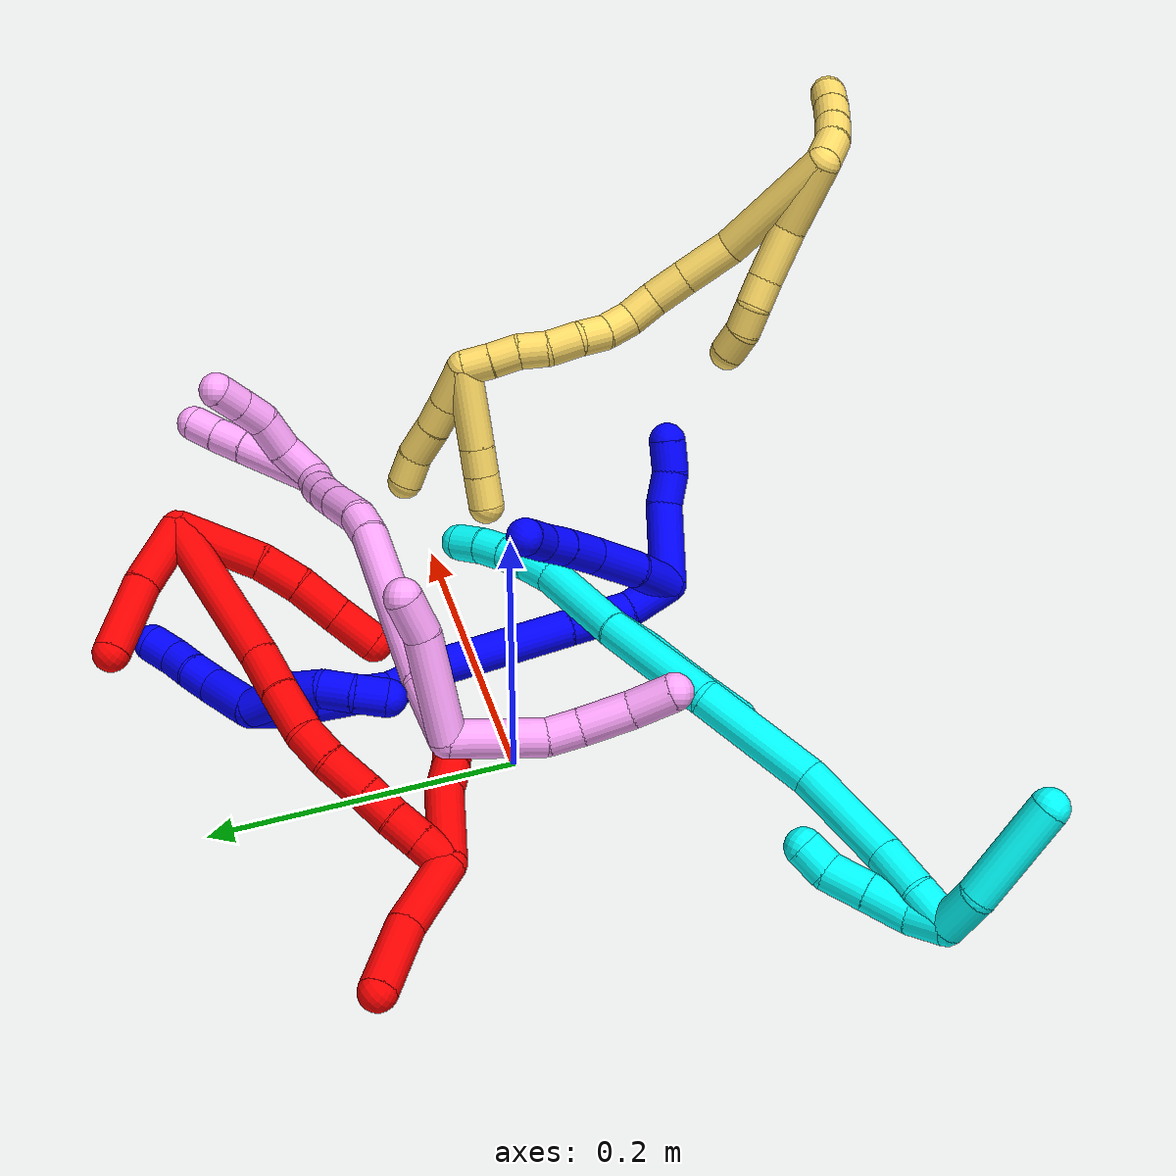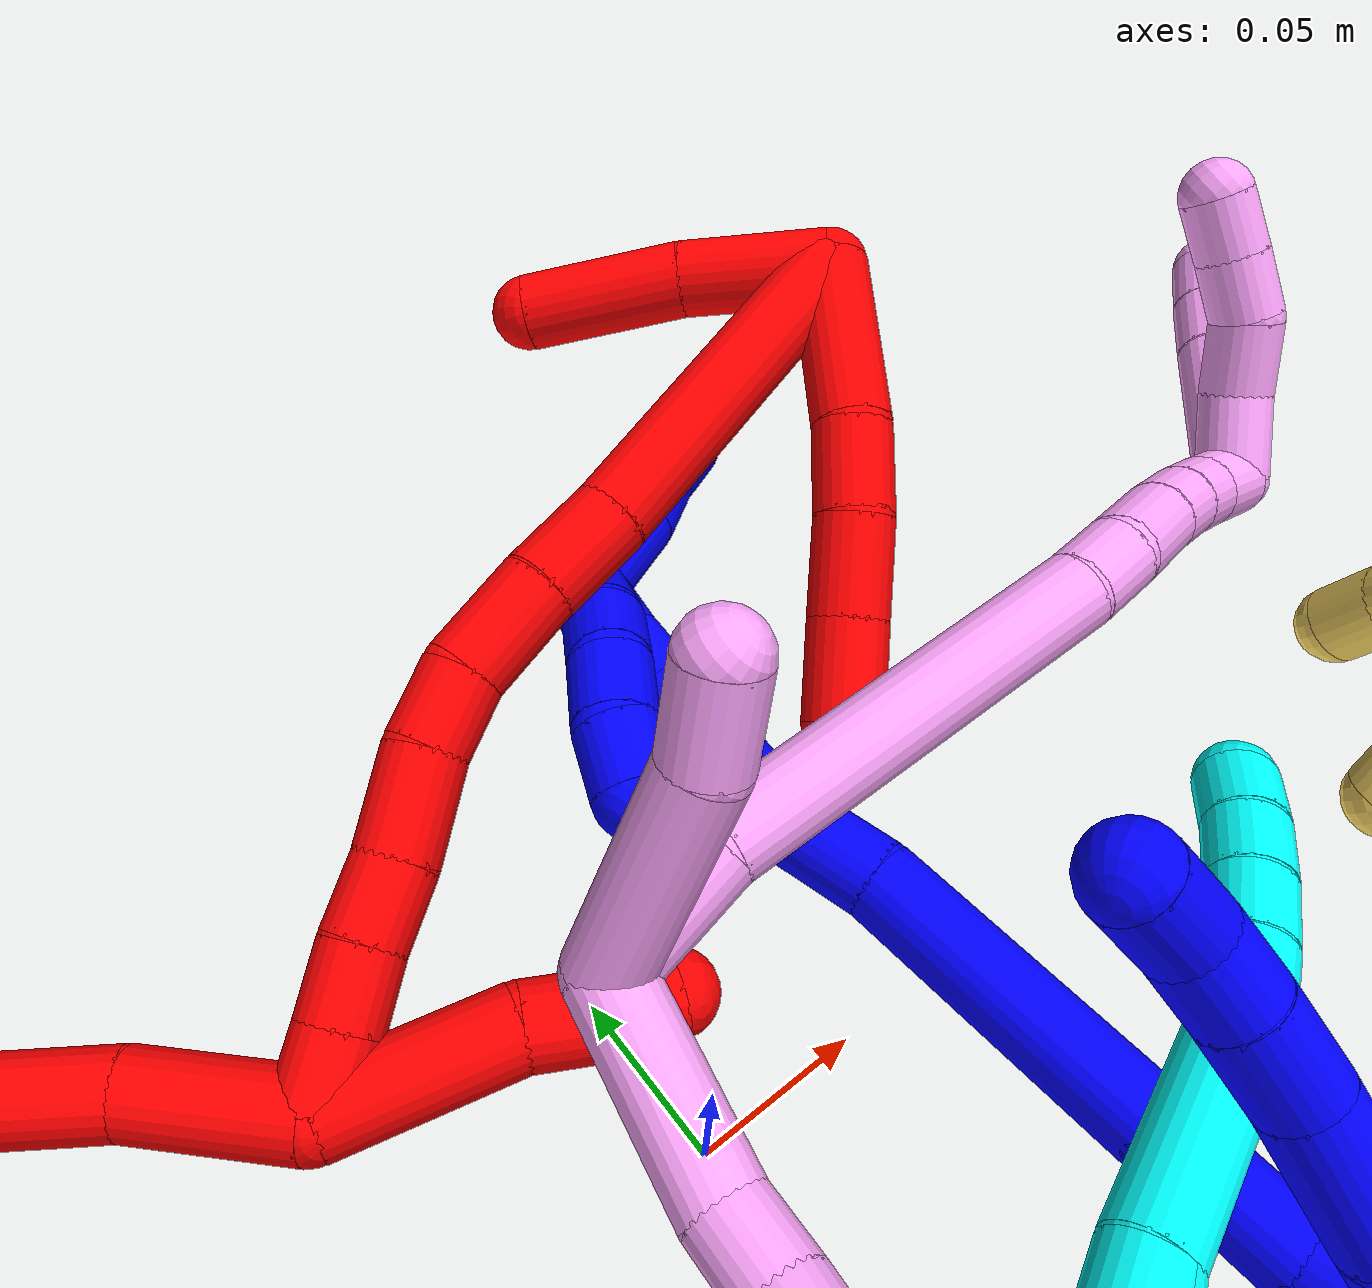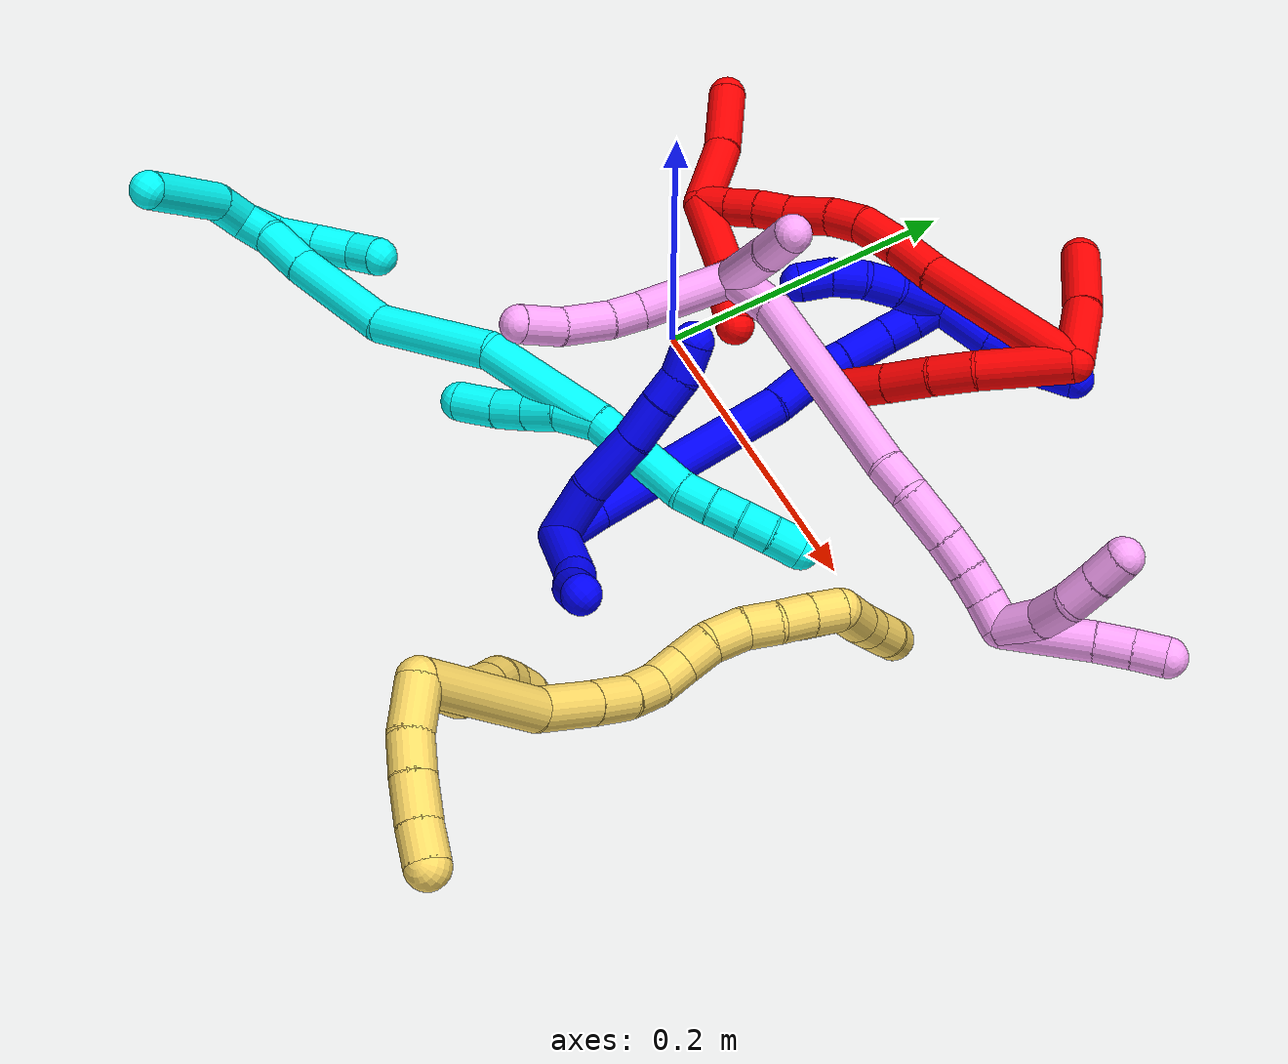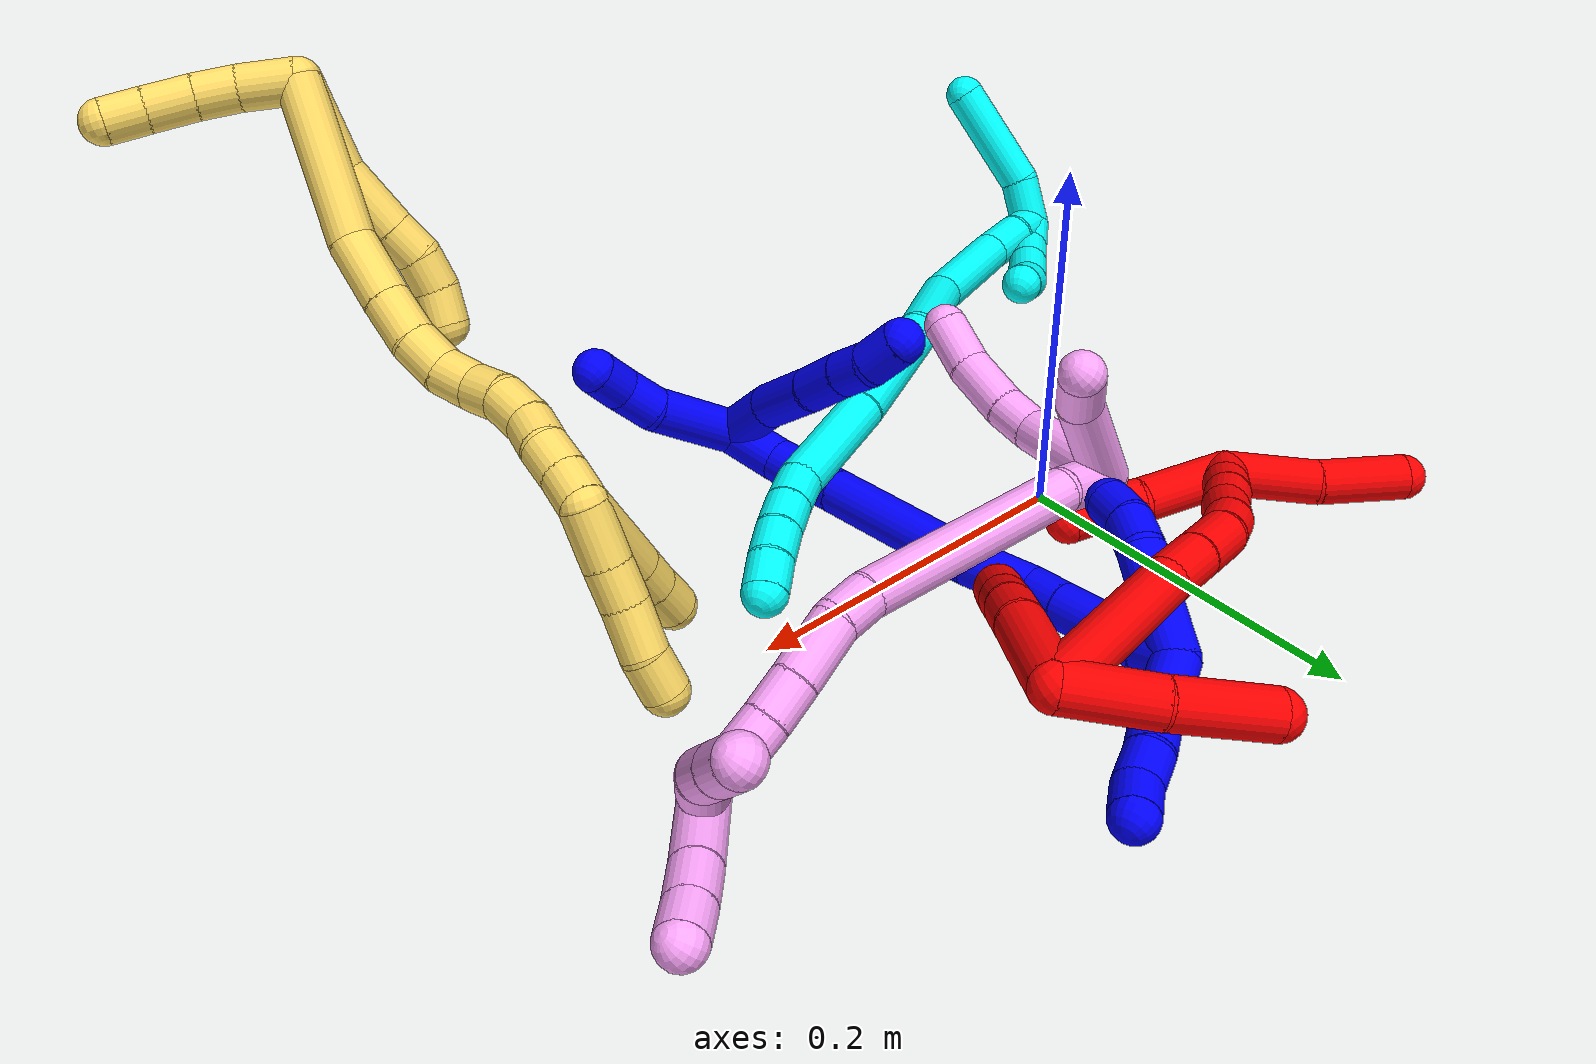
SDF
<sdf version="1.7">
 <world name="default">
  <plugin name="TubeGeneratorPlugin" filename="libtube_generator_plugin.so"/>
  <model name="photoneo_s_sensor">
   <static>1</static>
   <pose>0 0 2 1.57079 1.57079 3.14159</pose>
   <link name="link">
    <inertial><mass>0.1</mass></inertial>
    <sensor name="sensor" type="depth">
     <update_rate>30</update_rate>
     <camera>
      <horizontal_fov>1.22</horizontal_fov>
      <image><width>1920</width><height>1200</height><format>B8G8R8</format></image>
      <clip><near>0.1</near><far>4</far></clip>
      <depth_camera><output>points</output></depth_camera>
     </camera>
     <plugin name="camera_plugin" filename="libgazebo_ros_depth_camera.so">
      <baseline>0.2</baseline>
      <alwaysOn>1</alwaysOn>
      <updateRate>0.0</updateRate>
      <cameraName>camera_ir</cameraName>
      <imageTopicName>/camera/color/image_raw</imageTopicName>
      <cameraInfoTopicName>/camera/color/camera_info</cameraInfoTopicName>
      <depthImageTopicName>/camera/depth/image_raw</depthImageTopicName>
      <depthImageCameraInfoTopicName>/camera/depth/camera_info</depthImageCameraInfoTopicName>
      <pointCloudTopicName>/camera/depth/points</pointCloudTopicName>
      <frameName>fr_optical</frameName>
      <pointCloudCutoff>0.1</pointCloudCutoff>
      <pointCloudCutoffMax>2.0</pointCloudCutoffMax>
      <distortionK1>0</distortionK1>
      <distortionK2>0</distortionK2>
      <distortionK3>0</distortionK3>
      <distortionT1>0</distortionT1>
      <distortionT2>0</distortionT2>
      <CxPrime>0</CxPrime>
      <Cx>0</Cx>
      <Cy>0</Cy>
      <focalLength>0</focalLength>
      <hackBaseline>0</hackBaseline>
     </plugin>
    </sensor>
   </link>
  </model>
  <gravity>0 0 -9.8</gravity>
  <magnetic_field>6e-06 2.3e-05 -4.2e-05</magnetic_field>
  <atmosphere type="adiabatic"/>
  <physics name="default_physics" default="0" type="ode">
   <max_step_size>0.003</max_step_size>
   <real_time_factor>1</real_time_factor>
   <real_time_update_rate>1000</real_time_update_rate>
   <max_contacts>10000</max_contacts>
   <ode>
    <solver>
     <type>quick</type>
     <iters>100</iters>
     <sor>1.3</sor>
     <use_dynamic_moi_rescaling>0</use_dynamic_moi_rescaling>
    </solver>
    <constraints>
     <contact_max_correcting_vel>0</contact_max_correcting_vel>
     <contact_surface_layer>0.001</contact_surface_layer>
     <cfm>0</cfm>
     <erp>0.2</erp>
    </constraints>
   </ode>
  </physics>
  <scene><ambient>0.4 0.4 0.4 1</ambient><background>0.7 0.7 0.7 1</background><shadows>0</shadows></scene>
  <audio><device>default</device></audio>
  <spherical_coordinates>
   <surface_model>EARTH_WGS84</surface_model>
   <latitude_deg>0</latitude_deg>
   <longitude_deg>0</longitude_deg>
   <elevation>0</elevation>
   <heading_deg>0</heading_deg>
  </spherical_coordinates>
  <model name="bin">
   <static>1</static>
   <link name="bottom">
    <collision name="collision-bottom">
     <pose>0 0 -0.01 0 -0 0</pose>
     <geometry><box><size>0.8 0.6 0.02</size></box></geometry>
     <surface>
      <friction><ode><mu>100</mu><mu2>100</mu2></ode></friction>
      <contact><collide_bitmask>65535</collide_bitmask></contact>
     </surface>
    </collision>
   </link>
   <link name="west_wall">
    <collision name="collision-west_wall">
     <pose>-0.41 0 0.1 0 -0 0</pose>
     <geometry><box><size>0.02 0.6 0.2</size></box></geometry>
     <surface>
      <friction><ode><mu>100</mu><mu2>100</mu2></ode></friction>
      <contact><collide_bitmask>65535</collide_bitmask></contact>
     </surface>
    </collision>
   </link>
   <link name="east_wall">
    <collision name="collision-east_wall">
     <pose>0.41 0 0.1 0 -0 0</pose>
     <geometry><box><size>0.02 0.6 0.2</size></box></geometry>
     <surface>
      <friction><ode><mu>100</mu><mu2>100</mu2></ode></friction>
      <contact><collide_bitmask>65535</collide_bitmask></contact>
     </surface>
    </collision>
   </link>
   <link name="south_wall">
    <collision name="collision-south_wall">
     <pose>0 -0.31 0.1 0 -0 0</pose>
     <geometry><box><size>0.8 0.02 0.2</size></box></geometry>
     <surface>
      <friction><ode><mu>100</mu><mu2>100</mu2></ode></friction>
      <contact><collide_bitmask>65535</collide_bitmask></contact>
     </surface>
    </collision>
   </link>
   <link name="north_wall">
    <collision name="collision-north_wall">
     <pose>0 0.31 0.1 0 -0 0</pose>
     <geometry><box><size>0.8 0.02 0.2</size></box></geometry>
     <surface>
      <friction><ode><mu>100</mu><mu2>100</mu2></ode></friction>
      <contact><collide_bitmask>65535</collide_bitmask></contact>
     </surface>
    </collision>
   </link>
  </model>
  <model name="1">
   <static>0</static>
   <link name="1">
    <collision name="collision-cylinder-e_1_2_8">
     <pose>0.018784 0.001054 0.00335 -0.304815 1.38598 -0.25372</pose>
     <geometry><cylinder><radius>0.0125</radius><length>0.038219</length></cylinder></geometry>
     <surface>
      <friction><ode><mu>1.16</mu><mu2>1.16</mu2><slip1>0</slip1><slip2>0</slip2></ode></friction>
      <contact><ode><kp>1e+06</kp><kd>1</kd><max_vel>0</max_vel><min_depth>0.001</min_depth></ode></contact>
     </surface>
    </collision>
    <visual name="visual-cylinder-e_1_2_8">
     <pose>0.018784 0.001054 0.00335 -0.304815 1.38598 -0.25372</pose>
     <geometry><cylinder><radius>0.0125</radius><length>0.038219</length></cylinder></geometry>
     <material><ambient>0 0 1 1</ambient></material>
    </visual>
    <collision name="collision-cylinder-e_2_8_9">
     <pose>0.057697 0.005183 0.00721 -1.40625 1.41713 -1.25654</pose>
     <geometry><cylinder><radius>0.0125</radius><length>0.040739</length></cylinder></geometry>
     <surface>
      <friction><ode><mu>1.16</mu><mu2>1.16</mu2><slip1>0</slip1><slip2>0</slip2></ode></friction>
      <contact><ode><kp>1e+06</kp><kd>1</kd><max_vel>0</max_vel><min_depth>0.001</min_depth></ode></contact>
     </surface>
    </collision>
    <visual name="visual-cylinder-e_2_8_9">
     <pose>0.057697 0.005183 0.00721 -1.40625 1.41713 -1.25654</pose>
     <geometry><cylinder><radius>0.0125</radius><length>0.040739</length></cylinder></geometry>
     <material><ambient>0 0 1 1</ambient></material>
    </visual>
    <collision name="collision-cylinder-e_3_9_10">
     <pose>0.091299 0.010398 0.009544 -0.864763 1.36512 -0.717823</pose>
     <geometry><cylinder><radius>0.0125</radius><length>0.027525</length></cylinder></geometry>
     <surface>
      <friction><ode><mu>1.16</mu><mu2>1.16</mu2><slip1>0</slip1><slip2>0</slip2></ode></friction>
      <contact><ode><kp>1e+06</kp><kd>1</kd><max_vel>0</max_vel><min_depth>0.001</min_depth></ode></contact>
     </surface>
    </collision>
    <visual name="visual-cylinder-e_3_9_10">
     <pose>0.091299 0.010398 0.009544 -0.864763 1.36512 -0.717823</pose>
     <geometry><cylinder><radius>0.0125</radius><length>0.027525</length></cylinder></geometry>
     <material><ambient>0 0 1 1</ambient></material>
    </visual>
    <collision name="collision-cylinder-e_4_10_11">
     <pose>0.114665 0.014747 0.012607 -1.06004 1.32007 -0.853655</pose>
     <geometry><cylinder><radius>0.0125</radius><length>0.020427</length></cylinder></geometry>
     <surface>
      <friction><ode><mu>1.16</mu><mu2>1.16</mu2><slip1>0</slip1><slip2>0</slip2></ode></friction>
      <contact><ode><kp>1e+06</kp><kd>1</kd><max_vel>0</max_vel><min_depth>0.001</min_depth></ode></contact>
     </surface>
    </collision>
    <visual name="visual-cylinder-e_4_10_11">
     <pose>0.114665 0.014747 0.012607 -1.06004 1.32007 -0.853655</pose>
     <geometry><cylinder><radius>0.0125</radius><length>0.020427</length></cylinder></geometry>
     <material><ambient>0 0 1 1</ambient></material>
    </visual>
    <collision name="collision-cylinder-e_5_11_6">
     <pose>0.135173 0.018018 0.018263 -0.235523 1.16636 -0.155787</pose>
     <geometry><cylinder><radius>0.0125</radius><length>0.023091</length></cylinder></geometry>
     <surface>
      <friction><ode><mu>1.16</mu><mu2>1.16</mu2><slip1>0</slip1><slip2>0</slip2></ode></friction>
      <contact><ode><kp>1e+06</kp><kd>1</kd><max_vel>0</max_vel><min_depth>0.001</min_depth></ode></contact>
     </surface>
    </collision>
    <visual name="visual-cylinder-e_5_11_6">
     <pose>0.135173 0.018018 0.018263 -0.235523 1.16636 -0.155787</pose>
     <geometry><cylinder><radius>0.0125</radius><length>0.023091</length></cylinder></geometry>
     <material><ambient>0 0 1 1</ambient></material>
    </visual>
    <collision name="collision-cylinder-e_1_2_12">
     <pose>0.006852 -0.022259 -0.015018 2.16435 0.249844 0.463924</pose>
     <geometry><cylinder><radius>0.0125</radius><length>0.055424</length></cylinder></geometry>
     <surface>
      <friction><ode><mu>1.16</mu><mu2>1.16</mu2><slip1>0</slip1><slip2>0</slip2></ode></friction>
      <contact><ode><kp>1e+06</kp><kd>1</kd><max_vel>0</max_vel><min_depth>0.001</min_depth></ode></contact>
     </surface>
    </collision>
    <visual name="visual-cylinder-e_1_2_12">
     <pose>0.006852 -0.022259 -0.015018 2.16435 0.249844 0.463924</pose>
     <geometry><cylinder><radius>0.0125</radius><length>0.055424</length></cylinder></geometry>
     <material><ambient>0 0 1 1</ambient></material>
    </visual>
    <collision name="collision-cylinder-e_2_12_13">
     <pose>0.016017 -0.055205 -0.033367 1.87289 0.203779 0.276143</pose>
     <geometry><cylinder><radius>0.0125</radius><length>0.02286</length></cylinder></geometry>
     <surface>
      <friction><ode><mu>1.16</mu><mu2>1.16</mu2><slip1>0</slip1><slip2>0</slip2></ode></friction>
      <contact><ode><kp>1e+06</kp><kd>1</kd><max_vel>0</max_vel><min_depth>0.001</min_depth></ode></contact>
     </surface>
    </collision>
    <visual name="visual-cylinder-e_2_12_13">
     <pose>0.016017 -0.055205 -0.033367 1.87289 0.203779 0.276143</pose>
     <geometry><cylinder><radius>0.0125</radius><length>0.02286</length></cylinder></geometry>
     <material><ambient>0 0 1 1</ambient></material>
    </visual>
    <collision name="collision-cylinder-e_3_13_5">
     <pose>0.023439 -0.074594 -0.040705 2.0023 0.489843 0.744135</pose>
     <geometry><cylinder><radius>0.0125</radius><length>0.021715</length></cylinder></geometry>
     <surface>
      <friction><ode><mu>1.16</mu><mu2>1.16</mu2><slip1>0</slip1><slip2>0</slip2></ode></friction>
      <contact><ode><kp>1e+06</kp><kd>1</kd><max_vel>0</max_vel><min_depth>0.001</min_depth></ode></contact>
     </surface>
    </collision>
    <visual name="visual-cylinder-e_3_13_5">
     <pose>0.023439 -0.074594 -0.040705 2.0023 0.489843 0.744135</pose>
     <geometry><cylinder><radius>0.0125</radius><length>0.021715</length></cylinder></geometry>
     <material><ambient>0 0 1 1</ambient></material>
    </visual>
    <collision name="collision-cylinder-e_1_2_14">
     <pose>0.007965 0.014152 -0.001507 -1.67685 0.510206 -0.564553</pose>
     <geometry><cylinder><radius>0.0125</radius><length>0.032618</length></cylinder></geometry>
     <surface>
      <friction><ode><mu>1.16</mu><mu2>1.16</mu2><slip1>0</slip1><slip2>0</slip2></ode></friction>
      <contact><ode><kp>1e+06</kp><kd>1</kd><max_vel>0</max_vel><min_depth>0.001</min_depth></ode></contact>
     </surface>
    </collision>
    <visual name="visual-cylinder-e_1_2_14">
     <pose>0.007965 0.014152 -0.001507 -1.67685 0.510206 -0.564553</pose>
     <geometry><cylinder><radius>0.0125</radius><length>0.032618</length></cylinder></geometry>
     <material><ambient>0 0 1 1</ambient></material>
    </visual>
    <collision name="collision-cylinder-e_2_14_15">
     <pose>0.031357 0.043805 -0.006956 -1.81985 0.76737 -0.957804</pose>
     <geometry><cylinder><radius>0.0125</radius><length>0.044445</length></cylinder></geometry>
     <surface>
      <friction><ode><mu>1.16</mu><mu2>1.16</mu2><slip1>0</slip1><slip2>0</slip2></ode></friction>
      <contact><ode><kp>1e+06</kp><kd>1</kd><max_vel>0</max_vel><min_depth>0.001</min_depth></ode></contact>
     </surface>
    </collision>
    <visual name="visual-cylinder-e_2_14_15">
     <pose>0.031357 0.043805 -0.006956 -1.81985 0.76737 -0.957804</pose>
     <geometry><cylinder><radius>0.0125</radius><length>0.044445</length></cylinder></geometry>
     <material><ambient>0 0 1 1</ambient></material>
    </visual>
    <collision name="collision-cylinder-e_3_15_16">
     <pose>0.07883 0.091543 -0.019095 -1.81978 0.766755 -0.957024</pose>
     <geometry><cylinder><radius>0.0125</radius><length>0.092376</length></cylinder></geometry>
     <surface>
      <friction><ode><mu>1.16</mu><mu2>1.16</mu2><slip1>0</slip1><slip2>0</slip2></ode></friction>
      <contact><ode><kp>1e+06</kp><kd>1</kd><max_vel>0</max_vel><min_depth>0.001</min_depth></ode></contact>
     </surface>
    </collision>
    <visual name="visual-cylinder-e_3_15_16">
     <pose>0.07883 0.091543 -0.019095 -1.81978 0.766755 -0.957024</pose>
     <geometry><cylinder><radius>0.0125</radius><length>0.092376</length></cylinder></geometry>
     <material><ambient>0 0 1 1</ambient></material>
    </visual>
    <collision name="collision-cylinder-e_4_16_17">
     <pose>0.122965 0.138146 -0.02806 -1.62421 0.698877 -0.733966</pose>
     <geometry><cylinder><radius>0.0125</radius><length>0.037583</length></cylinder></geometry>
     <surface>
      <friction><ode><mu>1.16</mu><mu2>1.16</mu2><slip1>0</slip1><slip2>0</slip2></ode></friction>
      <contact><ode><kp>1e+06</kp><kd>1</kd><max_vel>0</max_vel><min_depth>0.001</min_depth></ode></contact>
     </surface>
    </collision>
    <visual name="visual-cylinder-e_4_16_17">
     <pose>0.122965 0.138146 -0.02806 -1.62421 0.698877 -0.733966</pose>
     <geometry><cylinder><radius>0.0125</radius><length>0.037583</length></cylinder></geometry>
     <material><ambient>0 0 1 1</ambient></material>
    </visual>
    <collision name="collision-cylinder-e_5_17_18">
     <pose>0.142987 0.158597 -0.03139 -1.96938 0.876648 -1.22948</pose>
     <geometry><cylinder><radius>0.0125</radius><length>0.020641</length></cylinder></geometry>
     <surface>
      <friction><ode><mu>1.16</mu><mu2>1.16</mu2><slip1>0</slip1><slip2>0</slip2></ode></friction>
      <contact><ode><kp>1e+06</kp><kd>1</kd><max_vel>0</max_vel><min_depth>0.001</min_depth></ode></contact>
     </surface>
    </collision>
    <visual name="visual-cylinder-e_5_17_18">
     <pose>0.142987 0.158597 -0.03139 -1.96938 0.876648 -1.22948</pose>
     <geometry><cylinder><radius>0.0125</radius><length>0.020641</length></cylinder></geometry>
     <material><ambient>0 0 1 1</ambient></material>
    </visual>
    <collision name="collision-cylinder-e_6_18_19">
     <pose>0.162627 0.174307 -0.03724 -1.8999 0.855459 -1.13497</pose>
     <geometry><cylinder><radius>0.0125</radius><length>0.031017</length></cylinder></geometry>
     <surface>
      <friction><ode><mu>1.16</mu><mu2>1.16</mu2><slip1>0</slip1><slip2>0</slip2></ode></friction>
      <contact><ode><kp>1e+06</kp><kd>1</kd><max_vel>0</max_vel><min_depth>0.001</min_depth></ode></contact>
     </surface>
    </collision>
    <visual name="visual-cylinder-e_6_18_19">
     <pose>0.162627 0.174307 -0.03724 -1.8999 0.855459 -1.13497</pose>
     <geometry><cylinder><radius>0.0125</radius><length>0.031017</length></cylinder></geometry>
     <material><ambient>0 0 1 1</ambient></material>
    </visual>
    <collision name="collision-cylinder-e_7_19_20">
     <pose>0.182097 0.189895 -0.042923 -1.95278 0.879361 -1.21592</pose>
     <geometry><cylinder><radius>0.0125</radius><length>0.020154</length></cylinder></geometry>
     <surface>
      <friction><ode><mu>1.16</mu><mu2>1.16</mu2><slip1>0</slip1><slip2>0</slip2></ode></friction>
      <contact><ode><kp>1e+06</kp><kd>1</kd><max_vel>0</max_vel><min_depth>0.001</min_depth></ode></contact>
     </surface>
    </collision>
    <visual name="visual-cylinder-e_7_19_20">
     <pose>0.182097 0.189895 -0.042923 -1.95278 0.879361 -1.21592</pose>
     <geometry><cylinder><radius>0.0125</radius><length>0.020154</length></cylinder></geometry>
     <material><ambient>0 0 1 1</ambient></material>
    </visual>
    <collision name="collision-cylinder-e_8_20_1">
     <pose>0.198997 0.200722 -0.047516 -1.99517 1.04212 -1.4536</pose>
     <geometry><cylinder><radius>0.0125</radius><length>0.021165</length></cylinder></geometry>
     <surface>
      <friction><ode><mu>1.16</mu><mu2>1.16</mu2><slip1>0</slip1><slip2>0</slip2></ode></friction>
      <contact><ode><kp>1e+06</kp><kd>1</kd><max_vel>0</max_vel><min_depth>0.001</min_depth></ode></contact>
     </surface>
    </collision>
    <visual name="visual-cylinder-e_8_20_1">
     <pose>0.198997 0.200722 -0.047516 -1.99517 1.04212 -1.4536</pose>
     <geometry><cylinder><radius>0.0125</radius><length>0.021165</length></cylinder></geometry>
     <material><ambient>0 0 1 1</ambient></material>
    </visual>
    <collision name="collision-cylinder-e_1_1_21">
     <pose>0.20611 0.192626 -0.037651 0.821254 -0.113882 -0.049625</pose>
     <geometry><cylinder><radius>0.0125</radius><length>0.035643</length></cylinder></geometry>
     <surface>
      <friction><ode><mu>1.16</mu><mu2>1.16</mu2><slip1>0</slip1><slip2>0</slip2></ode></friction>
      <contact><ode><kp>1e+06</kp><kd>1</kd><max_vel>0</max_vel><min_depth>0.001</min_depth></ode></contact>
     </surface>
    </collision>
    <visual name="visual-cylinder-e_1_1_21">
     <pose>0.20611 0.192626 -0.037651 0.821254 -0.113882 -0.049625</pose>
     <geometry><cylinder><radius>0.0125</radius><length>0.035643</length></cylinder></geometry>
     <material><ambient>0 0 1 1</ambient></material>
    </visual>
    <collision name="collision-cylinder-e_2_21_22">
     <pose>0.200821 0.173399 -0.017133 0.637844 -0.30071 -0.099964</pose>
     <geometry><cylinder><radius>0.0125</radius><length>0.022035</length></cylinder></geometry>
     <surface>
      <friction><ode><mu>1.16</mu><mu2>1.16</mu2><slip1>0</slip1><slip2>0</slip2></ode></friction>
      <contact><ode><kp>1e+06</kp><kd>1</kd><max_vel>0</max_vel><min_depth>0.001</min_depth></ode></contact>
     </surface>
    </collision>
    <visual name="visual-cylinder-e_2_21_22">
     <pose>0.200821 0.173399 -0.017133 0.637844 -0.30071 -0.099964</pose>
     <geometry><cylinder><radius>0.0125</radius><length>0.022035</length></cylinder></geometry>
     <material><ambient>0 0 1 1</ambient></material>
    </visual>
    <collision name="collision-cylinder-e_3_22_23">
     <pose>0.191712 0.162877 -0.000663 0.488014 -0.572238 -0.146227</pose>
     <geometry><cylinder><radius>0.0125</radius><length>0.02159</length></cylinder></geometry>
     <surface>
      <friction><ode><mu>1.16</mu><mu2>1.16</mu2><slip1>0</slip1><slip2>0</slip2></ode></friction>
      <contact><ode><kp>1e+06</kp><kd>1</kd><max_vel>0</max_vel><min_depth>0.001</min_depth></ode></contact>
     </surface>
    </collision>
    <visual name="visual-cylinder-e_3_22_23">
     <pose>0.191712 0.162877 -0.000663 0.488014 -0.572238 -0.146227</pose>
     <geometry><cylinder><radius>0.0125</radius><length>0.02159</length></cylinder></geometry>
     <material><ambient>0 0 1 1</ambient></material>
    </visual>
    <collision name="collision-cylinder-e_4_23_4">
     <pose>0.178269 0.15448 0.01306 0.627764 -0.822638 -0.281322</pose>
     <geometry><cylinder><radius>0.0125</radius><length>0.020732</length></cylinder></geometry>
     <surface>
      <friction><ode><mu>1.16</mu><mu2>1.16</mu2><slip1>0</slip1><slip2>0</slip2></ode></friction>
      <contact><ode><kp>1e+06</kp><kd>1</kd><max_vel>0</max_vel><min_depth>0.001</min_depth></ode></contact>
     </surface>
    </collision>
    <visual name="visual-cylinder-e_4_23_4">
     <pose>0.178269 0.15448 0.01306 0.627764 -0.822638 -0.281322</pose>
     <geometry><cylinder><radius>0.0125</radius><length>0.020732</length></cylinder></geometry>
     <material><ambient>0 0 1 1</ambient></material>
    </visual>
    <collision name="collision-cylinder-e_1_1_24">
     <pose>0.211345 0.207137 -0.068674 -3.06002 0.16717 -2.23505</pose>
     <geometry><cylinder><radius>0.0125</radius><length>0.038586</length></cylinder></geometry>
     <surface>
      <friction><ode><mu>1.16</mu><mu2>1.16</mu2><slip1>0</slip1><slip2>0</slip2></ode></friction>
      <contact><ode><kp>1e+06</kp><kd>1</kd><max_vel>0</max_vel><min_depth>0.001</min_depth></ode></contact>
     </surface>
    </collision>
    <visual name="visual-cylinder-e_1_1_24">
     <pose>0.211345 0.207137 -0.068674 -3.06002 0.16717 -2.23505</pose>
     <geometry><cylinder><radius>0.0125</radius><length>0.038586</length></cylinder></geometry>
     <material><ambient>0 0 1 1</ambient></material>
    </visual>
    <collision name="collision-cylinder-e_2_24_25">
     <pose>0.218575 0.208907 -0.097241 -3.11868 0.396196 -3.02758</pose>
     <geometry><cylinder><radius>0.0125</radius><length>0.020831</length></cylinder></geometry>
     <surface>
      <friction><ode><mu>1.16</mu><mu2>1.16</mu2><slip1>0</slip1><slip2>0</slip2></ode></friction>
      <contact><ode><kp>1e+06</kp><kd>1</kd><max_vel>0</max_vel><min_depth>0.001</min_depth></ode></contact>
     </surface>
    </collision>
    <visual name="visual-cylinder-e_2_24_25">
     <pose>0.218575 0.208907 -0.097241 -3.11868 0.396196 -3.02758</pose>
     <geometry><cylinder><radius>0.0125</radius><length>0.020831</length></cylinder></geometry>
     <material><ambient>0 0 1 1</ambient></material>
    </visual>
    <collision name="collision-cylinder-e_3_25_26">
     <pose>0.224679 0.209257 -0.116786 -3.1285 0.206753 -3.01555</pose>
     <geometry><cylinder><radius>0.0125</radius><length>0.020312</length></cylinder></geometry>
     <surface>
      <friction><ode><mu>1.16</mu><mu2>1.16</mu2><slip1>0</slip1><slip2>0</slip2></ode></friction>
      <contact><ode><kp>1e+06</kp><kd>1</kd><max_vel>0</max_vel><min_depth>0.001</min_depth></ode></contact>
     </surface>
    </collision>
    <visual name="visual-cylinder-e_3_25_26">
     <pose>0.224679 0.209257 -0.116786 -3.1285 0.206753 -3.01555</pose>
     <geometry><cylinder><radius>0.0125</radius><length>0.020312</length></cylinder></geometry>
     <material><ambient>0 0 1 1</ambient></material>
    </visual>
    <collision name="collision-cylinder-e_4_26_3">
     <pose>0.231597 0.209773 -0.135626 -3.09824 0.497074 -2.97116</pose>
     <geometry><cylinder><radius>0.0125</radius><length>0.020272</length></cylinder></geometry>
     <surface>
      <friction><ode><mu>1.16</mu><mu2>1.16</mu2><slip1>0</slip1><slip2>0</slip2></ode></friction>
      <contact><ode><kp>1e+06</kp><kd>1</kd><max_vel>0</max_vel><min_depth>0.001</min_depth></ode></contact>
     </surface>
    </collision>
    <visual name="visual-cylinder-e_4_26_3">
     <pose>0.231597 0.209773 -0.135626 -3.09824 0.497074 -2.97116</pose>
     <geometry><cylinder><radius>0.0125</radius><length>0.020272</length></cylinder></geometry>
     <material><ambient>0 0 1 1</ambient></material>
    </visual>
    <collision name="collision-sphere-3">
     <pose>0.23643 0.210159 -0.144526 0 -0 0</pose>
     <geometry><sphere><radius>0.0125</radius></sphere></geometry>
     <surface>
      <friction><ode><mu>1.16</mu><mu2>1.16</mu2><slip1>0</slip1><slip2>0</slip2></ode></friction>
      <contact><ode><kp>1e+06</kp><kd>1</kd><max_vel>0</max_vel><min_depth>0.001</min_depth></ode></contact>
     </surface>
    </collision>
    <visual name="visual-sphere-3">
     <pose>0.23643 0.210159 -0.144526 0 -0 0</pose>
     <geometry><sphere><radius>0.0125</radius></sphere></geometry>
     <material><ambient>0 0 1 1</ambient></material>
    </visual>
    <collision name="collision-sphere-26">
     <pose>0.226764 0.209387 -0.126725 0 -0 0</pose>
     <geometry><sphere><radius>0.0125</radius></sphere></geometry>
     <surface>
      <friction><ode><mu>1.16</mu><mu2>1.16</mu2><slip1>0</slip1><slip2>0</slip2></ode></friction>
      <contact><ode><kp>1e+06</kp><kd>1</kd><max_vel>0</max_vel><min_depth>0.001</min_depth></ode></contact>
     </surface>
    </collision>
    <visual name="visual-sphere-26">
     <pose>0.226764 0.209387 -0.126725 0 -0 0</pose>
     <geometry><sphere><radius>0.0125</radius></sphere></geometry>
     <material><ambient>0 0 1 1</ambient></material>
    </visual>
    <collision name="collision-sphere-25">
     <pose>0.222594 0.209127 -0.106848 0 -0 0</pose>
     <geometry><sphere><radius>0.0125</radius></sphere></geometry>
     <surface>
      <friction><ode><mu>1.16</mu><mu2>1.16</mu2><slip1>0</slip1><slip2>0</slip2></ode></friction>
      <contact><ode><kp>1e+06</kp><kd>1</kd><max_vel>0</max_vel><min_depth>0.001</min_depth></ode></contact>
     </surface>
    </collision>
    <visual name="visual-sphere-25">
     <pose>0.222594 0.209127 -0.106848 0 -0 0</pose>
     <geometry><sphere><radius>0.0125</radius></sphere></geometry>
     <material><ambient>0 0 1 1</ambient></material>
    </visual>
    <collision name="collision-sphere-24">
     <pose>0.214555 0.208687 -0.087635 0 -0 0</pose>
     <geometry><sphere><radius>0.0125</radius></sphere></geometry>
     <surface>
      <friction><ode><mu>1.16</mu><mu2>1.16</mu2><slip1>0</slip1><slip2>0</slip2></ode></friction>
      <contact><ode><kp>1e+06</kp><kd>1</kd><max_vel>0</max_vel><min_depth>0.001</min_depth></ode></contact>
     </surface>
    </collision>
    <visual name="visual-sphere-24">
     <pose>0.214555 0.208687 -0.087635 0 -0 0</pose>
     <geometry><sphere><radius>0.0125</radius></sphere></geometry>
     <material><ambient>0 0 1 1</ambient></material>
    </visual>
    <collision name="collision-sphere-4">
     <pose>0.170671 0.150339 0.018767 0 -0 0</pose>
     <geometry><sphere><radius>0.0125</radius></sphere></geometry>
     <surface>
      <friction><ode><mu>1.16</mu><mu2>1.16</mu2><slip1>0</slip1><slip2>0</slip2></ode></friction>
      <contact><ode><kp>1e+06</kp><kd>1</kd><max_vel>0</max_vel><min_depth>0.001</min_depth></ode></contact>
     </surface>
    </collision>
    <visual name="visual-sphere-4">
     <pose>0.170671 0.150339 0.018767 0 -0 0</pose>
     <geometry><sphere><radius>0.0125</radius></sphere></geometry>
     <material><ambient>0 0 1 1</ambient></material>
    </visual>
    <collision name="collision-sphere-23">
     <pose>0.185866 0.158622 0.007353 0 -0 0</pose>
     <geometry><sphere><radius>0.0125</radius></sphere></geometry>
     <surface>
      <friction><ode><mu>1.16</mu><mu2>1.16</mu2><slip1>0</slip1><slip2>0</slip2></ode></friction>
      <contact><ode><kp>1e+06</kp><kd>1</kd><max_vel>0</max_vel><min_depth>0.001</min_depth></ode></contact>
     </surface>
    </collision>
    <visual name="visual-sphere-23">
     <pose>0.185866 0.158622 0.007353 0 -0 0</pose>
     <geometry><sphere><radius>0.0125</radius></sphere></geometry>
     <material><ambient>0 0 1 1</ambient></material>
    </visual>
    <collision name="collision-sphere-22">
     <pose>0.197558 0.167133 -0.008679 0 -0 0</pose>
     <geometry><sphere><radius>0.0125</radius></sphere></geometry>
     <surface>
      <friction><ode><mu>1.16</mu><mu2>1.16</mu2><slip1>0</slip1><slip2>0</slip2></ode></friction>
      <contact><ode><kp>1e+06</kp><kd>1</kd><max_vel>0</max_vel><min_depth>0.001</min_depth></ode></contact>
     </surface>
    </collision>
    <visual name="visual-sphere-22">
     <pose>0.197558 0.167133 -0.008679 0 -0 0</pose>
     <geometry><sphere><radius>0.0125</radius></sphere></geometry>
     <material><ambient>0 0 1 1</ambient></material>
    </visual>
    <collision name="collision-sphere-21">
     <pose>0.204085 0.179665 -0.025587 0 -0 0</pose>
     <geometry><sphere><radius>0.0125</radius></sphere></geometry>
     <surface>
      <friction><ode><mu>1.16</mu><mu2>1.16</mu2><slip1>0</slip1><slip2>0</slip2></ode></friction>
      <contact><ode><kp>1e+06</kp><kd>1</kd><max_vel>0</max_vel><min_depth>0.001</min_depth></ode></contact>
     </surface>
    </collision>
    <visual name="visual-sphere-21">
     <pose>0.204085 0.179665 -0.025587 0 -0 0</pose>
     <geometry><sphere><radius>0.0125</radius></sphere></geometry>
     <material><ambient>0 0 1 1</ambient></material>
    </visual>
    <collision name="collision-sphere-1">
     <pose>0.208135 0.205587 -0.049714 0 -0 0</pose>
     <geometry><sphere><radius>0.0125</radius></sphere></geometry>
     <surface>
      <friction><ode><mu>1.16</mu><mu2>1.16</mu2><slip1>0</slip1><slip2>0</slip2></ode></friction>
      <contact><ode><kp>1e+06</kp><kd>1</kd><max_vel>0</max_vel><min_depth>0.001</min_depth></ode></contact>
     </surface>
    </collision>
    <visual name="visual-sphere-1">
     <pose>0.208135 0.205587 -0.049714 0 -0 0</pose>
     <geometry><sphere><radius>0.0125</radius></sphere></geometry>
     <material><ambient>0 0 1 1</ambient></material>
    </visual>
    <collision name="collision-sphere-6">
     <pose>0.145787 0.019078 0.022681 0 -0 0</pose>
     <geometry><sphere><radius>0.0125</radius></sphere></geometry>
     <surface>
      <friction><ode><mu>1.16</mu><mu2>1.16</mu2><slip1>0</slip1><slip2>0</slip2></ode></friction>
      <contact><ode><kp>1e+06</kp><kd>1</kd><max_vel>0</max_vel><min_depth>0.001</min_depth></ode></contact>
     </surface>
    </collision>
    <visual name="visual-sphere-6">
     <pose>0.145787 0.019078 0.022681 0 -0 0</pose>
     <geometry><sphere><radius>0.0125</radius></sphere></geometry>
     <material><ambient>0 0 1 1</ambient></material>
    </visual>
    <collision name="collision-sphere-11">
     <pose>0.124559 0.016958 0.013845 0 -0 0</pose>
     <geometry><sphere><radius>0.0125</radius></sphere></geometry>
     <surface>
      <friction><ode><mu>1.16</mu><mu2>1.16</mu2><slip1>0</slip1><slip2>0</slip2></ode></friction>
      <contact><ode><kp>1e+06</kp><kd>1</kd><max_vel>0</max_vel><min_depth>0.001</min_depth></ode></contact>
     </surface>
    </collision>
    <visual name="visual-sphere-11">
     <pose>0.124559 0.016958 0.013845 0 -0 0</pose>
     <geometry><sphere><radius>0.0125</radius></sphere></geometry>
     <material><ambient>0 0 1 1</ambient></material>
    </visual>
    <collision name="collision-sphere-10">
     <pose>0.104771 0.012536 0.011368 0 -0 0</pose>
     <geometry><sphere><radius>0.0125</radius></sphere></geometry>
     <surface>
      <friction><ode><mu>1.16</mu><mu2>1.16</mu2><slip1>0</slip1><slip2>0</slip2></ode></friction>
      <contact><ode><kp>1e+06</kp><kd>1</kd><max_vel>0</max_vel><min_depth>0.001</min_depth></ode></contact>
     </surface>
    </collision>
    <visual name="visual-sphere-10">
     <pose>0.104771 0.012536 0.011368 0 -0 0</pose>
     <geometry><sphere><radius>0.0125</radius></sphere></geometry>
     <material><ambient>0 0 1 1</ambient></material>
    </visual>
    <collision name="collision-sphere-9">
     <pose>0.077826 0.008259 0.007721 0 -0 0</pose>
     <geometry><sphere><radius>0.0125</radius></sphere></geometry>
     <surface>
      <friction><ode><mu>1.16</mu><mu2>1.16</mu2><slip1>0</slip1><slip2>0</slip2></ode></friction>
      <contact><ode><kp>1e+06</kp><kd>1</kd><max_vel>0</max_vel><min_depth>0.001</min_depth></ode></contact>
     </surface>
    </collision>
    <visual name="visual-sphere-9">
     <pose>0.077826 0.008259 0.007721 0 -0 0</pose>
     <geometry><sphere><radius>0.0125</radius></sphere></geometry>
     <material><ambient>0 0 1 1</ambient></material>
    </visual>
    <collision name="collision-sphere-2">
     <geometry><sphere><radius>0.0125</radius></sphere></geometry>
     <surface>
      <friction><ode><mu>1.16</mu><mu2>1.16</mu2><slip1>0</slip1><slip2>0</slip2></ode></friction>
      <contact><ode><kp>1e+06</kp><kd>1</kd><max_vel>0</max_vel><min_depth>0.001</min_depth></ode></contact>
     </surface>
    </collision>
    <visual name="visual-sphere-2">
     <geometry><sphere><radius>0.0125</radius></sphere></geometry>
     <material><ambient>0 0 1 1</ambient></material>
    </visual>
    <collision name="collision-sphere-19">
     <pose>0.174334 0.183933 -0.040528 0 -0 0</pose>
     <geometry><sphere><radius>0.0125</radius></sphere></geometry>
     <surface>
      <friction><ode><mu>1.16</mu><mu2>1.16</mu2><slip1>0</slip1><slip2>0</slip2></ode></friction>
      <contact><ode><kp>1e+06</kp><kd>1</kd><max_vel>0</max_vel><min_depth>0.001</min_depth></ode></contact>
     </surface>
    </collision>
    <visual name="visual-sphere-19">
     <pose>0.174334 0.183933 -0.040528 0 -0 0</pose>
     <geometry><sphere><radius>0.0125</radius></sphere></geometry>
     <material><ambient>0 0 1 1</ambient></material>
    </visual>
    <collision name="collision-sphere-8">
     <pose>0.037568 0.002108 0.006699 0 -0 0</pose>
     <geometry><sphere><radius>0.0125</radius></sphere></geometry>
     <surface>
      <friction><ode><mu>1.16</mu><mu2>1.16</mu2><slip1>0</slip1><slip2>0</slip2></ode></friction>
      <contact><ode><kp>1e+06</kp><kd>1</kd><max_vel>0</max_vel><min_depth>0.001</min_depth></ode></contact>
     </surface>
    </collision>
    <visual name="visual-sphere-8">
     <pose>0.037568 0.002108 0.006699 0 -0 0</pose>
     <geometry><sphere><radius>0.0125</radius></sphere></geometry>
     <material><ambient>0 0 1 1</ambient></material>
    </visual>
    <collision name="collision-sphere-12">
     <pose>0.013704 -0.044518 -0.030037 0 -0 0</pose>
     <geometry><sphere><radius>0.0125</radius></sphere></geometry>
     <surface>
      <friction><ode><mu>1.16</mu><mu2>1.16</mu2><slip1>0</slip1><slip2>0</slip2></ode></friction>
      <contact><ode><kp>1e+06</kp><kd>1</kd><max_vel>0</max_vel><min_depth>0.001</min_depth></ode></contact>
     </surface>
    </collision>
    <visual name="visual-sphere-12">
     <pose>0.013704 -0.044518 -0.030037 0 -0 0</pose>
     <geometry><sphere><radius>0.0125</radius></sphere></geometry>
     <material><ambient>0 0 1 1</ambient></material>
    </visual>
    <collision name="collision-sphere-13">
     <pose>0.01833 -0.065892 -0.036698 0 -0 0</pose>
     <geometry><sphere><radius>0.0125</radius></sphere></geometry>
     <surface>
      <friction><ode><mu>1.16</mu><mu2>1.16</mu2><slip1>0</slip1><slip2>0</slip2></ode></friction>
      <contact><ode><kp>1e+06</kp><kd>1</kd><max_vel>0</max_vel><min_depth>0.001</min_depth></ode></contact>
     </surface>
    </collision>
    <visual name="visual-sphere-13">
     <pose>0.01833 -0.065892 -0.036698 0 -0 0</pose>
     <geometry><sphere><radius>0.0125</radius></sphere></geometry>
     <material><ambient>0 0 1 1</ambient></material>
    </visual>
    <collision name="collision-sphere-5">
     <pose>0.028547 -0.083297 -0.044712 0 -0 0</pose>
     <geometry><sphere><radius>0.0125</radius></sphere></geometry>
     <surface>
      <friction><ode><mu>1.16</mu><mu2>1.16</mu2><slip1>0</slip1><slip2>0</slip2></ode></friction>
      <contact><ode><kp>1e+06</kp><kd>1</kd><max_vel>0</max_vel><min_depth>0.001</min_depth></ode></contact>
     </surface>
    </collision>
    <visual name="visual-sphere-5">
     <pose>0.028547 -0.083297 -0.044712 0 -0 0</pose>
     <geometry><sphere><radius>0.0125</radius></sphere></geometry>
     <material><ambient>0 0 1 1</ambient></material>
    </visual>
    <collision name="collision-sphere-14">
     <pose>0.015929 0.028304 -0.003013 0 -0 0</pose>
     <geometry><sphere><radius>0.0125</radius></sphere></geometry>
     <surface>
      <friction><ode><mu>1.16</mu><mu2>1.16</mu2><slip1>0</slip1><slip2>0</slip2></ode></friction>
      <contact><ode><kp>1e+06</kp><kd>1</kd><max_vel>0</max_vel><min_depth>0.001</min_depth></ode></contact>
     </surface>
    </collision>
    <visual name="visual-sphere-14">
     <pose>0.015929 0.028304 -0.003013 0 -0 0</pose>
     <geometry><sphere><radius>0.0125</radius></sphere></geometry>
     <material><ambient>0 0 1 1</ambient></material>
    </visual>
    <collision name="collision-sphere-15">
     <pose>0.046785 0.059306 -0.010898 0 -0 0</pose>
     <geometry><sphere><radius>0.0125</radius></sphere></geometry>
     <surface>
      <friction><ode><mu>1.16</mu><mu2>1.16</mu2><slip1>0</slip1><slip2>0</slip2></ode></friction>
      <contact><ode><kp>1e+06</kp><kd>1</kd><max_vel>0</max_vel><min_depth>0.001</min_depth></ode></contact>
     </surface>
    </collision>
    <visual name="visual-sphere-15">
     <pose>0.046785 0.059306 -0.010898 0 -0 0</pose>
     <geometry><sphere><radius>0.0125</radius></sphere></geometry>
     <material><ambient>0 0 1 1</ambient></material>
    </visual>
    <collision name="collision-sphere-16">
     <pose>0.110875 0.12378 -0.027291 0 -0 0</pose>
     <geometry><sphere><radius>0.0125</radius></sphere></geometry>
     <surface>
      <friction><ode><mu>1.16</mu><mu2>1.16</mu2><slip1>0</slip1><slip2>0</slip2></ode></friction>
      <contact><ode><kp>1e+06</kp><kd>1</kd><max_vel>0</max_vel><min_depth>0.001</min_depth></ode></contact>
     </surface>
    </collision>
    <visual name="visual-sphere-16">
     <pose>0.110875 0.12378 -0.027291 0 -0 0</pose>
     <geometry><sphere><radius>0.0125</radius></sphere></geometry>
     <material><ambient>0 0 1 1</ambient></material>
    </visual>
    <collision name="collision-sphere-17">
     <pose>0.135055 0.152512 -0.028828 0 -0 0</pose>
     <geometry><sphere><radius>0.0125</radius></sphere></geometry>
     <surface>
      <friction><ode><mu>1.16</mu><mu2>1.16</mu2><slip1>0</slip1><slip2>0</slip2></ode></friction>
      <contact><ode><kp>1e+06</kp><kd>1</kd><max_vel>0</max_vel><min_depth>0.001</min_depth></ode></contact>
     </surface>
    </collision>
    <visual name="visual-sphere-17">
     <pose>0.135055 0.152512 -0.028828 0 -0 0</pose>
     <geometry><sphere><radius>0.0125</radius></sphere></geometry>
     <material><ambient>0 0 1 1</ambient></material>
    </visual>
    <collision name="collision-sphere-18">
     <pose>0.15092 0.164681 -0.033953 0 -0 0</pose>
     <geometry><sphere><radius>0.0125</radius></sphere></geometry>
     <surface>
      <friction><ode><mu>1.16</mu><mu2>1.16</mu2><slip1>0</slip1><slip2>0</slip2></ode></friction>
      <contact><ode><kp>1e+06</kp><kd>1</kd><max_vel>0</max_vel><min_depth>0.001</min_depth></ode></contact>
     </surface>
    </collision>
    <visual name="visual-sphere-18">
     <pose>0.15092 0.164681 -0.033953 0 -0 0</pose>
     <geometry><sphere><radius>0.0125</radius></sphere></geometry>
     <material><ambient>0 0 1 1</ambient></material>
    </visual>
    <collision name="collision-sphere-20">
     <pose>0.189859 0.195858 -0.045318 0 -0 0</pose>
     <geometry><sphere><radius>0.0125</radius></sphere></geometry>
     <surface>
      <friction><ode><mu>1.16</mu><mu2>1.16</mu2><slip1>0</slip1><slip2>0</slip2></ode></friction>
      <contact><ode><kp>1e+06</kp><kd>1</kd><max_vel>0</max_vel><min_depth>0.001</min_depth></ode></contact>
     </surface>
    </collision>
    <visual name="visual-sphere-20">
     <pose>0.189859 0.195858 -0.045318 0 -0 0</pose>
     <geometry><sphere><radius>0.0125</radius></sphere></geometry>
     <material><ambient>0 0 1 1</ambient></material>
    </visual>
    <inertial>
     <pose>0.111076 0.09094 -0.025635 0 -0 0</pose>
     <mass>0.75</mass>
     <inertia>
      <ixx>3.5e-05</ixx>
      <ixy>0</ixy>
      <ixz>0</ixz>
      <iyy>1.9e-05</iyy>
      <iyz>0</iyz>
      <izz>-0.000147</izz>
     </inertia>
    </inertial>
   </link>
   <pose>0.106036 -0.14099 0.018738 -1.13557 -0.803392 1.53599</pose>
  </model>
  <model name="2">
   <static>0</static>
   <link name="2">
    <collision name="collision-cylinder-e_1_2_8">
     <pose>-0.019674 -0.01829 0.011919 0.993263 -0.733491 -0.410479</pose>
     <geometry><cylinder><radius>0.0125</radius><length>0.058776</length></cylinder></geometry>
     <surface>
      <friction><ode><mu>1.16</mu><mu2>1.16</mu2><slip1>0</slip1><slip2>0</slip2></ode></friction>
      <contact><ode><kp>1e+06</kp><kd>1</kd><max_vel>0</max_vel><min_depth>0.001</min_depth></ode></contact>
     </surface>
    </collision>
    <visual name="visual-cylinder-e_1_2_8">
     <pose>-0.019674 -0.01829 0.011919 0.993263 -0.733491 -0.410479</pose>
     <geometry><cylinder><radius>0.0125</radius><length>0.058776</length></cylinder></geometry>
     <material><ambient>1 0 0 1</ambient></material>
    </visual>
    <collision name="collision-cylinder-e_2_8_9">
     <pose>-0.049203 -0.046553 0.027135 1.25142 -0.753472 -0.55689</pose>
     <geometry><cylinder><radius>0.0125</radius><length>0.028806</length></cylinder></geometry>
     <surface>
      <friction><ode><mu>1.16</mu><mu2>1.16</mu2><slip1>0</slip1><slip2>0</slip2></ode></friction>
      <contact><ode><kp>1e+06</kp><kd>1</kd><max_vel>0</max_vel><min_depth>0.001</min_depth></ode></contact>
     </surface>
    </collision>
    <visual name="visual-cylinder-e_2_8_9">
     <pose>-0.049203 -0.046553 0.027135 1.25142 -0.753472 -0.55689</pose>
     <geometry><cylinder><radius>0.0125</radius><length>0.028806</length></cylinder></geometry>
     <material><ambient>1 0 0 1</ambient></material>
    </visual>
    <collision name="collision-cylinder-e_3_9_10">
     <pose>-0.069723 -0.067922 0.031791 1.45225 -0.748839 -0.671446</pose>
     <geometry><cylinder><radius>0.0125</radius><length>0.031334</length></cylinder></geometry>
     <surface>
      <friction><ode><mu>1.16</mu><mu2>1.16</mu2><slip1>0</slip1><slip2>0</slip2></ode></friction>
      <contact><ode><kp>1e+06</kp><kd>1</kd><max_vel>0</max_vel><min_depth>0.001</min_depth></ode></contact>
     </surface>
    </collision>
    <visual name="visual-cylinder-e_3_9_10">
     <pose>-0.069723 -0.067922 0.031791 1.45225 -0.748839 -0.671446</pose>
     <geometry><cylinder><radius>0.0125</radius><length>0.031334</length></cylinder></geometry>
     <material><ambient>1 0 0 1</ambient></material>
    </visual>
    <collision name="collision-cylinder-e_4_10_6">
     <pose>-0.091171 -0.090351 0.035032 1.40165 -0.766656 -0.655912</pose>
     <geometry><cylinder><radius>0.0125</radius><length>0.031084</length></cylinder></geometry>
     <surface>
      <friction><ode><mu>1.16</mu><mu2>1.16</mu2><slip1>0</slip1><slip2>0</slip2></ode></friction>
      <contact><ode><kp>1e+06</kp><kd>1</kd><max_vel>0</max_vel><min_depth>0.001</min_depth></ode></contact>
     </surface>
    </collision>
    <visual name="visual-cylinder-e_4_10_6">
     <pose>-0.091171 -0.090351 0.035032 1.40165 -0.766656 -0.655912</pose>
     <geometry><cylinder><radius>0.0125</radius><length>0.031084</length></cylinder></geometry>
     <material><ambient>1 0 0 1</ambient></material>
    </visual>
    <collision name="collision-cylinder-e_1_2_11">
     <pose>-0.014548 0.008316 -0.017089 -2.68871 -0.653336 1.94723</pose>
     <geometry><cylinder><radius>0.0125</radius><length>0.047869</length></cylinder></geometry>
     <surface>
      <friction><ode><mu>1.16</mu><mu2>1.16</mu2><slip1>0</slip1><slip2>0</slip2></ode></friction>
      <contact><ode><kp>1e+06</kp><kd>1</kd><max_vel>0</max_vel><min_depth>0.001</min_depth></ode></contact>
     </surface>
    </collision>
    <visual name="visual-cylinder-e_1_2_11">
     <pose>-0.014548 0.008316 -0.017089 -2.68871 -0.653336 1.94723</pose>
     <geometry><cylinder><radius>0.0125</radius><length>0.047869</length></cylinder></geometry>
     <material><ambient>1 0 0 1</ambient></material>
    </visual>
    <collision name="collision-cylinder-e_2_11_5">
     <pose>-0.047418 0.023185 -0.051522 -2.78035 -0.779464 2.3049</pose>
     <geometry><cylinder><radius>0.0125</radius><length>0.052131</length></cylinder></geometry>
     <surface>
      <friction><ode><mu>1.16</mu><mu2>1.16</mu2><slip1>0</slip1><slip2>0</slip2></ode></friction>
      <contact><ode><kp>1e+06</kp><kd>1</kd><max_vel>0</max_vel><min_depth>0.001</min_depth></ode></contact>
     </surface>
    </collision>
    <visual name="visual-cylinder-e_2_11_5">
     <pose>-0.047418 0.023185 -0.051522 -2.78035 -0.779464 2.3049</pose>
     <geometry><cylinder><radius>0.0125</radius><length>0.052131</length></cylinder></geometry>
     <material><ambient>1 0 0 1</ambient></material>
    </visual>
    <collision name="collision-cylinder-e_1_2_12">
     <pose>-0.056598 -0.009669 -0.001622 1.73704 -1.39928 -1.56544</pose>
     <geometry><cylinder><radius>0.0125</radius><length>0.114882</length></cylinder></geometry>
     <surface>
      <friction><ode><mu>1.16</mu><mu2>1.16</mu2><slip1>0</slip1><slip2>0</slip2></ode></friction>
      <contact><ode><kp>1e+06</kp><kd>1</kd><max_vel>0</max_vel><min_depth>0.001</min_depth></ode></contact>
     </surface>
    </collision>
    <visual name="visual-cylinder-e_1_2_12">
     <pose>-0.056598 -0.009669 -0.001622 1.73704 -1.39928 -1.56544</pose>
     <geometry><cylinder><radius>0.0125</radius><length>0.114882</length></cylinder></geometry>
     <material><ambient>1 0 0 1</ambient></material>
    </visual>
    <collision name="collision-cylinder-e_2_12_13">
     <pose>-0.128421 -0.020898 -0.004179 2.11031 -1.4519 -2.00506</pose>
     <geometry><cylinder><radius>0.0125</radius><length>0.030666</length></cylinder></geometry>
     <surface>
      <friction><ode><mu>1.16</mu><mu2>1.16</mu2><slip1>0</slip1><slip2>0</slip2></ode></friction>
      <contact><ode><kp>1e+06</kp><kd>1</kd><max_vel>0</max_vel><min_depth>0.001</min_depth></ode></contact>
     </surface>
    </collision>
    <visual name="visual-cylinder-e_2_12_13">
     <pose>-0.128421 -0.020898 -0.004179 2.11031 -1.4519 -2.00506</pose>
     <geometry><cylinder><radius>0.0125</radius><length>0.030666</length></cylinder></geometry>
     <material><ambient>1 0 0 1</ambient></material>
    </visual>
    <collision name="collision-cylinder-e_3_13_14">
     <pose>-0.159886 -0.025484 -0.006205 1.91694 -1.37526 -1.72663</pose>
     <geometry><cylinder><radius>0.0125</radius><length>0.033112</length></cylinder></geometry>
     <surface>
      <friction><ode><mu>1.16</mu><mu2>1.16</mu2><slip1>0</slip1><slip2>0</slip2></ode></friction>
      <contact><ode><kp>1e+06</kp><kd>1</kd><max_vel>0</max_vel><min_depth>0.001</min_depth></ode></contact>
     </surface>
    </collision>
    <visual name="visual-cylinder-e_3_13_14">
     <pose>-0.159886 -0.025484 -0.006205 1.91694 -1.37526 -1.72663</pose>
     <geometry><cylinder><radius>0.0125</radius><length>0.033112</length></cylinder></geometry>
     <material><ambient>1 0 0 1</ambient></material>
    </visual>
    <collision name="collision-cylinder-e_4_14_15">
     <pose>-0.186877 -0.033435 -0.006831 1.47657 -1.13956 -1.0556</pose>
     <geometry><cylinder><radius>0.0125</radius><length>0.023668</length></cylinder></geometry>
     <surface>
      <friction><ode><mu>1.16</mu><mu2>1.16</mu2><slip1>0</slip1><slip2>0</slip2></ode></friction>
      <contact><ode><kp>1e+06</kp><kd>1</kd><max_vel>0</max_vel><min_depth>0.001</min_depth></ode></contact>
     </surface>
    </collision>
    <visual name="visual-cylinder-e_4_14_15">
     <pose>-0.186877 -0.033435 -0.006831 1.47657 -1.13956 -1.0556</pose>
     <geometry><cylinder><radius>0.0125</radius><length>0.023668</length></cylinder></geometry>
     <material><ambient>1 0 0 1</ambient></material>
    </visual>
    <collision name="collision-cylinder-e_5_15_16">
     <pose>-0.210159 -0.047037 -0.00464 1.37459 -0.956026 -0.804155</pose>
     <geometry><cylinder><radius>0.0125</radius><length>0.030679</length></cylinder></geometry>
     <surface>
      <friction><ode><mu>1.16</mu><mu2>1.16</mu2><slip1>0</slip1><slip2>0</slip2></ode></friction>
      <contact><ode><kp>1e+06</kp><kd>1</kd><max_vel>0</max_vel><min_depth>0.001</min_depth></ode></contact>
     </surface>
    </collision>
    <visual name="visual-cylinder-e_5_15_16">
     <pose>-0.210159 -0.047037 -0.00464 1.37459 -0.956026 -0.804155</pose>
     <geometry><cylinder><radius>0.0125</radius><length>0.030679</length></cylinder></geometry>
     <material><ambient>1 0 0 1</ambient></material>
    </visual>
    <collision name="collision-cylinder-e_6_16_17">
     <pose>-0.232878 -0.06103 -0.001702 1.3463 -1.07945 -0.891273</pose>
     <geometry><cylinder><radius>0.0125</radius><length>0.023112</length></cylinder></geometry>
     <surface>
      <friction><ode><mu>1.16</mu><mu2>1.16</mu2><slip1>0</slip1><slip2>0</slip2></ode></friction>
      <contact><ode><kp>1e+06</kp><kd>1</kd><max_vel>0</max_vel><min_depth>0.001</min_depth></ode></contact>
     </surface>
    </collision>
    <visual name="visual-cylinder-e_6_16_17">
     <pose>-0.232878 -0.06103 -0.001702 1.3463 -1.07945 -0.891273</pose>
     <geometry><cylinder><radius>0.0125</radius><length>0.023112</length></cylinder></geometry>
     <material><ambient>1 0 0 1</ambient></material>
    </visual>
    <collision name="collision-cylinder-e_7_17_18">
     <pose>-0.252217 -0.072322 0.00104 1.3204 -0.977573 -0.783202</pose>
     <geometry><cylinder><radius>0.0125</radius><length>0.022069</length></cylinder></geometry>
     <surface>
      <friction><ode><mu>1.16</mu><mu2>1.16</mu2><slip1>0</slip1><slip2>0</slip2></ode></friction>
      <contact><ode><kp>1e+06</kp><kd>1</kd><max_vel>0</max_vel><min_depth>0.001</min_depth></ode></contact>
     </surface>
    </collision>
    <visual name="visual-cylinder-e_7_17_18">
     <pose>-0.252217 -0.072322 0.00104 1.3204 -0.977573 -0.783202</pose>
     <geometry><cylinder><radius>0.0125</radius><length>0.022069</length></cylinder></geometry>
     <material><ambient>1 0 0 1</ambient></material>
    </visual>
    <collision name="collision-cylinder-e_8_18_1">
     <pose>-0.270561 -0.083947 0.004142 1.29926 -1.00313 -0.789349</pose>
     <geometry><cylinder><radius>0.0125</radius><length>0.021812</length></cylinder></geometry>
     <surface>
      <friction><ode><mu>1.16</mu><mu2>1.16</mu2><slip1>0</slip1><slip2>0</slip2></ode></friction>
      <contact><ode><kp>1e+06</kp><kd>1</kd><max_vel>0</max_vel><min_depth>0.001</min_depth></ode></contact>
     </surface>
    </collision>
    <visual name="visual-cylinder-e_8_18_1">
     <pose>-0.270561 -0.083947 0.004142 1.29926 -1.00313 -0.789349</pose>
     <geometry><cylinder><radius>0.0125</radius><length>0.021812</length></cylinder></geometry>
     <material><ambient>1 0 0 1</ambient></material>
    </visual>
    <collision name="collision-cylinder-e_1_1_19">
     <pose>-0.29427 -0.077739 -0.011578 -2.54053 -0.605462 1.57855</pose>
     <geometry><cylinder><radius>0.0125</radius><length>0.051</length></cylinder></geometry>
     <surface>
      <friction><ode><mu>1.16</mu><mu2>1.16</mu2><slip1>0</slip1><slip2>0</slip2></ode></friction>
      <contact><ode><kp>1e+06</kp><kd>1</kd><max_vel>0</max_vel><min_depth>0.001</min_depth></ode></contact>
     </surface>
    </collision>
    <visual name="visual-cylinder-e_1_1_19">
     <pose>-0.29427 -0.077739 -0.011578 -2.54053 -0.605462 1.57855</pose>
     <geometry><cylinder><radius>0.0125</radius><length>0.051</length></cylinder></geometry>
     <material><ambient>1 0 0 1</ambient></material>
    </visual>
    <collision name="collision-cylinder-e_2_19_4">
     <pose>-0.326423 -0.055241 -0.042132 -2.46541 -0.803803 1.75938</pose>
     <geometry><cylinder><radius>0.0125</radius><length>0.049</length></cylinder></geometry>
     <surface>
      <friction><ode><mu>1.16</mu><mu2>1.16</mu2><slip1>0</slip1><slip2>0</slip2></ode></friction>
      <contact><ode><kp>1e+06</kp><kd>1</kd><max_vel>0</max_vel><min_depth>0.001</min_depth></ode></contact>
     </surface>
    </collision>
    <visual name="visual-cylinder-e_2_19_4">
     <pose>-0.326423 -0.055241 -0.042132 -2.46541 -0.803803 1.75938</pose>
     <geometry><cylinder><radius>0.0125</radius><length>0.049</length></cylinder></geometry>
     <material><ambient>1 0 0 1</ambient></material>
    </visual>
    <collision name="collision-cylinder-e_1_1_20">
     <pose>-0.25363 -0.096876 0.01442 0.696408 1.16104 0.467481</pose>
     <geometry><cylinder><radius>0.0125</radius><length>0.056971</length></cylinder></geometry>
     <surface>
      <friction><ode><mu>1.16</mu><mu2>1.16</mu2><slip1>0</slip1><slip2>0</slip2></ode></friction>
      <contact><ode><kp>1e+06</kp><kd>1</kd><max_vel>0</max_vel><min_depth>0.001</min_depth></ode></contact>
     </surface>
    </collision>
    <visual name="visual-cylinder-e_1_1_20">
     <pose>-0.25363 -0.096876 0.01442 0.696408 1.16104 0.467481</pose>
     <geometry><cylinder><radius>0.0125</radius><length>0.056971</length></cylinder></geometry>
     <material><ambient>1 0 0 1</ambient></material>
    </visual>
    <collision name="collision-cylinder-e_2_20_21">
     <pose>-0.218743 -0.109043 0.027581 0.831739 0.92413 0.432988</pose>
     <geometry><cylinder><radius>0.0125</radius><length>0.021952</length></cylinder></geometry>
     <surface>
      <friction><ode><mu>1.16</mu><mu2>1.16</mu2><slip1>0</slip1><slip2>0</slip2></ode></friction>
      <contact><ode><kp>1e+06</kp><kd>1</kd><max_vel>0</max_vel><min_depth>0.001</min_depth></ode></contact>
     </surface>
    </collision>
    <visual name="visual-cylinder-e_2_20_21">
     <pose>-0.218743 -0.109043 0.027581 0.831739 0.92413 0.432988</pose>
     <geometry><cylinder><radius>0.0125</radius><length>0.021952</length></cylinder></geometry>
     <material><ambient>1 0 0 1</ambient></material>
    </visual>
    <collision name="collision-cylinder-e_3_21_3">
     <pose>-0.200729 -0.117776 0.035298 0.867079 1.07183 0.536579</pose>
     <geometry><cylinder><radius>0.0125</radius><length>0.021078</length></cylinder></geometry>
     <surface>
      <friction><ode><mu>1.16</mu><mu2>1.16</mu2><slip1>0</slip1><slip2>0</slip2></ode></friction>
      <contact><ode><kp>1e+06</kp><kd>1</kd><max_vel>0</max_vel><min_depth>0.001</min_depth></ode></contact>
     </surface>
    </collision>
    <visual name="visual-cylinder-e_3_21_3">
     <pose>-0.200729 -0.117776 0.035298 0.867079 1.07183 0.536579</pose>
     <geometry><cylinder><radius>0.0125</radius><length>0.021078</length></cylinder></geometry>
     <material><ambient>1 0 0 1</ambient></material>
    </visual>
    <collision name="collision-sphere-3">
     <pose>-0.191475 -0.121621 0.038561 0 -0 0</pose>
     <geometry><sphere><radius>0.0125</radius></sphere></geometry>
     <surface>
      <friction><ode><mu>1.16</mu><mu2>1.16</mu2><slip1>0</slip1><slip2>0</slip2></ode></friction>
      <contact><ode><kp>1e+06</kp><kd>1</kd><max_vel>0</max_vel><min_depth>0.001</min_depth></ode></contact>
     </surface>
    </collision>
    <visual name="visual-sphere-3">
     <pose>-0.191475 -0.121621 0.038561 0 -0 0</pose>
     <geometry><sphere><radius>0.0125</radius></sphere></geometry>
     <material><ambient>1 0 0 1</ambient></material>
    </visual>
    <collision name="collision-sphere-21">
     <pose>-0.209983 -0.113931 0.032035 0 -0 0</pose>
     <geometry><sphere><radius>0.0125</radius></sphere></geometry>
     <surface>
      <friction><ode><mu>1.16</mu><mu2>1.16</mu2><slip1>0</slip1><slip2>0</slip2></ode></friction>
      <contact><ode><kp>1e+06</kp><kd>1</kd><max_vel>0</max_vel><min_depth>0.001</min_depth></ode></contact>
     </surface>
    </collision>
    <visual name="visual-sphere-21">
     <pose>-0.209983 -0.113931 0.032035 0 -0 0</pose>
     <geometry><sphere><radius>0.0125</radius></sphere></geometry>
     <material><ambient>1 0 0 1</ambient></material>
    </visual>
    <collision name="collision-sphere-20">
     <pose>-0.227502 -0.104155 0.023126 0 -0 0</pose>
     <geometry><sphere><radius>0.0125</radius></sphere></geometry>
     <surface>
      <friction><ode><mu>1.16</mu><mu2>1.16</mu2><slip1>0</slip1><slip2>0</slip2></ode></friction>
      <contact><ode><kp>1e+06</kp><kd>1</kd><max_vel>0</max_vel><min_depth>0.001</min_depth></ode></contact>
     </surface>
    </collision>
    <visual name="visual-sphere-20">
     <pose>-0.227502 -0.104155 0.023126 0 -0 0</pose>
     <geometry><sphere><radius>0.0125</radius></sphere></geometry>
     <material><ambient>1 0 0 1</ambient></material>
    </visual>
    <collision name="collision-sphere-4">
     <pose>-0.344063 -0.044601 -0.055393 0 -0 0</pose>
     <geometry><sphere><radius>0.0125</radius></sphere></geometry>
     <surface>
      <friction><ode><mu>1.16</mu><mu2>1.16</mu2><slip1>0</slip1><slip2>0</slip2></ode></friction>
      <contact><ode><kp>1e+06</kp><kd>1</kd><max_vel>0</max_vel><min_depth>0.001</min_depth></ode></contact>
     </surface>
    </collision>
    <visual name="visual-sphere-4">
     <pose>-0.344063 -0.044601 -0.055393 0 -0 0</pose>
     <geometry><sphere><radius>0.0125</radius></sphere></geometry>
     <material><ambient>1 0 0 1</ambient></material>
    </visual>
    <collision name="collision-sphere-11">
     <pose>-0.029096 0.016632 -0.034179 0 -0 0</pose>
     <geometry><sphere><radius>0.0125</radius></sphere></geometry>
     <surface>
      <friction><ode><mu>1.16</mu><mu2>1.16</mu2><slip1>0</slip1><slip2>0</slip2></ode></friction>
      <contact><ode><kp>1e+06</kp><kd>1</kd><max_vel>0</max_vel><min_depth>0.001</min_depth></ode></contact>
     </surface>
    </collision>
    <visual name="visual-sphere-11">
     <pose>-0.029096 0.016632 -0.034179 0 -0 0</pose>
     <geometry><sphere><radius>0.0125</radius></sphere></geometry>
     <material><ambient>1 0 0 1</ambient></material>
    </visual>
    <collision name="collision-sphere-6">
     <pose>-0.101953 -0.101385 0.036917 0 -0 0</pose>
     <geometry><sphere><radius>0.0125</radius></sphere></geometry>
     <surface>
      <friction><ode><mu>1.16</mu><mu2>1.16</mu2><slip1>0</slip1><slip2>0</slip2></ode></friction>
      <contact><ode><kp>1e+06</kp><kd>1</kd><max_vel>0</max_vel><min_depth>0.001</min_depth></ode></contact>
     </surface>
    </collision>
    <visual name="visual-sphere-6">
     <pose>-0.101953 -0.101385 0.036917 0 -0 0</pose>
     <geometry><sphere><radius>0.0125</radius></sphere></geometry>
     <material><ambient>1 0 0 1</ambient></material>
    </visual>
    <collision name="collision-sphere-10">
     <pose>-0.080389 -0.079317 0.033148 0 -0 0</pose>
     <geometry><sphere><radius>0.0125</radius></sphere></geometry>
     <surface>
      <friction><ode><mu>1.16</mu><mu2>1.16</mu2><slip1>0</slip1><slip2>0</slip2></ode></friction>
      <contact><ode><kp>1e+06</kp><kd>1</kd><max_vel>0</max_vel><min_depth>0.001</min_depth></ode></contact>
     </surface>
    </collision>
    <visual name="visual-sphere-10">
     <pose>-0.080389 -0.079317 0.033148 0 -0 0</pose>
     <geometry><sphere><radius>0.0125</radius></sphere></geometry>
     <material><ambient>1 0 0 1</ambient></material>
    </visual>
    <collision name="collision-sphere-9">
     <pose>-0.059057 -0.056526 0.030433 0 -0 0</pose>
     <geometry><sphere><radius>0.0125</radius></sphere></geometry>
     <surface>
      <friction><ode><mu>1.16</mu><mu2>1.16</mu2><slip1>0</slip1><slip2>0</slip2></ode></friction>
      <contact><ode><kp>1e+06</kp><kd>1</kd><max_vel>0</max_vel><min_depth>0.001</min_depth></ode></contact>
     </surface>
    </collision>
    <visual name="visual-sphere-9">
     <pose>-0.059057 -0.056526 0.030433 0 -0 0</pose>
     <geometry><sphere><radius>0.0125</radius></sphere></geometry>
     <material><ambient>1 0 0 1</ambient></material>
    </visual>
    <collision name="collision-sphere-2">
     <geometry><sphere><radius>0.0125</radius></sphere></geometry>
     <surface>
      <friction><ode><mu>1.16</mu><mu2>1.16</mu2><slip1>0</slip1><slip2>0</slip2></ode></friction>
      <contact><ode><kp>1e+06</kp><kd>1</kd><max_vel>0</max_vel><min_depth>0.001</min_depth></ode></contact>
     </surface>
    </collision>
    <visual name="visual-sphere-2">
     <geometry><sphere><radius>0.0125</radius></sphere></geometry>
     <material><ambient>1 0 0 1</ambient></material>
    </visual>
    <collision name="collision-sphere-19">
     <pose>-0.308783 -0.065882 -0.02887 0 -0 0</pose>
     <geometry><sphere><radius>0.0125</radius></sphere></geometry>
     <surface>
      <friction><ode><mu>1.16</mu><mu2>1.16</mu2><slip1>0</slip1><slip2>0</slip2></ode></friction>
      <contact><ode><kp>1e+06</kp><kd>1</kd><max_vel>0</max_vel><min_depth>0.001</min_depth></ode></contact>
     </surface>
    </collision>
    <visual name="visual-sphere-19">
     <pose>-0.308783 -0.065882 -0.02887 0 -0 0</pose>
     <geometry><sphere><radius>0.0125</radius></sphere></geometry>
     <material><ambient>1 0 0 1</ambient></material>
    </visual>
    <collision name="collision-sphere-8">
     <pose>-0.039349 -0.03658 0.023837 0 -0 0</pose>
     <geometry><sphere><radius>0.0125</radius></sphere></geometry>
     <surface>
      <friction><ode><mu>1.16</mu><mu2>1.16</mu2><slip1>0</slip1><slip2>0</slip2></ode></friction>
      <contact><ode><kp>1e+06</kp><kd>1</kd><max_vel>0</max_vel><min_depth>0.001</min_depth></ode></contact>
     </surface>
    </collision>
    <visual name="visual-sphere-8">
     <pose>-0.039349 -0.03658 0.023837 0 -0 0</pose>
     <geometry><sphere><radius>0.0125</radius></sphere></geometry>
     <material><ambient>1 0 0 1</ambient></material>
    </visual>
    <collision name="collision-sphere-5">
     <pose>-0.065739 0.029737 -0.068866 0 -0 0</pose>
     <geometry><sphere><radius>0.0125</radius></sphere></geometry>
     <surface>
      <friction><ode><mu>1.16</mu><mu2>1.16</mu2><slip1>0</slip1><slip2>0</slip2></ode></friction>
      <contact><ode><kp>1e+06</kp><kd>1</kd><max_vel>0</max_vel><min_depth>0.001</min_depth></ode></contact>
     </surface>
    </collision>
    <visual name="visual-sphere-5">
     <pose>-0.065739 0.029737 -0.068866 0 -0 0</pose>
     <geometry><sphere><radius>0.0125</radius></sphere></geometry>
     <material><ambient>1 0 0 1</ambient></material>
    </visual>
    <collision name="collision-sphere-12">
     <pose>-0.113196 -0.019338 -0.003245 0 -0 0</pose>
     <geometry><sphere><radius>0.0125</radius></sphere></geometry>
     <surface>
      <friction><ode><mu>1.16</mu><mu2>1.16</mu2><slip1>0</slip1><slip2>0</slip2></ode></friction>
      <contact><ode><kp>1e+06</kp><kd>1</kd><max_vel>0</max_vel><min_depth>0.001</min_depth></ode></contact>
     </surface>
    </collision>
    <visual name="visual-sphere-12">
     <pose>-0.113196 -0.019338 -0.003245 0 -0 0</pose>
     <geometry><sphere><radius>0.0125</radius></sphere></geometry>
     <material><ambient>1 0 0 1</ambient></material>
    </visual>
    <collision name="collision-sphere-13">
     <pose>-0.143646 -0.022458 -0.005113 0 -0 0</pose>
     <geometry><sphere><radius>0.0125</radius></sphere></geometry>
     <surface>
      <friction><ode><mu>1.16</mu><mu2>1.16</mu2><slip1>0</slip1><slip2>0</slip2></ode></friction>
      <contact><ode><kp>1e+06</kp><kd>1</kd><max_vel>0</max_vel><min_depth>0.001</min_depth></ode></contact>
     </surface>
    </collision>
    <visual name="visual-sphere-13">
     <pose>-0.143646 -0.022458 -0.005113 0 -0 0</pose>
     <geometry><sphere><radius>0.0125</radius></sphere></geometry>
     <material><ambient>1 0 0 1</ambient></material>
    </visual>
    <collision name="collision-sphere-14">
     <pose>-0.176127 -0.02851 -0.007296 0 -0 0</pose>
     <geometry><sphere><radius>0.0125</radius></sphere></geometry>
     <surface>
      <friction><ode><mu>1.16</mu><mu2>1.16</mu2><slip1>0</slip1><slip2>0</slip2></ode></friction>
      <contact><ode><kp>1e+06</kp><kd>1</kd><max_vel>0</max_vel><min_depth>0.001</min_depth></ode></contact>
     </surface>
    </collision>
    <visual name="visual-sphere-14">
     <pose>-0.176127 -0.02851 -0.007296 0 -0 0</pose>
     <geometry><sphere><radius>0.0125</radius></sphere></geometry>
     <material><ambient>1 0 0 1</ambient></material>
    </visual>
    <collision name="collision-sphere-15">
     <pose>-0.197628 -0.03836 -0.006365 0 -0 0</pose>
     <geometry><sphere><radius>0.0125</radius></sphere></geometry>
     <surface>
      <friction><ode><mu>1.16</mu><mu2>1.16</mu2><slip1>0</slip1><slip2>0</slip2></ode></friction>
      <contact><ode><kp>1e+06</kp><kd>1</kd><max_vel>0</max_vel><min_depth>0.001</min_depth></ode></contact>
     </surface>
    </collision>
    <visual name="visual-sphere-15">
     <pose>-0.197628 -0.03836 -0.006365 0 -0 0</pose>
     <geometry><sphere><radius>0.0125</radius></sphere></geometry>
     <material><ambient>1 0 0 1</ambient></material>
    </visual>
    <collision name="collision-sphere-16">
     <pose>-0.222689 -0.055715 -0.002916 0 -0 0</pose>
     <geometry><sphere><radius>0.0125</radius></sphere></geometry>
     <surface>
      <friction><ode><mu>1.16</mu><mu2>1.16</mu2><slip1>0</slip1><slip2>0</slip2></ode></friction>
      <contact><ode><kp>1e+06</kp><kd>1</kd><max_vel>0</max_vel><min_depth>0.001</min_depth></ode></contact>
     </surface>
    </collision>
    <visual name="visual-sphere-16">
     <pose>-0.222689 -0.055715 -0.002916 0 -0 0</pose>
     <geometry><sphere><radius>0.0125</radius></sphere></geometry>
     <material><ambient>1 0 0 1</ambient></material>
    </visual>
    <collision name="collision-sphere-17">
     <pose>-0.243067 -0.066346 -0.000488 0 -0 0</pose>
     <geometry><sphere><radius>0.0125</radius></sphere></geometry>
     <surface>
      <friction><ode><mu>1.16</mu><mu2>1.16</mu2><slip1>0</slip1><slip2>0</slip2></ode></friction>
      <contact><ode><kp>1e+06</kp><kd>1</kd><max_vel>0</max_vel><min_depth>0.001</min_depth></ode></contact>
     </surface>
    </collision>
    <visual name="visual-sphere-17">
     <pose>-0.243067 -0.066346 -0.000488 0 -0 0</pose>
     <geometry><sphere><radius>0.0125</radius></sphere></geometry>
     <material><ambient>1 0 0 1</ambient></material>
    </visual>
    <collision name="collision-sphere-18">
     <pose>-0.261366 -0.078298 0.002569 0 -0 0</pose>
     <geometry><sphere><radius>0.0125</radius></sphere></geometry>
     <surface>
      <friction><ode><mu>1.16</mu><mu2>1.16</mu2><slip1>0</slip1><slip2>0</slip2></ode></friction>
      <contact><ode><kp>1e+06</kp><kd>1</kd><max_vel>0</max_vel><min_depth>0.001</min_depth></ode></contact>
     </surface>
    </collision>
    <visual name="visual-sphere-18">
     <pose>-0.261366 -0.078298 0.002569 0 -0 0</pose>
     <geometry><sphere><radius>0.0125</radius></sphere></geometry>
     <material><ambient>1 0 0 1</ambient></material>
    </visual>
    <collision name="collision-sphere-1">
     <pose>-0.279757 -0.089596 0.005714 0 -0 0</pose>
     <geometry><sphere><radius>0.0125</radius></sphere></geometry>
     <surface>
      <friction><ode><mu>1.16</mu><mu2>1.16</mu2><slip1>0</slip1><slip2>0</slip2></ode></friction>
      <contact><ode><kp>1e+06</kp><kd>1</kd><max_vel>0</max_vel><min_depth>0.001</min_depth></ode></contact>
     </surface>
    </collision>
    <visual name="visual-sphere-1">
     <pose>-0.279757 -0.089596 0.005714 0 -0 0</pose>
     <geometry><sphere><radius>0.0125</radius></sphere></geometry>
     <material><ambient>1 0 0 1</ambient></material>
    </visual>
    <inertial>
     <pose>-0.144934 -0.043307 -0.001561 0 -0 0</pose>
     <mass>0.75</mass>
     <inertia><ixx>-1.4e-05</ixx><ixy>0</ixy><ixz>0</ixz><iyy>0.0002</iyy><iyz>0</iyz><izz>0.000211</izz></inertia>
    </inertial>
   </link>
   <pose>0.187536 0.172437 0.086197 0.899438 -0.012568 0.172334</pose>
  </model>
  <model name="3">
   <static>0</static>
   <link name="3">
    <collision name="collision-cylinder-e_1_2_8">
     <pose>-0.005888 0.001548 -0.034002 -3.0961 -0.171305 2.62352</pose>
     <geometry><cylinder><radius>0.0125</radius><length>0.069085</length></cylinder></geometry>
     <surface>
      <friction><ode><mu>1.16</mu><mu2>1.16</mu2><slip1>0</slip1><slip2>0</slip2></ode></friction>
      <contact><ode><kp>1e+06</kp><kd>1</kd><max_vel>0</max_vel><min_depth>0.001</min_depth></ode></contact>
     </surface>
    </collision>
    <visual name="visual-cylinder-e_1_2_8">
     <pose>-0.005888 0.001548 -0.034002 -3.0961 -0.171305 2.62352</pose>
     <geometry><cylinder><radius>0.0125</radius><length>0.069085</length></cylinder></geometry>
     <material><ambient>0.003922 1 0.996078 1</ambient></material>
    </visual>
    <collision name="collision-cylinder-e_2_8_9">
     <pose>-0.011831 0.001871 -0.078346 3.02365 -0.005246 -0.088797</pose>
     <geometry><cylinder><radius>0.0125</radius><length>0.020829</length></cylinder></geometry>
     <surface>
      <friction><ode><mu>1.16</mu><mu2>1.16</mu2><slip1>0</slip1><slip2>0</slip2></ode></friction>
      <contact><ode><kp>1e+06</kp><kd>1</kd><max_vel>0</max_vel><min_depth>0.001</min_depth></ode></contact>
     </surface>
    </collision>
    <visual name="visual-cylinder-e_2_8_9">
     <pose>-0.011831 0.001871 -0.078346 3.02365 -0.005246 -0.088797</pose>
     <geometry><cylinder><radius>0.0125</radius><length>0.020829</length></cylinder></geometry>
     <material><ambient>0.003922 1 0.996078 1</ambient></material>
    </visual>
    <collision name="collision-cylinder-e_3_9_10">
     <pose>-0.011177 -0.000408 -0.098613 3.03589 0.070887 1.18099</pose>
     <geometry><cylinder><radius>0.0125</radius><length>0.020012</length></cylinder></geometry>
     <surface>
      <friction><ode><mu>1.16</mu><mu2>1.16</mu2><slip1>0</slip1><slip2>0</slip2></ode></friction>
      <contact><ode><kp>1e+06</kp><kd>1</kd><max_vel>0</max_vel><min_depth>0.001</min_depth></ode></contact>
     </surface>
    </collision>
    <visual name="visual-cylinder-e_3_9_10">
     <pose>-0.011177 -0.000408 -0.098613 3.03589 0.070887 1.18099</pose>
     <geometry><cylinder><radius>0.0125</radius><length>0.020012</length></cylinder></geometry>
     <material><ambient>0.003922 1 0.996078 1</ambient></material>
    </visual>
    <collision name="collision-cylinder-e_4_10_11">
     <pose>-0.008862 -0.002008 -0.118421 3.08625 0.160909 2.48029</pose>
     <geometry><cylinder><radius>0.0125</radius><length>0.020054</length></cylinder></geometry>
     <surface>
      <friction><ode><mu>1.16</mu><mu2>1.16</mu2><slip1>0</slip1><slip2>0</slip2></ode></friction>
      <contact><ode><kp>1e+06</kp><kd>1</kd><max_vel>0</max_vel><min_depth>0.001</min_depth></ode></contact>
     </surface>
    </collision>
    <visual name="visual-cylinder-e_4_10_11">
     <pose>-0.008862 -0.002008 -0.118421 3.08625 0.160909 2.48029</pose>
     <geometry><cylinder><radius>0.0125</radius><length>0.020054</length></cylinder></geometry>
     <material><ambient>0.003922 1 0.996078 1</ambient></material>
    </visual>
    <collision name="collision-cylinder-e_5_11_6">
     <pose>-0.004632 -0.002331 -0.13796 -3.11831 0.265241 -2.96751</pose>
     <geometry><cylinder><radius>0.0125</radius><length>0.020019</length></cylinder></geometry>
     <surface>
      <friction><ode><mu>1.16</mu><mu2>1.16</mu2><slip1>0</slip1><slip2>0</slip2></ode></friction>
      <contact><ode><kp>1e+06</kp><kd>1</kd><max_vel>0</max_vel><min_depth>0.001</min_depth></ode></contact>
     </surface>
    </collision>
    <visual name="visual-cylinder-e_5_11_6">
     <pose>-0.004632 -0.002331 -0.13796 -3.11831 0.265241 -2.96751</pose>
     <geometry><cylinder><radius>0.0125</radius><length>0.020019</length></cylinder></geometry>
     <material><ambient>0.003922 1 0.996078 1</ambient></material>
    </visual>
    <collision name="collision-cylinder-e_1_2_12">
     <pose>0.000732 0.004669 0.012566 -0.355726 0.05457 -0.009812</pose>
     <geometry><cylinder><radius>0.0125</radius><length>0.02685</length></cylinder></geometry>
     <surface>
      <friction><ode><mu>1.16</mu><mu2>1.16</mu2><slip1>0</slip1><slip2>0</slip2></ode></friction>
      <contact><ode><kp>1e+06</kp><kd>1</kd><max_vel>0</max_vel><min_depth>0.001</min_depth></ode></contact>
     </surface>
    </collision>
    <visual name="visual-cylinder-e_1_2_12">
     <pose>0.000732 0.004669 0.012566 -0.355726 0.05457 -0.009812</pose>
     <geometry><cylinder><radius>0.0125</radius><length>0.02685</length></cylinder></geometry>
     <material><ambient>0.003922 1 0.996078 1</ambient></material>
    </visual>
    <collision name="collision-cylinder-e_2_12_13">
     <pose>0.003198 0.015707 0.034273 -0.608622 0.154389 -0.048575</pose>
     <geometry><cylinder><radius>0.0125</radius><length>0.02255</length></cylinder></geometry>
     <surface>
      <friction><ode><mu>1.16</mu><mu2>1.16</mu2><slip1>0</slip1><slip2>0</slip2></ode></friction>
      <contact><ode><kp>1e+06</kp><kd>1</kd><max_vel>0</max_vel><min_depth>0.001</min_depth></ode></contact>
     </surface>
    </collision>
    <visual name="visual-cylinder-e_2_12_13">
     <pose>0.003198 0.015707 0.034273 -0.608622 0.154389 -0.048575</pose>
     <geometry><cylinder><radius>0.0125</radius><length>0.02255</length></cylinder></geometry>
     <material><ambient>0.003922 1 0.996078 1</ambient></material>
    </visual>
    <collision name="collision-cylinder-e_3_13_14">
     <pose>0.006429 0.028016 0.052884 -0.560093 0.133097 -0.038331</pose>
     <geometry><cylinder><radius>0.0125</radius><length>0.022557</length></cylinder></geometry>
     <surface>
      <friction><ode><mu>1.16</mu><mu2>1.16</mu2><slip1>0</slip1><slip2>0</slip2></ode></friction>
      <contact><ode><kp>1e+06</kp><kd>1</kd><max_vel>0</max_vel><min_depth>0.001</min_depth></ode></contact>
     </surface>
    </collision>
    <visual name="visual-cylinder-e_3_13_14">
     <pose>0.006429 0.028016 0.052884 -0.560093 0.133097 -0.038331</pose>
     <geometry><cylinder><radius>0.0125</radius><length>0.022557</length></cylinder></geometry>
     <material><ambient>0.003922 1 0.996078 1</ambient></material>
    </visual>
    <collision name="collision-cylinder-e_4_14_5">
     <pose>0.009424 0.039898 0.074965 -0.440404 0.107033 -0.023979</pose>
     <geometry><cylinder><radius>0.0125</radius><length>0.028042</length></cylinder></geometry>
     <surface>
      <friction><ode><mu>1.16</mu><mu2>1.16</mu2><slip1>0</slip1><slip2>0</slip2></ode></friction>
      <contact><ode><kp>1e+06</kp><kd>1</kd><max_vel>0</max_vel><min_depth>0.001</min_depth></ode></contact>
     </surface>
    </collision>
    <visual name="visual-cylinder-e_4_14_5">
     <pose>0.009424 0.039898 0.074965 -0.440404 0.107033 -0.023979</pose>
     <geometry><cylinder><radius>0.0125</radius><length>0.028042</length></cylinder></geometry>
     <material><ambient>0.003922 1 0.996078 1</ambient></material>
    </visual>
    <collision name="collision-cylinder-e_1_2_15">
     <pose>0.005218 0.002141 0.042361 -0.050498 0.122411 -0.003095</pose>
     <geometry><cylinder><radius>0.0125</radius><length>0.085469</length></cylinder></geometry>
     <surface>
      <friction><ode><mu>1.16</mu><mu2>1.16</mu2><slip1>0</slip1><slip2>0</slip2></ode></friction>
      <contact><ode><kp>1e+06</kp><kd>1</kd><max_vel>0</max_vel><min_depth>0.001</min_depth></ode></contact>
     </surface>
    </collision>
    <visual name="visual-cylinder-e_1_2_15">
     <pose>0.005218 0.002141 0.042361 -0.050498 0.122411 -0.003095</pose>
     <geometry><cylinder><radius>0.0125</radius><length>0.085469</length></cylinder></geometry>
     <material><ambient>0.003922 1 0.996078 1</ambient></material>
    </visual>
    <collision name="collision-cylinder-e_2_15_16">
     <pose>0.016171 0.020066 0.122619 -0.394642 0.138801 -0.027792</pose>
     <geometry><cylinder><radius>0.0125</radius><length>0.082902</length></cylinder></geometry>
     <surface>
      <friction><ode><mu>1.16</mu><mu2>1.16</mu2><slip1>0</slip1><slip2>0</slip2></ode></friction>
      <contact><ode><kp>1e+06</kp><kd>1</kd><max_vel>0</max_vel><min_depth>0.001</min_depth></ode></contact>
     </surface>
    </collision>
    <visual name="visual-cylinder-e_2_15_16">
     <pose>0.016171 0.020066 0.122619 -0.394642 0.138801 -0.027792</pose>
     <geometry><cylinder><radius>0.0125</radius><length>0.082902</length></cylinder></geometry>
     <material><ambient>0.003922 1 0.996078 1</ambient></material>
    </visual>
    <collision name="collision-cylinder-e_3_16_17">
     <pose>0.031236 0.038259 0.195177 -0.069414 0.262317 -0.00916</pose>
     <geometry><cylinder><radius>0.0125</radius><length>0.071952</length></cylinder></geometry>
     <surface>
      <friction><ode><mu>1.16</mu><mu2>1.16</mu2><slip1>0</slip1><slip2>0</slip2></ode></friction>
      <contact><ode><kp>1e+06</kp><kd>1</kd><max_vel>0</max_vel><min_depth>0.001</min_depth></ode></contact>
     </surface>
    </collision>
    <visual name="visual-cylinder-e_3_16_17">
     <pose>0.031236 0.038259 0.195177 -0.069414 0.262317 -0.00916</pose>
     <geometry><cylinder><radius>0.0125</radius><length>0.071952</length></cylinder></geometry>
     <material><ambient>0.003922 1 0.996078 1</ambient></material>
    </visual>
    <collision name="collision-cylinder-e_4_17_18">
     <pose>0.045554 0.040424 0.245515 0.01567 0.308085 0.002433</pose>
     <geometry><cylinder><radius>0.0125</radius><length>0.032907</length></cylinder></geometry>
     <surface>
      <friction><ode><mu>1.16</mu><mu2>1.16</mu2><slip1>0</slip1><slip2>0</slip2></ode></friction>
      <contact><ode><kp>1e+06</kp><kd>1</kd><max_vel>0</max_vel><min_depth>0.001</min_depth></ode></contact>
     </surface>
    </collision>
    <visual name="visual-cylinder-e_4_17_18">
     <pose>0.045554 0.040424 0.245515 0.01567 0.308085 0.002433</pose>
     <geometry><cylinder><radius>0.0125</radius><length>0.032907</length></cylinder></geometry>
     <material><ambient>0.003922 1 0.996078 1</ambient></material>
    </visual>
    <collision name="collision-cylinder-e_5_18_1">
     <pose>0.054952 0.042717 0.273573 -0.202249 0.335634 -0.034377</pose>
     <geometry><cylinder><radius>0.0125</radius><length>0.02677</length></cylinder></geometry>
     <surface>
      <friction><ode><mu>1.16</mu><mu2>1.16</mu2><slip1>0</slip1><slip2>0</slip2></ode></friction>
      <contact><ode><kp>1e+06</kp><kd>1</kd><max_vel>0</max_vel><min_depth>0.001</min_depth></ode></contact>
     </surface>
    </collision>
    <visual name="visual-cylinder-e_5_18_1">
     <pose>0.054952 0.042717 0.273573 -0.202249 0.335634 -0.034377</pose>
     <geometry><cylinder><radius>0.0125</radius><length>0.02677</length></cylinder></geometry>
     <material><ambient>0.003922 1 0.996078 1</ambient></material>
    </visual>
    <collision name="collision-cylinder-e_1_1_19">
     <pose>0.061861 0.044295 0.274374 3.05889 0.212007 2.39987</pose>
     <geometry><cylinder><radius>0.0125</radius><length>0.023769</length></cylinder></geometry>
     <surface>
      <friction><ode><mu>1.16</mu><mu2>1.16</mu2><slip1>0</slip1><slip2>0</slip2></ode></friction>
      <contact><ode><kp>1e+06</kp><kd>1</kd><max_vel>0</max_vel><min_depth>0.001</min_depth></ode></contact>
     </surface>
    </collision>
    <visual name="visual-cylinder-e_1_1_19">
     <pose>0.061861 0.044295 0.274374 3.05889 0.212007 2.39987</pose>
     <geometry><cylinder><radius>0.0125</radius><length>0.023769</length></cylinder></geometry>
     <material><ambient>0.003922 1 0.996078 1</ambient></material>
    </visual>
    <collision name="collision-cylinder-e_2_19_20">
     <pose>0.064855 0.038215 0.24941 2.77622 0.034368 0.185509</pose>
     <geometry><cylinder><radius>0.0125</radius><length>0.02868</length></cylinder></geometry>
     <surface>
      <friction><ode><mu>1.16</mu><mu2>1.16</mu2><slip1>0</slip1><slip2>0</slip2></ode></friction>
      <contact><ode><kp>1e+06</kp><kd>1</kd><max_vel>0</max_vel><min_depth>0.001</min_depth></ode></contact>
     </surface>
    </collision>
    <visual name="visual-cylinder-e_2_19_20">
     <pose>0.064855 0.038215 0.24941 2.77622 0.034368 0.185509</pose>
     <geometry><cylinder><radius>0.0125</radius><length>0.02868</length></cylinder></geometry>
     <material><ambient>0.003922 1 0.996078 1</ambient></material>
    </visual>
    <collision name="collision-cylinder-e_3_20_21">
     <pose>0.065969 0.028385 0.223134 2.79135 0.045273 0.254535</pose>
     <geometry><cylinder><radius>0.0125</radius><length>0.027476</length></cylinder></geometry>
     <surface>
      <friction><ode><mu>1.16</mu><mu2>1.16</mu2><slip1>0</slip1><slip2>0</slip2></ode></friction>
      <contact><ode><kp>1e+06</kp><kd>1</kd><max_vel>0</max_vel><min_depth>0.001</min_depth></ode></contact>
     </surface>
    </collision>
    <visual name="visual-cylinder-e_3_20_21">
     <pose>0.065969 0.028385 0.223134 2.79135 0.045273 0.254535</pose>
     <geometry><cylinder><radius>0.0125</radius><length>0.027476</length></cylinder></geometry>
     <material><ambient>0.003922 1 0.996078 1</ambient></material>
    </visual>
    <collision name="collision-cylinder-e_4_21_4">
     <pose>0.063822 0.019381 0.201603 2.68024 -0.279439 -1.07908</pose>
     <geometry><cylinder><radius>0.0125</radius><length>0.020074</length></cylinder></geometry>
     <surface>
      <friction><ode><mu>1.16</mu><mu2>1.16</mu2><slip1>0</slip1><slip2>0</slip2></ode></friction>
      <contact><ode><kp>1e+06</kp><kd>1</kd><max_vel>0</max_vel><min_depth>0.001</min_depth></ode></contact>
     </surface>
    </collision>
    <visual name="visual-cylinder-e_4_21_4">
     <pose>0.063822 0.019381 0.201603 2.68024 -0.279439 -1.07908</pose>
     <geometry><cylinder><radius>0.0125</radius><length>0.020074</length></cylinder></geometry>
     <material><ambient>0.003922 1 0.996078 1</ambient></material>
    </visual>
    <collision name="collision-cylinder-e_1_1_22">
     <pose>0.047252 0.038933 0.293043 0.728231 -0.905539 -0.366637</pose>
     <geometry><cylinder><radius>0.0125</radius><length>0.030779</length></cylinder></geometry>
     <surface>
      <friction><ode><mu>1.16</mu><mu2>1.16</mu2><slip1>0</slip1><slip2>0</slip2></ode></friction>
      <contact><ode><kp>1e+06</kp><kd>1</kd><max_vel>0</max_vel><min_depth>0.001</min_depth></ode></contact>
     </surface>
    </collision>
    <visual name="visual-cylinder-e_1_1_22">
     <pose>0.047252 0.038933 0.293043 0.728231 -0.905539 -0.366637</pose>
     <geometry><cylinder><radius>0.0125</radius><length>0.030779</length></cylinder></geometry>
     <material><ambient>0.003922 1 0.996078 1</ambient></material>
    </visual>
    <collision name="collision-cylinder-e_2_22_3">
     <pose>0.002532 0.026218 0.3098 0.584226 -1.22935 -0.418341</pose>
     <geometry><cylinder><radius>0.0125</radius><length>0.069221</length></cylinder></geometry>
     <surface>
      <friction><ode><mu>1.16</mu><mu2>1.16</mu2><slip1>0</slip1><slip2>0</slip2></ode></friction>
      <contact><ode><kp>1e+06</kp><kd>1</kd><max_vel>0</max_vel><min_depth>0.001</min_depth></ode></contact>
     </surface>
    </collision>
    <visual name="visual-cylinder-e_2_22_3">
     <pose>0.002532 0.026218 0.3098 0.584226 -1.22935 -0.418341</pose>
     <geometry><cylinder><radius>0.0125</radius><length>0.069221</length></cylinder></geometry>
     <material><ambient>0.003922 1 0.996078 1</ambient></material>
    </visual>
    <collision name="collision-sphere-3">
     <pose>-0.03008 0.019826 0.319467 0 -0 0</pose>
     <geometry><sphere><radius>0.0125</radius></sphere></geometry>
     <surface>
      <friction><ode><mu>1.16</mu><mu2>1.16</mu2><slip1>0</slip1><slip2>0</slip2></ode></friction>
      <contact><ode><kp>1e+06</kp><kd>1</kd><max_vel>0</max_vel><min_depth>0.001</min_depth></ode></contact>
     </surface>
    </collision>
    <visual name="visual-sphere-3">
     <pose>-0.03008 0.019826 0.319467 0 -0 0</pose>
     <geometry><sphere><radius>0.0125</radius></sphere></geometry>
     <material><ambient>0.003922 1 0.996078 1</ambient></material>
    </visual>
    <collision name="collision-sphere-22">
     <pose>0.035144 0.032611 0.300133 0 -0 0</pose>
     <geometry><sphere><radius>0.0125</radius></sphere></geometry>
     <surface>
      <friction><ode><mu>1.16</mu><mu2>1.16</mu2><slip1>0</slip1><slip2>0</slip2></ode></friction>
      <contact><ode><kp>1e+06</kp><kd>1</kd><max_vel>0</max_vel><min_depth>0.001</min_depth></ode></contact>
     </surface>
    </collision>
    <visual name="visual-sphere-22">
     <pose>0.035144 0.032611 0.300133 0 -0 0</pose>
     <geometry><sphere><radius>0.0125</radius></sphere></geometry>
     <material><ambient>0.003922 1 0.996078 1</ambient></material>
    </visual>
    <collision name="collision-sphere-4">
     <pose>0.061054 0.015086 0.192964 0 -0 0</pose>
     <geometry><sphere><radius>0.0125</radius></sphere></geometry>
     <surface>
      <friction><ode><mu>1.16</mu><mu2>1.16</mu2><slip1>0</slip1><slip2>0</slip2></ode></friction>
      <contact><ode><kp>1e+06</kp><kd>1</kd><max_vel>0</max_vel><min_depth>0.001</min_depth></ode></contact>
     </surface>
    </collision>
    <visual name="visual-sphere-4">
     <pose>0.061054 0.015086 0.192964 0 -0 0</pose>
     <geometry><sphere><radius>0.0125</radius></sphere></geometry>
     <material><ambient>0.003922 1 0.996078 1</ambient></material>
    </visual>
    <collision name="collision-sphere-21">
     <pose>0.066591 0.023676 0.210243 0 -0 0</pose>
     <geometry><sphere><radius>0.0125</radius></sphere></geometry>
     <surface>
      <friction><ode><mu>1.16</mu><mu2>1.16</mu2><slip1>0</slip1><slip2>0</slip2></ode></friction>
      <contact><ode><kp>1e+06</kp><kd>1</kd><max_vel>0</max_vel><min_depth>0.001</min_depth></ode></contact>
     </surface>
    </collision>
    <visual name="visual-sphere-21">
     <pose>0.066591 0.023676 0.210243 0 -0 0</pose>
     <geometry><sphere><radius>0.0125</radius></sphere></geometry>
     <material><ambient>0.003922 1 0.996078 1</ambient></material>
    </visual>
    <collision name="collision-sphere-20">
     <pose>0.065347 0.033094 0.236025 0 -0 0</pose>
     <geometry><sphere><radius>0.0125</radius></sphere></geometry>
     <surface>
      <friction><ode><mu>1.16</mu><mu2>1.16</mu2><slip1>0</slip1><slip2>0</slip2></ode></friction>
      <contact><ode><kp>1e+06</kp><kd>1</kd><max_vel>0</max_vel><min_depth>0.001</min_depth></ode></contact>
     </surface>
    </collision>
    <visual name="visual-sphere-20">
     <pose>0.065347 0.033094 0.236025 0 -0 0</pose>
     <geometry><sphere><radius>0.0125</radius></sphere></geometry>
     <material><ambient>0.003922 1 0.996078 1</ambient></material>
    </visual>
    <collision name="collision-sphere-6">
     <pose>-0.002008 -0.002106 -0.147617 0 -0 0</pose>
     <geometry><sphere><radius>0.0125</radius></sphere></geometry>
     <surface>
      <friction><ode><mu>1.16</mu><mu2>1.16</mu2><slip1>0</slip1><slip2>0</slip2></ode></friction>
      <contact><ode><kp>1e+06</kp><kd>1</kd><max_vel>0</max_vel><min_depth>0.001</min_depth></ode></contact>
     </surface>
    </collision>
    <visual name="visual-sphere-6">
     <pose>-0.002008 -0.002106 -0.147617 0 -0 0</pose>
     <geometry><sphere><radius>0.0125</radius></sphere></geometry>
     <material><ambient>0.003922 1 0.996078 1</ambient></material>
    </visual>
    <collision name="collision-sphere-11">
     <pose>-0.007256 -0.002556 -0.128304 0 -0 0</pose>
     <geometry><sphere><radius>0.0125</radius></sphere></geometry>
     <surface>
      <friction><ode><mu>1.16</mu><mu2>1.16</mu2><slip1>0</slip1><slip2>0</slip2></ode></friction>
      <contact><ode><kp>1e+06</kp><kd>1</kd><max_vel>0</max_vel><min_depth>0.001</min_depth></ode></contact>
     </surface>
    </collision>
    <visual name="visual-sphere-11">
     <pose>-0.007256 -0.002556 -0.128304 0 -0 0</pose>
     <geometry><sphere><radius>0.0125</radius></sphere></geometry>
     <material><ambient>0.003922 1 0.996078 1</ambient></material>
    </visual>
    <collision name="collision-sphere-10">
     <pose>-0.010469 -0.001461 -0.108539 0 -0 0</pose>
     <geometry><sphere><radius>0.0125</radius></sphere></geometry>
     <surface>
      <friction><ode><mu>1.16</mu><mu2>1.16</mu2><slip1>0</slip1><slip2>0</slip2></ode></friction>
      <contact><ode><kp>1e+06</kp><kd>1</kd><max_vel>0</max_vel><min_depth>0.001</min_depth></ode></contact>
     </surface>
    </collision>
    <visual name="visual-sphere-10">
     <pose>-0.010469 -0.001461 -0.108539 0 -0 0</pose>
     <geometry><sphere><radius>0.0125</radius></sphere></geometry>
     <material><ambient>0.003922 1 0.996078 1</ambient></material>
    </visual>
    <collision name="collision-sphere-9">
     <pose>-0.011886 0.000645 -0.088688 0 -0 0</pose>
     <geometry><sphere><radius>0.0125</radius></sphere></geometry>
     <surface>
      <friction><ode><mu>1.16</mu><mu2>1.16</mu2><slip1>0</slip1><slip2>0</slip2></ode></friction>
      <contact><ode><kp>1e+06</kp><kd>1</kd><max_vel>0</max_vel><min_depth>0.001</min_depth></ode></contact>
     </surface>
    </collision>
    <visual name="visual-sphere-9">
     <pose>-0.011886 0.000645 -0.088688 0 -0 0</pose>
     <geometry><sphere><radius>0.0125</radius></sphere></geometry>
     <material><ambient>0.003922 1 0.996078 1</ambient></material>
    </visual>
    <collision name="collision-sphere-2">
     <geometry><sphere><radius>0.0125</radius></sphere></geometry>
     <surface>
      <friction><ode><mu>1.16</mu><mu2>1.16</mu2><slip1>0</slip1><slip2>0</slip2></ode></friction>
      <contact><ode><kp>1e+06</kp><kd>1</kd><max_vel>0</max_vel><min_depth>0.001</min_depth></ode></contact>
     </surface>
    </collision>
    <visual name="visual-sphere-2">
     <geometry><sphere><radius>0.0125</radius></sphere></geometry>
     <material><ambient>0.003922 1 0.996078 1</ambient></material>
    </visual>
    <collision name="collision-sphere-19">
     <pose>0.064362 0.043336 0.262795 0 -0 0</pose>
     <geometry><sphere><radius>0.0125</radius></sphere></geometry>
     <surface>
      <friction><ode><mu>1.16</mu><mu2>1.16</mu2><slip1>0</slip1><slip2>0</slip2></ode></friction>
      <contact><ode><kp>1e+06</kp><kd>1</kd><max_vel>0</max_vel><min_depth>0.001</min_depth></ode></contact>
     </surface>
    </collision>
    <visual name="visual-sphere-19">
     <pose>0.064362 0.043336 0.262795 0 -0 0</pose>
     <geometry><sphere><radius>0.0125</radius></sphere></geometry>
     <material><ambient>0.003922 1 0.996078 1</ambient></material>
    </visual>
    <collision name="collision-sphere-8">
     <pose>-0.011777 0.003096 -0.068004 0 -0 0</pose>
     <geometry><sphere><radius>0.0125</radius></sphere></geometry>
     <surface>
      <friction><ode><mu>1.16</mu><mu2>1.16</mu2><slip1>0</slip1><slip2>0</slip2></ode></friction>
      <contact><ode><kp>1e+06</kp><kd>1</kd><max_vel>0</max_vel><min_depth>0.001</min_depth></ode></contact>
     </surface>
    </collision>
    <visual name="visual-sphere-8">
     <pose>-0.011777 0.003096 -0.068004 0 -0 0</pose>
     <geometry><sphere><radius>0.0125</radius></sphere></geometry>
     <material><ambient>0.003922 1 0.996078 1</ambient></material>
    </visual>
    <collision name="collision-sphere-12">
     <pose>0.001464 0.009337 0.025132 0 -0 0</pose>
     <geometry><sphere><radius>0.0125</radius></sphere></geometry>
     <surface>
      <friction><ode><mu>1.16</mu><mu2>1.16</mu2><slip1>0</slip1><slip2>0</slip2></ode></friction>
      <contact><ode><kp>1e+06</kp><kd>1</kd><max_vel>0</max_vel><min_depth>0.001</min_depth></ode></contact>
     </surface>
    </collision>
    <visual name="visual-sphere-12">
     <pose>0.001464 0.009337 0.025132 0 -0 0</pose>
     <geometry><sphere><radius>0.0125</radius></sphere></geometry>
     <material><ambient>0.003922 1 0.996078 1</ambient></material>
    </visual>
    <collision name="collision-sphere-13">
     <pose>0.004932 0.022077 0.043413 0 -0 0</pose>
     <geometry><sphere><radius>0.0125</radius></sphere></geometry>
     <surface>
      <friction><ode><mu>1.16</mu><mu2>1.16</mu2><slip1>0</slip1><slip2>0</slip2></ode></friction>
      <contact><ode><kp>1e+06</kp><kd>1</kd><max_vel>0</max_vel><min_depth>0.001</min_depth></ode></contact>
     </surface>
    </collision>
    <visual name="visual-sphere-13">
     <pose>0.004932 0.022077 0.043413 0 -0 0</pose>
     <geometry><sphere><radius>0.0125</radius></sphere></geometry>
     <material><ambient>0.003922 1 0.996078 1</ambient></material>
    </visual>
    <collision name="collision-sphere-14">
     <pose>0.007926 0.033955 0.062355 0 -0 0</pose>
     <geometry><sphere><radius>0.0125</radius></sphere></geometry>
     <surface>
      <friction><ode><mu>1.16</mu><mu2>1.16</mu2><slip1>0</slip1><slip2>0</slip2></ode></friction>
      <contact><ode><kp>1e+06</kp><kd>1</kd><max_vel>0</max_vel><min_depth>0.001</min_depth></ode></contact>
     </surface>
    </collision>
    <visual name="visual-sphere-14">
     <pose>0.007926 0.033955 0.062355 0 -0 0</pose>
     <geometry><sphere><radius>0.0125</radius></sphere></geometry>
     <material><ambient>0.003922 1 0.996078 1</ambient></material>
    </visual>
    <collision name="collision-sphere-5">
     <pose>0.010921 0.045841 0.087576 0 -0 0</pose>
     <geometry><sphere><radius>0.0125</radius></sphere></geometry>
     <surface>
      <friction><ode><mu>1.16</mu><mu2>1.16</mu2><slip1>0</slip1><slip2>0</slip2></ode></friction>
      <contact><ode><kp>1e+06</kp><kd>1</kd><max_vel>0</max_vel><min_depth>0.001</min_depth></ode></contact>
     </surface>
    </collision>
    <visual name="visual-sphere-5">
     <pose>0.010921 0.045841 0.087576 0 -0 0</pose>
     <geometry><sphere><radius>0.0125</radius></sphere></geometry>
     <material><ambient>0.003922 1 0.996078 1</ambient></material>
    </visual>
    <collision name="collision-sphere-15">
     <pose>0.010436 0.004282 0.084722 0 -0 0</pose>
     <geometry><sphere><radius>0.0125</radius></sphere></geometry>
     <surface>
      <friction><ode><mu>1.16</mu><mu2>1.16</mu2><slip1>0</slip1><slip2>0</slip2></ode></friction>
      <contact><ode><kp>1e+06</kp><kd>1</kd><max_vel>0</max_vel><min_depth>0.001</min_depth></ode></contact>
     </surface>
    </collision>
    <visual name="visual-sphere-15">
     <pose>0.010436 0.004282 0.084722 0 -0 0</pose>
     <geometry><sphere><radius>0.0125</radius></sphere></geometry>
     <material><ambient>0.003922 1 0.996078 1</ambient></material>
    </visual>
    <collision name="collision-sphere-16">
     <pose>0.021906 0.03585 0.160516 0 -0 0</pose>
     <geometry><sphere><radius>0.0125</radius></sphere></geometry>
     <surface>
      <friction><ode><mu>1.16</mu><mu2>1.16</mu2><slip1>0</slip1><slip2>0</slip2></ode></friction>
      <contact><ode><kp>1e+06</kp><kd>1</kd><max_vel>0</max_vel><min_depth>0.001</min_depth></ode></contact>
     </surface>
    </collision>
    <visual name="visual-sphere-16">
     <pose>0.021906 0.03585 0.160516 0 -0 0</pose>
     <geometry><sphere><radius>0.0125</radius></sphere></geometry>
     <material><ambient>0.003922 1 0.996078 1</ambient></material>
    </visual>
    <collision name="collision-sphere-17">
     <pose>0.040565 0.040669 0.229839 0 -0 0</pose>
     <geometry><sphere><radius>0.0125</radius></sphere></geometry>
     <surface>
      <friction><ode><mu>1.16</mu><mu2>1.16</mu2><slip1>0</slip1><slip2>0</slip2></ode></friction>
      <contact><ode><kp>1e+06</kp><kd>1</kd><max_vel>0</max_vel><min_depth>0.001</min_depth></ode></contact>
     </surface>
    </collision>
    <visual name="visual-sphere-17">
     <pose>0.040565 0.040669 0.229839 0 -0 0</pose>
     <geometry><sphere><radius>0.0125</radius></sphere></geometry>
     <material><ambient>0.003922 1 0.996078 1</ambient></material>
    </visual>
    <collision name="collision-sphere-18">
     <pose>0.050543 0.040178 0.261192 0 -0 0</pose>
     <geometry><sphere><radius>0.0125</radius></sphere></geometry>
     <surface>
      <friction><ode><mu>1.16</mu><mu2>1.16</mu2><slip1>0</slip1><slip2>0</slip2></ode></friction>
      <contact><ode><kp>1e+06</kp><kd>1</kd><max_vel>0</max_vel><min_depth>0.001</min_depth></ode></contact>
     </surface>
    </collision>
    <visual name="visual-sphere-18">
     <pose>0.050543 0.040178 0.261192 0 -0 0</pose>
     <geometry><sphere><radius>0.0125</radius></sphere></geometry>
     <material><ambient>0.003922 1 0.996078 1</ambient></material>
    </visual>
    <collision name="collision-sphere-1">
     <pose>0.05936 0.045255 0.285953 0 -0 0</pose>
     <geometry><sphere><radius>0.0125</radius></sphere></geometry>
     <surface>
      <friction><ode><mu>1.16</mu><mu2>1.16</mu2><slip1>0</slip1><slip2>0</slip2></ode></friction>
      <contact><ode><kp>1e+06</kp><kd>1</kd><max_vel>0</max_vel><min_depth>0.001</min_depth></ode></contact>
     </surface>
    </collision>
    <visual name="visual-sphere-1">
     <pose>0.05936 0.045255 0.285953 0 -0 0</pose>
     <geometry><sphere><radius>0.0125</radius></sphere></geometry>
     <material><ambient>0.003922 1 0.996078 1</ambient></material>
    </visual>
    <inertial>
     <pose>0.019216 0.020914 0.121151 0 -0 0</pose>
     <mass>0.75</mass>
     <inertia><ixx>0.000153</ixx><ixy>0</ixy><ixz>0</ixz><iyy>0.00022</iyy><iyz>0</iyz><izz>3e-06</izz></inertia>
    </inertial>
   </link>
   <pose>0.057692 -0.085843 0.04052 -1.36694 0.62681 2.18324</pose>
  </model>
  <model name="4">
   <static>0</static>
   <link name="4">
    <collision name="collision-cylinder-e_1_2_8">
     <pose>-0.020365 -0.023956 0.000604 1.54558 -0.704399 -0.688227</pose>
     <geometry><cylinder><radius>0.0125</radius><length>0.062897</length></cylinder></geometry>
     <surface>
      <friction><ode><mu>1.16</mu><mu2>1.16</mu2><slip1>0</slip1><slip2>0</slip2></ode></friction>
      <contact><ode><kp>1e+06</kp><kd>1</kd><max_vel>0</max_vel><min_depth>0.001</min_depth></ode></contact>
     </surface>
    </collision>
    <visual name="visual-cylinder-e_1_2_8">
     <pose>-0.020365 -0.023956 0.000604 1.54558 -0.704399 -0.688227</pose>
     <geometry><cylinder><radius>0.0125</radius><length>0.062897</length></cylinder></geometry>
     <material><ambient>1 0.65098 0.996078 1</ambient></material>
    </visual>
    <collision name="collision-cylinder-e_2_8_9">
     <pose>-0.048539 -0.055523 0.004621 1.14926 -0.752421 -0.500836</pose>
     <geometry><cylinder><radius>0.0125</radius><length>0.022851</length></cylinder></geometry>
     <surface>
      <friction><ode><mu>1.16</mu><mu2>1.16</mu2><slip1>0</slip1><slip2>0</slip2></ode></friction>
      <contact><ode><kp>1e+06</kp><kd>1</kd><max_vel>0</max_vel><min_depth>0.001</min_depth></ode></contact>
     </surface>
    </collision>
    <visual name="visual-cylinder-e_2_8_9">
     <pose>-0.048539 -0.055523 0.004621 1.14926 -0.752421 -0.500836</pose>
     <geometry><cylinder><radius>0.0125</radius><length>0.022851</length></cylinder></geometry>
     <material><ambient>1 0.65098 0.996078 1</ambient></material>
    </visual>
    <collision name="collision-cylinder-e_3_9_10">
     <pose>-0.069537 -0.072492 0.01404 1.0002 -0.87037 -0.49756</pose>
     <geometry><cylinder><radius>0.0125</radius><length>0.034504</length></cylinder></geometry>
     <surface>
      <friction><ode><mu>1.16</mu><mu2>1.16</mu2><slip1>0</slip1><slip2>0</slip2></ode></friction>
      <contact><ode><kp>1e+06</kp><kd>1</kd><max_vel>0</max_vel><min_depth>0.001</min_depth></ode></contact>
     </surface>
    </collision>
    <visual name="visual-cylinder-e_3_9_10">
     <pose>-0.069537 -0.072492 0.01404 1.0002 -0.87037 -0.49756</pose>
     <geometry><cylinder><radius>0.0125</radius><length>0.034504</length></cylinder></geometry>
     <material><ambient>1 0.65098 0.996078 1</ambient></material>
    </visual>
    <collision name="collision-cylinder-e_4_10_6">
     <pose>-0.095184 -0.087247 0.026125 0.725998 -0.992618 -0.405713</pose>
     <geometry><cylinder><radius>0.0125</radius><length>0.029748</length></cylinder></geometry>
     <surface>
      <friction><ode><mu>1.16</mu><mu2>1.16</mu2><slip1>0</slip1><slip2>0</slip2></ode></friction>
      <contact><ode><kp>1e+06</kp><kd>1</kd><max_vel>0</max_vel><min_depth>0.001</min_depth></ode></contact>
     </surface>
    </collision>
    <visual name="visual-cylinder-e_4_10_6">
     <pose>-0.095184 -0.087247 0.026125 0.725998 -0.992618 -0.405713</pose>
     <geometry><cylinder><radius>0.0125</radius><length>0.029748</length></cylinder></geometry>
     <material><ambient>1 0.65098 0.996078 1</ambient></material>
    </visual>
    <collision name="collision-cylinder-e_1_2_11">
     <pose>-0.000313 0.013034 0.033259 -0.373498 -0.008771 0.001657</pose>
     <geometry><cylinder><radius>0.0125</radius><length>0.071446</length></cylinder></geometry>
     <surface>
      <friction><ode><mu>1.16</mu><mu2>1.16</mu2><slip1>0</slip1><slip2>0</slip2></ode></friction>
      <contact><ode><kp>1e+06</kp><kd>1</kd><max_vel>0</max_vel><min_depth>0.001</min_depth></ode></contact>
     </surface>
    </collision>
    <visual name="visual-cylinder-e_1_2_11">
     <pose>-0.000313 0.013034 0.033259 -0.373498 -0.008771 0.001657</pose>
     <geometry><cylinder><radius>0.0125</radius><length>0.071446</length></cylinder></geometry>
     <material><ambient>1 0.65098 0.996078 1</ambient></material>
    </visual>
    <collision name="collision-cylinder-e_2_11_5">
     <pose>0.000224 0.034198 0.078223 -0.607083 0.059624 -0.01868</pose>
     <geometry><cylinder><radius>0.0125</radius><length>0.028554</length></cylinder></geometry>
     <surface>
      <friction><ode><mu>1.16</mu><mu2>1.16</mu2><slip1>0</slip1><slip2>0</slip2></ode></friction>
      <contact><ode><kp>1e+06</kp><kd>1</kd><max_vel>0</max_vel><min_depth>0.001</min_depth></ode></contact>
     </surface>
    </collision>
    <visual name="visual-cylinder-e_2_11_5">
     <pose>0.000224 0.034198 0.078223 -0.607083 0.059624 -0.01868</pose>
     <geometry><cylinder><radius>0.0125</radius><length>0.028554</length></cylinder></geometry>
     <material><ambient>1 0.65098 0.996078 1</ambient></material>
    </visual>
    <collision name="collision-cylinder-e_1_2_12">
     <pose>0.01318 -0.001692 0.017208 0.098008 0.651278 0.033117</pose>
     <geometry><cylinder><radius>0.0125</radius><length>0.043482</length></cylinder></geometry>
     <surface>
      <friction><ode><mu>1.16</mu><mu2>1.16</mu2><slip1>0</slip1><slip2>0</slip2></ode></friction>
      <contact><ode><kp>1e+06</kp><kd>1</kd><max_vel>0</max_vel><min_depth>0.001</min_depth></ode></contact>
     </surface>
    </collision>
    <visual name="visual-cylinder-e_1_2_12">
     <pose>0.01318 -0.001692 0.017208 0.098008 0.651278 0.033117</pose>
     <geometry><cylinder><radius>0.0125</radius><length>0.043482</length></cylinder></geometry>
     <material><ambient>1 0.65098 0.996078 1</ambient></material>
    </visual>
    <collision name="collision-cylinder-e_2_12_13">
     <pose>0.072008 -0.026072 0.079215 0.468792 0.737791 0.184103</pose>
     <geometry><cylinder><radius>0.0125</radius><length>0.135728</length></cylinder></geometry>
     <surface>
      <friction><ode><mu>1.16</mu><mu2>1.16</mu2><slip1>0</slip1><slip2>0</slip2></ode></friction>
      <contact><ode><kp>1e+06</kp><kd>1</kd><max_vel>0</max_vel><min_depth>0.001</min_depth></ode></contact>
     </surface>
    </collision>
    <visual name="visual-cylinder-e_2_12_13">
     <pose>0.072008 -0.026072 0.079215 0.468792 0.737791 0.184103</pose>
     <geometry><cylinder><radius>0.0125</radius><length>0.135728</length></cylinder></geometry>
     <material><ambient>1 0.65098 0.996078 1</ambient></material>
    </visual>
    <collision name="collision-cylinder-e_3_13_14">
     <pose>0.126571 -0.052171 0.130102 0.510625 0.906542 0.252916</pose>
     <geometry><cylinder><radius>0.0125</radius><length>0.022642</length></cylinder></geometry>
     <surface>
      <friction><ode><mu>1.16</mu><mu2>1.16</mu2><slip1>0</slip1><slip2>0</slip2></ode></friction>
      <contact><ode><kp>1e+06</kp><kd>1</kd><max_vel>0</max_vel><min_depth>0.001</min_depth></ode></contact>
     </surface>
    </collision>
    <visual name="visual-cylinder-e_3_13_14">
     <pose>0.126571 -0.052171 0.130102 0.510625 0.906542 0.252916</pose>
     <geometry><cylinder><radius>0.0125</radius><length>0.022642</length></cylinder></geometry>
     <material><ambient>1 0.65098 0.996078 1</ambient></material>
    </visual>
    <collision name="collision-cylinder-e_4_14_15">
     <pose>0.151263 -0.061744 0.140578 0.952089 1.12376 0.627749</pose>
     <geometry><cylinder><radius>0.0125</radius><length>0.034995</length></cylinder></geometry>
     <surface>
      <friction><ode><mu>1.16</mu><mu2>1.16</mu2><slip1>0</slip1><slip2>0</slip2></ode></friction>
      <contact><ode><kp>1e+06</kp><kd>1</kd><max_vel>0</max_vel><min_depth>0.001</min_depth></ode></contact>
     </surface>
    </collision>
    <visual name="visual-cylinder-e_4_14_15">
     <pose>0.151263 -0.061744 0.140578 0.952089 1.12376 0.627749</pose>
     <geometry><cylinder><radius>0.0125</radius><length>0.034995</length></cylinder></geometry>
     <material><ambient>1 0.65098 0.996078 1</ambient></material>
    </visual>
    <collision name="collision-cylinder-e_5_15_16">
     <pose>0.177183 -0.07251 0.147664 1.04047 1.08638 0.666009</pose>
     <geometry><cylinder><radius>0.0125</radius><length>0.02292</length></cylinder></geometry>
     <surface>
      <friction><ode><mu>1.16</mu><mu2>1.16</mu2><slip1>0</slip1><slip2>0</slip2></ode></friction>
      <contact><ode><kp>1e+06</kp><kd>1</kd><max_vel>0</max_vel><min_depth>0.001</min_depth></ode></contact>
     </surface>
    </collision>
    <visual name="visual-cylinder-e_5_15_16">
     <pose>0.177183 -0.07251 0.147664 1.04047 1.08638 0.666009</pose>
     <geometry><cylinder><radius>0.0125</radius><length>0.02292</length></cylinder></geometry>
     <material><ambient>1 0.65098 0.996078 1</ambient></material>
    </visual>
    <collision name="collision-cylinder-e_6_16_17">
     <pose>0.195906 -0.081759 0.152755 1.09545 1.02383 0.660373</pose>
     <geometry><cylinder><radius>0.0125</radius><length>0.020093</length></cylinder></geometry>
     <surface>
      <friction><ode><mu>1.16</mu><mu2>1.16</mu2><slip1>0</slip1><slip2>0</slip2></ode></friction>
      <contact><ode><kp>1e+06</kp><kd>1</kd><max_vel>0</max_vel><min_depth>0.001</min_depth></ode></contact>
     </surface>
    </collision>
    <visual name="visual-cylinder-e_6_16_17">
     <pose>0.195906 -0.081759 0.152755 1.09545 1.02383 0.660373</pose>
     <geometry><cylinder><radius>0.0125</radius><length>0.020093</length></cylinder></geometry>
     <material><ambient>1 0.65098 0.996078 1</ambient></material>
    </visual>
    <collision name="collision-cylinder-e_7_17_1">
     <pose>0.212278 -0.091425 0.159082 0.905892 0.884743 0.453158</pose>
     <geometry><cylinder><radius>0.0125</radius><length>0.020139</length></cylinder></geometry>
     <surface>
      <friction><ode><mu>1.16</mu><mu2>1.16</mu2><slip1>0</slip1><slip2>0</slip2></ode></friction>
      <contact><ode><kp>1e+06</kp><kd>1</kd><max_vel>0</max_vel><min_depth>0.001</min_depth></ode></contact>
     </surface>
    </collision>
    <visual name="visual-cylinder-e_7_17_1">
     <pose>0.212278 -0.091425 0.159082 0.905892 0.884743 0.453158</pose>
     <geometry><cylinder><radius>0.0125</radius><length>0.020139</length></cylinder></geometry>
     <material><ambient>1 0.65098 0.996078 1</ambient></material>
    </visual>
    <collision name="collision-cylinder-e_1_1_18">
     <pose>0.243839 -0.085122 0.173192 -0.838817 1.00118 -0.478495</pose>
     <geometry><cylinder><radius>0.0125</radius><length>0.056452</length></cylinder></geometry>
     <surface>
      <friction><ode><mu>1.16</mu><mu2>1.16</mu2><slip1>0</slip1><slip2>0</slip2></ode></friction>
      <contact><ode><kp>1e+06</kp><kd>1</kd><max_vel>0</max_vel><min_depth>0.001</min_depth></ode></contact>
     </surface>
    </collision>
    <visual name="visual-cylinder-e_1_1_18">
     <pose>0.243839 -0.085122 0.173192 -0.838817 1.00118 -0.478495</pose>
     <geometry><cylinder><radius>0.0125</radius><length>0.056452</length></cylinder></geometry>
     <material><ambient>1 0.65098 0.996078 1</ambient></material>
    </visual>
    <collision name="collision-cylinder-e_2_18_19">
     <pose>0.277588 -0.069799 0.187469 -0.772598 1.04962 -0.462544</pose>
     <geometry><cylinder><radius>0.0125</radius><length>0.023015</length></cylinder></geometry>
     <surface>
      <friction><ode><mu>1.16</mu><mu2>1.16</mu2><slip1>0</slip1><slip2>0</slip2></ode></friction>
      <contact><ode><kp>1e+06</kp><kd>1</kd><max_vel>0</max_vel><min_depth>0.001</min_depth></ode></contact>
     </surface>
    </collision>
    <visual name="visual-cylinder-e_2_18_19">
     <pose>0.277588 -0.069799 0.187469 -0.772598 1.04962 -0.462544</pose>
     <geometry><cylinder><radius>0.0125</radius><length>0.023015</length></cylinder></geometry>
     <material><ambient>1 0.65098 0.996078 1</ambient></material>
    </visual>
    <collision name="collision-cylinder-e_3_19_4">
     <pose>0.296386 -0.062511 0.195673 -0.67596 1.03317 -0.39411</pose>
     <geometry><cylinder><radius>0.0125</radius><length>0.020533</length></cylinder></geometry>
     <surface>
      <friction><ode><mu>1.16</mu><mu2>1.16</mu2><slip1>0</slip1><slip2>0</slip2></ode></friction>
      <contact><ode><kp>1e+06</kp><kd>1</kd><max_vel>0</max_vel><min_depth>0.001</min_depth></ode></contact>
     </surface>
    </collision>
    <visual name="visual-cylinder-e_3_19_4">
     <pose>0.296386 -0.062511 0.195673 -0.67596 1.03317 -0.39411</pose>
     <geometry><cylinder><radius>0.0125</radius><length>0.020533</length></cylinder></geometry>
     <material><ambient>1 0.65098 0.996078 1</ambient></material>
    </visual>
    <collision name="collision-cylinder-e_1_1_20">
     <pose>0.226178 -0.087089 0.172758 -0.765291 0.424801 -0.17316</pose>
     <geometry><cylinder><radius>0.0125</radius><length>0.029647</length></cylinder></geometry>
     <surface>
      <friction><ode><mu>1.16</mu><mu2>1.16</mu2><slip1>0</slip1><slip2>0</slip2></ode></friction>
      <contact><ode><kp>1e+06</kp><kd>1</kd><max_vel>0</max_vel><min_depth>0.001</min_depth></ode></contact>
     </surface>
    </collision>
    <visual name="visual-cylinder-e_1_1_20">
     <pose>0.226178 -0.087089 0.172758 -0.765291 0.424801 -0.17316</pose>
     <geometry><cylinder><radius>0.0125</radius><length>0.029647</length></cylinder></geometry>
     <material><ambient>1 0.65098 0.996078 1</ambient></material>
    </visual>
    <collision name="collision-cylinder-e_2_20_21">
     <pose>0.233681 -0.068739 0.192265 -0.744261 0.104563 -0.040844</pose>
     <geometry><cylinder><radius>0.0125</radius><length>0.0267</length></cylinder></geometry>
     <surface>
      <friction><ode><mu>1.16</mu><mu2>1.16</mu2><slip1>0</slip1><slip2>0</slip2></ode></friction>
      <contact><ode><kp>1e+06</kp><kd>1</kd><max_vel>0</max_vel><min_depth>0.001</min_depth></ode></contact>
     </surface>
    </collision>
    <visual name="visual-cylinder-e_2_20_21">
     <pose>0.233681 -0.068739 0.192265 -0.744261 0.104563 -0.040844</pose>
     <geometry><cylinder><radius>0.0125</radius><length>0.0267</length></cylinder></geometry>
     <material><ambient>1 0.65098 0.996078 1</ambient></material>
    </visual>
    <collision name="collision-cylinder-e_3_21_22">
     <pose>0.236826 -0.05003 0.207159 -1.0851 0.158076 -0.09543</pose>
     <geometry><cylinder><radius>0.0125</radius><length>0.022246</length></cylinder></geometry>
     <surface>
      <friction><ode><mu>1.16</mu><mu2>1.16</mu2><slip1>0</slip1><slip2>0</slip2></ode></friction>
      <contact><ode><kp>1e+06</kp><kd>1</kd><max_vel>0</max_vel><min_depth>0.001</min_depth></ode></contact>
     </surface>
    </collision>
    <visual name="visual-cylinder-e_3_21_22">
     <pose>0.236826 -0.05003 0.207159 -1.0851 0.158076 -0.09543</pose>
     <geometry><cylinder><radius>0.0125</radius><length>0.022246</length></cylinder></geometry>
     <material><ambient>1 0.65098 0.996078 1</ambient></material>
    </visual>
    <collision name="collision-cylinder-e_4_22_3">
     <pose>0.239931 -0.030783 0.216961 -1.11496 0.126873 -0.079163</pose>
     <geometry><cylinder><radius>0.0125</radius><length>0.021407</length></cylinder></geometry>
     <surface>
      <friction><ode><mu>1.16</mu><mu2>1.16</mu2><slip1>0</slip1><slip2>0</slip2></ode></friction>
      <contact><ode><kp>1e+06</kp><kd>1</kd><max_vel>0</max_vel><min_depth>0.001</min_depth></ode></contact>
     </surface>
    </collision>
    <visual name="visual-cylinder-e_4_22_3">
     <pose>0.239931 -0.030783 0.216961 -1.11496 0.126873 -0.079163</pose>
     <geometry><cylinder><radius>0.0125</radius><length>0.021407</length></cylinder></geometry>
     <material><ambient>1 0.65098 0.996078 1</ambient></material>
    </visual>
    <collision name="collision-sphere-3">
     <pose>0.241285 -0.02125 0.221635 0 -0 0</pose>
     <geometry><sphere><radius>0.0125</radius></sphere></geometry>
     <surface>
      <friction><ode><mu>1.16</mu><mu2>1.16</mu2><slip1>0</slip1><slip2>0</slip2></ode></friction>
      <contact><ode><kp>1e+06</kp><kd>1</kd><max_vel>0</max_vel><min_depth>0.001</min_depth></ode></contact>
     </surface>
    </collision>
    <visual name="visual-sphere-3">
     <pose>0.241285 -0.02125 0.221635 0 -0 0</pose>
     <geometry><sphere><radius>0.0125</radius></sphere></geometry>
     <material><ambient>1 0.65098 0.996078 1</ambient></material>
    </visual>
    <collision name="collision-sphere-22">
     <pose>0.238576 -0.040316 0.212287 0 -0 0</pose>
     <geometry><sphere><radius>0.0125</radius></sphere></geometry>
     <surface>
      <friction><ode><mu>1.16</mu><mu2>1.16</mu2><slip1>0</slip1><slip2>0</slip2></ode></friction>
      <contact><ode><kp>1e+06</kp><kd>1</kd><max_vel>0</max_vel><min_depth>0.001</min_depth></ode></contact>
     </surface>
    </collision>
    <visual name="visual-sphere-22">
     <pose>0.238576 -0.040316 0.212287 0 -0 0</pose>
     <geometry><sphere><radius>0.0125</radius></sphere></geometry>
     <material><ambient>1 0.65098 0.996078 1</ambient></material>
    </visual>
    <collision name="collision-sphere-21">
     <pose>0.235075 -0.059744 0.202031 0 -0 0</pose>
     <geometry><sphere><radius>0.0125</radius></sphere></geometry>
     <surface>
      <friction><ode><mu>1.16</mu><mu2>1.16</mu2><slip1>0</slip1><slip2>0</slip2></ode></friction>
      <contact><ode><kp>1e+06</kp><kd>1</kd><max_vel>0</max_vel><min_depth>0.001</min_depth></ode></contact>
     </surface>
    </collision>
    <visual name="visual-sphere-21">
     <pose>0.235075 -0.059744 0.202031 0 -0 0</pose>
     <geometry><sphere><radius>0.0125</radius></sphere></geometry>
     <material><ambient>1 0.65098 0.996078 1</ambient></material>
    </visual>
    <collision name="collision-sphere-20">
     <pose>0.232288 -0.077733 0.182498 0 -0 0</pose>
     <geometry><sphere><radius>0.0125</radius></sphere></geometry>
     <surface>
      <friction><ode><mu>1.16</mu><mu2>1.16</mu2><slip1>0</slip1><slip2>0</slip2></ode></friction>
      <contact><ode><kp>1e+06</kp><kd>1</kd><max_vel>0</max_vel><min_depth>0.001</min_depth></ode></contact>
     </surface>
    </collision>
    <visual name="visual-sphere-20">
     <pose>0.232288 -0.077733 0.182498 0 -0 0</pose>
     <geometry><sphere><radius>0.0125</radius></sphere></geometry>
     <material><ambient>1 0.65098 0.996078 1</ambient></material>
    </visual>
    <collision name="collision-sphere-4">
     <pose>0.305204 -0.059222 0.199774 0 -0 0</pose>
     <geometry><sphere><radius>0.0125</radius></sphere></geometry>
     <surface>
      <friction><ode><mu>1.16</mu><mu2>1.16</mu2><slip1>0</slip1><slip2>0</slip2></ode></friction>
      <contact><ode><kp>1e+06</kp><kd>1</kd><max_vel>0</max_vel><min_depth>0.001</min_depth></ode></contact>
     </surface>
    </collision>
    <visual name="visual-sphere-4">
     <pose>0.305204 -0.059222 0.199774 0 -0 0</pose>
     <geometry><sphere><radius>0.0125</radius></sphere></geometry>
     <material><ambient>1 0.65098 0.996078 1</ambient></material>
    </visual>
    <collision name="collision-sphere-11">
     <pose>-0.000627 0.026068 0.066517 0 -0 0</pose>
     <geometry><sphere><radius>0.0125</radius></sphere></geometry>
     <surface>
      <friction><ode><mu>1.16</mu><mu2>1.16</mu2><slip1>0</slip1><slip2>0</slip2></ode></friction>
      <contact><ode><kp>1e+06</kp><kd>1</kd><max_vel>0</max_vel><min_depth>0.001</min_depth></ode></contact>
     </surface>
    </collision>
    <visual name="visual-sphere-11">
     <pose>-0.000627 0.026068 0.066517 0 -0 0</pose>
     <geometry><sphere><radius>0.0125</radius></sphere></geometry>
     <material><ambient>1 0.65098 0.996078 1</ambient></material>
    </visual>
    <collision name="collision-sphere-6">
     <pose>-0.107641 -0.092643 0.032204 0 -0 0</pose>
     <geometry><sphere><radius>0.0125</radius></sphere></geometry>
     <surface>
      <friction><ode><mu>1.16</mu><mu2>1.16</mu2><slip1>0</slip1><slip2>0</slip2></ode></friction>
      <contact><ode><kp>1e+06</kp><kd>1</kd><max_vel>0</max_vel><min_depth>0.001</min_depth></ode></contact>
     </surface>
    </collision>
    <visual name="visual-sphere-6">
     <pose>-0.107641 -0.092643 0.032204 0 -0 0</pose>
     <geometry><sphere><radius>0.0125</radius></sphere></geometry>
     <material><ambient>1 0.65098 0.996078 1</ambient></material>
    </visual>
    <collision name="collision-sphere-10">
     <pose>-0.082728 -0.08185 0.020046 0 -0 0</pose>
     <geometry><sphere><radius>0.0125</radius></sphere></geometry>
     <surface>
      <friction><ode><mu>1.16</mu><mu2>1.16</mu2><slip1>0</slip1><slip2>0</slip2></ode></friction>
      <contact><ode><kp>1e+06</kp><kd>1</kd><max_vel>0</max_vel><min_depth>0.001</min_depth></ode></contact>
     </surface>
    </collision>
    <visual name="visual-sphere-10">
     <pose>-0.082728 -0.08185 0.020046 0 -0 0</pose>
     <geometry><sphere><radius>0.0125</radius></sphere></geometry>
     <material><ambient>1 0.65098 0.996078 1</ambient></material>
    </visual>
    <collision name="collision-sphere-9">
     <pose>-0.056347 -0.063134 0.008034 0 -0 0</pose>
     <geometry><sphere><radius>0.0125</radius></sphere></geometry>
     <surface>
      <friction><ode><mu>1.16</mu><mu2>1.16</mu2><slip1>0</slip1><slip2>0</slip2></ode></friction>
      <contact><ode><kp>1e+06</kp><kd>1</kd><max_vel>0</max_vel><min_depth>0.001</min_depth></ode></contact>
     </surface>
    </collision>
    <visual name="visual-sphere-9">
     <pose>-0.056347 -0.063134 0.008034 0 -0 0</pose>
     <geometry><sphere><radius>0.0125</radius></sphere></geometry>
     <material><ambient>1 0.65098 0.996078 1</ambient></material>
    </visual>
    <collision name="collision-sphere-2">
     <geometry><sphere><radius>0.0125</radius></sphere></geometry>
     <surface>
      <friction><ode><mu>1.16</mu><mu2>1.16</mu2><slip1>0</slip1><slip2>0</slip2></ode></friction>
      <contact><ode><kp>1e+06</kp><kd>1</kd><max_vel>0</max_vel><min_depth>0.001</min_depth></ode></contact>
     </surface>
    </collision>
    <visual name="visual-sphere-2">
     <geometry><sphere><radius>0.0125</radius></sphere></geometry>
     <material><ambient>1 0.65098 0.996078 1</ambient></material>
    </visual>
    <collision name="collision-sphere-19">
     <pose>0.287568 -0.0658 0.191572 0 -0 0</pose>
     <geometry><sphere><radius>0.0125</radius></sphere></geometry>
     <surface>
      <friction><ode><mu>1.16</mu><mu2>1.16</mu2><slip1>0</slip1><slip2>0</slip2></ode></friction>
      <contact><ode><kp>1e+06</kp><kd>1</kd><max_vel>0</max_vel><min_depth>0.001</min_depth></ode></contact>
     </surface>
    </collision>
    <visual name="visual-sphere-19">
     <pose>0.287568 -0.0658 0.191572 0 -0 0</pose>
     <geometry><sphere><radius>0.0125</radius></sphere></geometry>
     <material><ambient>1 0.65098 0.996078 1</ambient></material>
    </visual>
    <collision name="collision-sphere-8">
     <pose>-0.04073 -0.047912 0.001208 0 -0 0</pose>
     <geometry><sphere><radius>0.0125</radius></sphere></geometry>
     <surface>
      <friction><ode><mu>1.16</mu><mu2>1.16</mu2><slip1>0</slip1><slip2>0</slip2></ode></friction>
      <contact><ode><kp>1e+06</kp><kd>1</kd><max_vel>0</max_vel><min_depth>0.001</min_depth></ode></contact>
     </surface>
    </collision>
    <visual name="visual-sphere-8">
     <pose>-0.04073 -0.047912 0.001208 0 -0 0</pose>
     <geometry><sphere><radius>0.0125</radius></sphere></geometry>
     <material><ambient>1 0.65098 0.996078 1</ambient></material>
    </visual>
    <collision name="collision-sphere-5">
     <pose>0.001075 0.042328 0.089928 0 -0 0</pose>
     <geometry><sphere><radius>0.0125</radius></sphere></geometry>
     <surface>
      <friction><ode><mu>1.16</mu><mu2>1.16</mu2><slip1>0</slip1><slip2>0</slip2></ode></friction>
      <contact><ode><kp>1e+06</kp><kd>1</kd><max_vel>0</max_vel><min_depth>0.001</min_depth></ode></contact>
     </surface>
    </collision>
    <visual name="visual-sphere-5">
     <pose>0.001075 0.042328 0.089928 0 -0 0</pose>
     <geometry><sphere><radius>0.0125</radius></sphere></geometry>
     <material><ambient>1 0.65098 0.996078 1</ambient></material>
    </visual>
    <collision name="collision-sphere-12">
     <pose>0.026359 -0.003384 0.034416 0 -0 0</pose>
     <geometry><sphere><radius>0.0125</radius></sphere></geometry>
     <surface>
      <friction><ode><mu>1.16</mu><mu2>1.16</mu2><slip1>0</slip1><slip2>0</slip2></ode></friction>
      <contact><ode><kp>1e+06</kp><kd>1</kd><max_vel>0</max_vel><min_depth>0.001</min_depth></ode></contact>
     </surface>
    </collision>
    <visual name="visual-sphere-12">
     <pose>0.026359 -0.003384 0.034416 0 -0 0</pose>
     <geometry><sphere><radius>0.0125</radius></sphere></geometry>
     <material><ambient>1 0.65098 0.996078 1</ambient></material>
    </visual>
    <collision name="collision-sphere-13">
     <pose>0.117657 -0.04876 0.124013 0 -0 0</pose>
     <geometry><sphere><radius>0.0125</radius></sphere></geometry>
     <surface>
      <friction><ode><mu>1.16</mu><mu2>1.16</mu2><slip1>0</slip1><slip2>0</slip2></ode></friction>
      <contact><ode><kp>1e+06</kp><kd>1</kd><max_vel>0</max_vel><min_depth>0.001</min_depth></ode></contact>
     </surface>
    </collision>
    <visual name="visual-sphere-13">
     <pose>0.117657 -0.04876 0.124013 0 -0 0</pose>
     <geometry><sphere><radius>0.0125</radius></sphere></geometry>
     <material><ambient>1 0.65098 0.996078 1</ambient></material>
    </visual>
    <collision name="collision-sphere-14">
     <pose>0.135485 -0.055582 0.136191 0 -0 0</pose>
     <geometry><sphere><radius>0.0125</radius></sphere></geometry>
     <surface>
      <friction><ode><mu>1.16</mu><mu2>1.16</mu2><slip1>0</slip1><slip2>0</slip2></ode></friction>
      <contact><ode><kp>1e+06</kp><kd>1</kd><max_vel>0</max_vel><min_depth>0.001</min_depth></ode></contact>
     </surface>
    </collision>
    <visual name="visual-sphere-14">
     <pose>0.135485 -0.055582 0.136191 0 -0 0</pose>
     <geometry><sphere><radius>0.0125</radius></sphere></geometry>
     <material><ambient>1 0.65098 0.996078 1</ambient></material>
    </visual>
    <collision name="collision-sphere-15">
     <pose>0.167041 -0.067906 0.144965 0 -0 0</pose>
     <geometry><sphere><radius>0.0125</radius></sphere></geometry>
     <surface>
      <friction><ode><mu>1.16</mu><mu2>1.16</mu2><slip1>0</slip1><slip2>0</slip2></ode></friction>
      <contact><ode><kp>1e+06</kp><kd>1</kd><max_vel>0</max_vel><min_depth>0.001</min_depth></ode></contact>
     </surface>
    </collision>
    <visual name="visual-sphere-15">
     <pose>0.167041 -0.067906 0.144965 0 -0 0</pose>
     <geometry><sphere><radius>0.0125</radius></sphere></geometry>
     <material><ambient>1 0.65098 0.996078 1</ambient></material>
    </visual>
    <collision name="collision-sphere-16">
     <pose>0.187325 -0.077113 0.150364 0 -0 0</pose>
     <geometry><sphere><radius>0.0125</radius></sphere></geometry>
     <surface>
      <friction><ode><mu>1.16</mu><mu2>1.16</mu2><slip1>0</slip1><slip2>0</slip2></ode></friction>
      <contact><ode><kp>1e+06</kp><kd>1</kd><max_vel>0</max_vel><min_depth>0.001</min_depth></ode></contact>
     </surface>
    </collision>
    <visual name="visual-sphere-16">
     <pose>0.187325 -0.077113 0.150364 0 -0 0</pose>
     <geometry><sphere><radius>0.0125</radius></sphere></geometry>
     <material><ambient>1 0.65098 0.996078 1</ambient></material>
    </visual>
    <collision name="collision-sphere-17">
     <pose>0.204487 -0.086405 0.155147 0 -0 0</pose>
     <geometry><sphere><radius>0.0125</radius></sphere></geometry>
     <surface>
      <friction><ode><mu>1.16</mu><mu2>1.16</mu2><slip1>0</slip1><slip2>0</slip2></ode></friction>
      <contact><ode><kp>1e+06</kp><kd>1</kd><max_vel>0</max_vel><min_depth>0.001</min_depth></ode></contact>
     </surface>
    </collision>
    <visual name="visual-sphere-17">
     <pose>0.204487 -0.086405 0.155147 0 -0 0</pose>
     <geometry><sphere><radius>0.0125</radius></sphere></geometry>
     <material><ambient>1 0.65098 0.996078 1</ambient></material>
    </visual>
    <collision name="collision-sphere-1">
     <pose>0.220069 -0.096445 0.163018 0 -0 0</pose>
     <geometry><sphere><radius>0.0125</radius></sphere></geometry>
     <surface>
      <friction><ode><mu>1.16</mu><mu2>1.16</mu2><slip1>0</slip1><slip2>0</slip2></ode></friction>
      <contact><ode><kp>1e+06</kp><kd>1</kd><max_vel>0</max_vel><min_depth>0.001</min_depth></ode></contact>
     </surface>
    </collision>
    <visual name="visual-sphere-1">
     <pose>0.220069 -0.096445 0.163018 0 -0 0</pose>
     <geometry><sphere><radius>0.0125</radius></sphere></geometry>
     <material><ambient>1 0.65098 0.996078 1</ambient></material>
    </visual>
    <collision name="collision-sphere-18">
     <pose>0.267608 -0.073799 0.183366 0 -0 0</pose>
     <geometry><sphere><radius>0.0125</radius></sphere></geometry>
     <surface>
      <friction><ode><mu>1.16</mu><mu2>1.16</mu2><slip1>0</slip1><slip2>0</slip2></ode></friction>
      <contact><ode><kp>1e+06</kp><kd>1</kd><max_vel>0</max_vel><min_depth>0.001</min_depth></ode></contact>
     </surface>
    </collision>
    <visual name="visual-sphere-18">
     <pose>0.267608 -0.073799 0.183366 0 -0 0</pose>
     <geometry><sphere><radius>0.0125</radius></sphere></geometry>
     <material><ambient>1 0.65098 0.996078 1</ambient></material>
    </visual>
    <inertial>
     <pose>0.096974 -0.042599 0.096874 0 -0 0</pose>
     <mass>0.75</mass>
     <inertia>
      <ixx>0.000271</ixx>
      <ixy>0</ixy>
      <ixz>0</ixz>
      <iyy>0.000303</iyy>
      <iyz>0</iyz>
      <izz>-5.5e-05</izz>
     </inertia>
    </inertial>
   </link>
   <pose>0.00048 0.042938 0.038506 0.633866 0.44014 0.713818</pose>
  </model>
  <model name="5">
   <static>0</static>
   <link name="5">
    <collision name="collision-cylinder-e_1_2_8">
     <pose>-0.003467 0.000911 -0.025566 -3.10598 -0.134718 2.62545</pose>
     <geometry><cylinder><radius>0.0125</radius><length>0.051632</length></cylinder></geometry>
     <surface>
      <friction><ode><mu>1.16</mu><mu2>1.16</mu2><slip1>0</slip1><slip2>0</slip2></ode></friction>
      <contact><ode><kp>1e+06</kp><kd>1</kd><max_vel>0</max_vel><min_depth>0.001</min_depth></ode></contact>
     </surface>
    </collision>
    <visual name="visual-cylinder-e_1_2_8">
     <pose>-0.003467 0.000911 -0.025566 -3.10598 -0.134718 2.62545</pose>
     <geometry><cylinder><radius>0.0125</radius><length>0.051632</length></cylinder></geometry>
     <material><ambient>1 0.858824 0.4 1</ambient></material>
    </visual>
    <collision name="collision-cylinder-e_2_8_9">
     <pose>-0.012638 0.007024 -0.068678 -2.85337 -0.302069 1.61838</pose>
     <geometry><cylinder><radius>0.0125</radius><length>0.038339</length></cylinder></geometry>
     <surface>
      <friction><ode><mu>1.16</mu><mu2>1.16</mu2><slip1>0</slip1><slip2>0</slip2></ode></friction>
      <contact><ode><kp>1e+06</kp><kd>1</kd><max_vel>0</max_vel><min_depth>0.001</min_depth></ode></contact>
     </surface>
    </collision>
    <visual name="visual-cylinder-e_2_8_9">
     <pose>-0.012638 0.007024 -0.068678 -2.85337 -0.302069 1.61838</pose>
     <geometry><cylinder><radius>0.0125</radius><length>0.038339</length></cylinder></geometry>
     <material><ambient>1 0.858824 0.4 1</ambient></material>
    </visual>
    <collision name="collision-cylinder-e_3_9_10">
     <pose>-0.021785 0.015217 -0.095126 -2.81743 -0.351518 1.65327</pose>
     <geometry><cylinder><radius>0.0125</radius><length>0.020005</length></cylinder></geometry>
     <surface>
      <friction><ode><mu>1.16</mu><mu2>1.16</mu2><slip1>0</slip1><slip2>0</slip2></ode></friction>
      <contact><ode><kp>1e+06</kp><kd>1</kd><max_vel>0</max_vel><min_depth>0.001</min_depth></ode></contact>
     </surface>
    </collision>
    <visual name="visual-cylinder-e_3_9_10">
     <pose>-0.021785 0.015217 -0.095126 -2.81743 -0.351518 1.65327</pose>
     <geometry><cylinder><radius>0.0125</radius><length>0.020005</length></cylinder></geometry>
     <material><ambient>1 0.858824 0.4 1</ambient></material>
    </visual>
    <collision name="collision-cylinder-e_4_10_11">
     <pose>-0.027492 0.018708 -0.113763 -3.09029 -0.228113 2.70096</pose>
     <geometry><cylinder><radius>0.0125</radius><length>0.020015</length></cylinder></geometry>
     <surface>
      <friction><ode><mu>1.16</mu><mu2>1.16</mu2><slip1>0</slip1><slip2>0</slip2></ode></friction>
      <contact><ode><kp>1e+06</kp><kd>1</kd><max_vel>0</max_vel><min_depth>0.001</min_depth></ode></contact>
     </surface>
    </collision>
    <visual name="visual-cylinder-e_4_10_11">
     <pose>-0.027492 0.018708 -0.113763 -3.09029 -0.228113 2.70096</pose>
     <geometry><cylinder><radius>0.0125</radius><length>0.020015</length></cylinder></geometry>
     <material><ambient>1 0.858824 0.4 1</ambient></material>
    </visual>
    <collision name="collision-cylinder-e_5_11_6">
     <pose>-0.029317 0.018958 -0.133491 3.1166 0.04376 2.10376</pose>
     <geometry><cylinder><radius>0.0125</radius><length>0.02001</length></cylinder></geometry>
     <surface>
      <friction><ode><mu>1.16</mu><mu2>1.16</mu2><slip1>0</slip1><slip2>0</slip2></ode></friction>
      <contact><ode><kp>1e+06</kp><kd>1</kd><max_vel>0</max_vel><min_depth>0.001</min_depth></ode></contact>
     </surface>
    </collision>
    <visual name="visual-cylinder-e_5_11_6">
     <pose>-0.029317 0.018958 -0.133491 3.1166 0.04376 2.10376</pose>
     <geometry><cylinder><radius>0.0125</radius><length>0.02001</length></cylinder></geometry>
     <material><ambient>1 0.858824 0.4 1</ambient></material>
    </visual>
    <collision name="collision-cylinder-e_1_2_12">
     <pose>0.00745 -0.013025 0.002427 1.38661 0.512233 0.428496</pose>
     <geometry><cylinder><radius>0.0125</radius><length>0.030399</length></cylinder></geometry>
     <surface>
      <friction><ode><mu>1.16</mu><mu2>1.16</mu2><slip1>0</slip1><slip2>0</slip2></ode></friction>
      <contact><ode><kp>1e+06</kp><kd>1</kd><max_vel>0</max_vel><min_depth>0.001</min_depth></ode></contact>
     </surface>
    </collision>
    <visual name="visual-cylinder-e_1_2_12">
     <pose>0.00745 -0.013025 0.002427 1.38661 0.512233 0.428496</pose>
     <geometry><cylinder><radius>0.0125</radius><length>0.030399</length></cylinder></geometry>
     <material><ambient>1 0.858824 0.4 1</ambient></material>
    </visual>
    <collision name="collision-cylinder-e_2_12_13">
     <pose>0.022264 -0.034574 0.005706 1.47107 0.710047 0.647377</pose>
     <geometry><cylinder><radius>0.0125</radius><length>0.022594</length></cylinder></geometry>
     <surface>
      <friction><ode><mu>1.16</mu><mu2>1.16</mu2><slip1>0</slip1><slip2>0</slip2></ode></friction>
      <contact><ode><kp>1e+06</kp><kd>1</kd><max_vel>0</max_vel><min_depth>0.001</min_depth></ode></contact>
     </surface>
    </collision>
    <visual name="visual-cylinder-e_2_12_13">
     <pose>0.022264 -0.034574 0.005706 1.47107 0.710047 0.647377</pose>
     <geometry><cylinder><radius>0.0125</radius><length>0.022594</length></cylinder></geometry>
     <material><ambient>1 0.858824 0.4 1</ambient></material>
    </visual>
    <collision name="collision-cylinder-e_3_13_14">
     <pose>0.038216 -0.052368 0.006799 1.54494 0.74705 0.729645</pose>
     <geometry><cylinder><radius>0.0125</radius><length>0.02528</length></cylinder></geometry>
     <surface>
      <friction><ode><mu>1.16</mu><mu2>1.16</mu2><slip1>0</slip1><slip2>0</slip2></ode></friction>
      <contact><ode><kp>1e+06</kp><kd>1</kd><max_vel>0</max_vel><min_depth>0.001</min_depth></ode></contact>
     </surface>
    </collision>
    <visual name="visual-cylinder-e_3_13_14">
     <pose>0.038216 -0.052368 0.006799 1.54494 0.74705 0.729645</pose>
     <geometry><cylinder><radius>0.0125</radius><length>0.02528</length></cylinder></geometry>
     <material><ambient>1 0.858824 0.4 1</ambient></material>
    </visual>
    <collision name="collision-cylinder-e_4_14_5">
     <pose>0.054687 -0.069114 0.007069 1.56673 0.811931 0.808983</pose>
     <geometry><cylinder><radius>0.0125</radius><length>0.021727</length></cylinder></geometry>
     <surface>
      <friction><ode><mu>1.16</mu><mu2>1.16</mu2><slip1>0</slip1><slip2>0</slip2></ode></friction>
      <contact><ode><kp>1e+06</kp><kd>1</kd><max_vel>0</max_vel><min_depth>0.001</min_depth></ode></contact>
     </surface>
    </collision>
    <visual name="visual-cylinder-e_4_14_5">
     <pose>0.054687 -0.069114 0.007069 1.56673 0.811931 0.808983</pose>
     <geometry><cylinder><radius>0.0125</radius><length>0.021727</length></cylinder></geometry>
     <material><ambient>1 0.858824 0.4 1</ambient></material>
    </visual>
    <collision name="collision-cylinder-e_1_2_15">
     <pose>0.008281 0.007005 -0.043237 -2.98097 0.186859 -1.72229</pose>
     <geometry><cylinder><radius>0.0125</radius><length>0.089154</length></cylinder></geometry>
     <surface>
      <friction><ode><mu>1.16</mu><mu2>1.16</mu2><slip1>0</slip1><slip2>0</slip2></ode></friction>
      <contact><ode><kp>1e+06</kp><kd>1</kd><max_vel>0</max_vel><min_depth>0.001</min_depth></ode></contact>
     </surface>
    </collision>
    <visual name="visual-cylinder-e_1_2_15">
     <pose>0.008281 0.007005 -0.043237 -2.98097 0.186859 -1.72229</pose>
     <geometry><cylinder><radius>0.0125</radius><length>0.089154</length></cylinder></geometry>
     <material><ambient>1 0.858824 0.4 1</ambient></material>
    </visual>
    <collision name="collision-cylinder-e_2_15_16">
     <pose>0.020668 0.022268 -0.103013 -2.67852 0.218543 -0.87106</pose>
     <geometry><cylinder><radius>0.0125</radius><length>0.037872</length></cylinder></geometry>
     <surface>
      <friction><ode><mu>1.16</mu><mu2>1.16</mu2><slip1>0</slip1><slip2>0</slip2></ode></friction>
      <contact><ode><kp>1e+06</kp><kd>1</kd><max_vel>0</max_vel><min_depth>0.001</min_depth></ode></contact>
     </surface>
    </collision>
    <visual name="visual-cylinder-e_2_15_16">
     <pose>0.020668 0.022268 -0.103013 -2.67852 0.218543 -0.87106</pose>
     <geometry><cylinder><radius>0.0125</radius><length>0.037872</length></cylinder></geometry>
     <material><ambient>1 0.858824 0.4 1</ambient></material>
    </visual>
    <collision name="collision-cylinder-e_3_16_17">
     <pose>0.027294 0.0367 -0.130943 -2.64483 0.192107 -0.726125</pose>
     <geometry><cylinder><radius>0.0125</radius><length>0.026399</length></cylinder></geometry>
     <surface>
      <friction><ode><mu>1.16</mu><mu2>1.16</mu2><slip1>0</slip1><slip2>0</slip2></ode></friction>
      <contact><ode><kp>1e+06</kp><kd>1</kd><max_vel>0</max_vel><min_depth>0.001</min_depth></ode></contact>
     </surface>
    </collision>
    <visual name="visual-cylinder-e_3_16_17">
     <pose>0.027294 0.0367 -0.130943 -2.64483 0.192107 -0.726125</pose>
     <geometry><cylinder><radius>0.0125</radius><length>0.026399</length></cylinder></geometry>
     <material><ambient>1 0.858824 0.4 1</ambient></material>
    </visual>
    <collision name="collision-cylinder-e_4_17_18">
     <pose>0.030466 0.049497 -0.151383 -2.50985 0.058066 -0.177257</pose>
     <geometry><cylinder><radius>0.0125</radius><length>0.022465</length></cylinder></geometry>
     <surface>
      <friction><ode><mu>1.16</mu><mu2>1.16</mu2><slip1>0</slip1><slip2>0</slip2></ode></friction>
      <contact><ode><kp>1e+06</kp><kd>1</kd><max_vel>0</max_vel><min_depth>0.001</min_depth></ode></contact>
     </surface>
    </collision>
    <visual name="visual-cylinder-e_4_17_18">
     <pose>0.030466 0.049497 -0.151383 -2.50985 0.058066 -0.177257</pose>
     <geometry><cylinder><radius>0.0125</radius><length>0.022465</length></cylinder></geometry>
     <material><ambient>1 0.858824 0.4 1</ambient></material>
    </visual>
    <collision name="collision-cylinder-e_5_18_19">
     <pose>0.031889 0.06471 -0.166306 -2.17054 0.074025 -0.140125</pose>
     <geometry><cylinder><radius>0.0125</radius><length>0.020869</length></cylinder></geometry>
     <surface>
      <friction><ode><mu>1.16</mu><mu2>1.16</mu2><slip1>0</slip1><slip2>0</slip2></ode></friction>
      <contact><ode><kp>1e+06</kp><kd>1</kd><max_vel>0</max_vel><min_depth>0.001</min_depth></ode></contact>
     </surface>
    </collision>
    <visual name="visual-cylinder-e_5_18_19">
     <pose>0.031889 0.06471 -0.166306 -2.17054 0.074025 -0.140125</pose>
     <geometry><cylinder><radius>0.0125</radius><length>0.020869</length></cylinder></geometry>
     <material><ambient>1 0.858824 0.4 1</ambient></material>
    </visual>
    <collision name="collision-cylinder-e_6_19_20">
     <pose>0.035065 0.082332 -0.17598 -1.96906 0.240589 -0.36006</pose>
     <geometry><cylinder><radius>0.0125</radius><length>0.020181</length></cylinder></geometry>
     <surface>
      <friction><ode><mu>1.16</mu><mu2>1.16</mu2><slip1>0</slip1><slip2>0</slip2></ode></friction>
      <contact><ode><kp>1e+06</kp><kd>1</kd><max_vel>0</max_vel><min_depth>0.001</min_depth></ode></contact>
     </surface>
    </collision>
    <visual name="visual-cylinder-e_6_19_20">
     <pose>0.035065 0.082332 -0.17598 -1.96906 0.240589 -0.36006</pose>
     <geometry><cylinder><radius>0.0125</radius><length>0.020181</length></cylinder></geometry>
     <material><ambient>1 0.858824 0.4 1</ambient></material>
    </visual>
    <collision name="collision-cylinder-e_7_20_21">
     <pose>0.041212 0.099667 -0.186522 -2.2529 0.336582 -0.685529</pose>
     <geometry><cylinder><radius>0.0125</radius><length>0.022662</length></cylinder></geometry>
     <surface>
      <friction><ode><mu>1.16</mu><mu2>1.16</mu2><slip1>0</slip1><slip2>0</slip2></ode></friction>
      <contact><ode><kp>1e+06</kp><kd>1</kd><max_vel>0</max_vel><min_depth>0.001</min_depth></ode></contact>
     </surface>
    </collision>
    <visual name="visual-cylinder-e_7_20_21">
     <pose>0.041212 0.099667 -0.186522 -2.2529 0.336582 -0.685529</pose>
     <geometry><cylinder><radius>0.0125</radius><length>0.022662</length></cylinder></geometry>
     <material><ambient>1 0.858824 0.4 1</ambient></material>
    </visual>
    <collision name="collision-cylinder-e_8_21_22">
     <pose>0.050722 0.114208 -0.198832 -2.29931 0.603835 -1.21508</pose>
     <geometry><cylinder><radius>0.0125</radius><length>0.020316</length></cylinder></geometry>
     <surface>
      <friction><ode><mu>1.16</mu><mu2>1.16</mu2><slip1>0</slip1><slip2>0</slip2></ode></friction>
      <contact><ode><kp>1e+06</kp><kd>1</kd><max_vel>0</max_vel><min_depth>0.001</min_depth></ode></contact>
     </surface>
    </collision>
    <visual name="visual-cylinder-e_8_21_22">
     <pose>0.050722 0.114208 -0.198832 -2.29931 0.603835 -1.21508</pose>
     <geometry><cylinder><radius>0.0125</radius><length>0.020316</length></cylinder></geometry>
     <material><ambient>1 0.858824 0.4 1</ambient></material>
    </visual>
    <collision name="collision-cylinder-e_9_22_23">
     <pose>0.060421 0.126611 -0.211258 -2.40958 0.403029 -0.979399</pose>
     <geometry><cylinder><radius>0.0125</radius><length>0.020051</length></cylinder></geometry>
     <surface>
      <friction><ode><mu>1.16</mu><mu2>1.16</mu2><slip1>0</slip1><slip2>0</slip2></ode></friction>
      <contact><ode><kp>1e+06</kp><kd>1</kd><max_vel>0</max_vel><min_depth>0.001</min_depth></ode></contact>
     </surface>
    </collision>
    <visual name="visual-cylinder-e_9_22_23">
     <pose>0.060421 0.126611 -0.211258 -2.40958 0.403029 -0.979399</pose>
     <geometry><cylinder><radius>0.0125</radius><length>0.020051</length></cylinder></geometry>
     <material><ambient>1 0.858824 0.4 1</ambient></material>
    </visual>
    <collision name="collision-cylinder-e_10_23_1">
     <pose>0.068872 0.138711 -0.224801 -2.4154 0.468042 -1.1207</pose>
     <geometry><cylinder><radius>0.0125</radius><length>0.020032</length></cylinder></geometry>
     <surface>
      <friction><ode><mu>1.16</mu><mu2>1.16</mu2><slip1>0</slip1><slip2>0</slip2></ode></friction>
      <contact><ode><kp>1e+06</kp><kd>1</kd><max_vel>0</max_vel><min_depth>0.001</min_depth></ode></contact>
     </surface>
    </collision>
    <visual name="visual-cylinder-e_10_23_1">
     <pose>0.068872 0.138711 -0.224801 -2.4154 0.468042 -1.1207</pose>
     <geometry><cylinder><radius>0.0125</radius><length>0.020032</length></cylinder></geometry>
     <material><ambient>1 0.858824 0.4 1</ambient></material>
    </visual>
    <collision name="collision-cylinder-e_1_1_24">
     <pose>0.0719 0.144914 -0.246855 -3.12419 -0.096665 2.78551</pose>
     <geometry><cylinder><radius>0.0125</radius><length>0.030889</length></cylinder></geometry>
     <surface>
      <friction><ode><mu>1.16</mu><mu2>1.16</mu2><slip1>0</slip1><slip2>0</slip2></ode></friction>
      <contact><ode><kp>1e+06</kp><kd>1</kd><max_vel>0</max_vel><min_depth>0.001</min_depth></ode></contact>
     </surface>
    </collision>
    <visual name="visual-cylinder-e_1_1_24">
     <pose>0.0719 0.144914 -0.246855 -3.12419 -0.096665 2.78551</pose>
     <geometry><cylinder><radius>0.0125</radius><length>0.030889</length></cylinder></geometry>
     <material><ambient>1 0.858824 0.4 1</ambient></material>
    </visual>
    <collision name="collision-cylinder-e_2_24_25">
     <pose>0.069506 0.145782 -0.272756 -3.08466 -0.085434 1.96624</pose>
     <geometry><cylinder><radius>0.0125</radius><length>0.021174</length></cylinder></geometry>
     <surface>
      <friction><ode><mu>1.16</mu><mu2>1.16</mu2><slip1>0</slip1><slip2>0</slip2></ode></friction>
      <contact><ode><kp>1e+06</kp><kd>1</kd><max_vel>0</max_vel><min_depth>0.001</min_depth></ode></contact>
     </surface>
    </collision>
    <visual name="visual-cylinder-e_2_24_25">
     <pose>0.069506 0.145782 -0.272756 -3.08466 -0.085434 1.96624</pose>
     <geometry><cylinder><radius>0.0125</radius><length>0.021174</length></cylinder></geometry>
     <material><ambient>1 0.858824 0.4 1</ambient></material>
    </visual>
    <collision name="collision-cylinder-e_3_25_26">
     <pose>0.068604 0.147327 -0.296431 -3.06981 0.000171 -0.004766</pose>
     <geometry><cylinder><radius>0.0125</radius><length>0.026355</length></cylinder></geometry>
     <surface>
      <friction><ode><mu>1.16</mu><mu2>1.16</mu2><slip1>0</slip1><slip2>0</slip2></ode></friction>
      <contact><ode><kp>1e+06</kp><kd>1</kd><max_vel>0</max_vel><min_depth>0.001</min_depth></ode></contact>
     </surface>
    </collision>
    <visual name="visual-cylinder-e_3_25_26">
     <pose>0.068604 0.147327 -0.296431 -3.06981 0.000171 -0.004766</pose>
     <geometry><cylinder><radius>0.0125</radius><length>0.026355</length></cylinder></geometry>
     <material><ambient>1 0.858824 0.4 1</ambient></material>
    </visual>
    <collision name="collision-cylinder-e_4_26_4">
     <pose>0.066095 0.14902 -0.320043 -3.0702 -0.234954 2.55396</pose>
     <geometry><cylinder><radius>0.0125</radius><length>0.021582</length></cylinder></geometry>
     <surface>
      <friction><ode><mu>1.16</mu><mu2>1.16</mu2><slip1>0</slip1><slip2>0</slip2></ode></friction>
      <contact><ode><kp>1e+06</kp><kd>1</kd><max_vel>0</max_vel><min_depth>0.001</min_depth></ode></contact>
     </surface>
    </collision>
    <visual name="visual-cylinder-e_4_26_4">
     <pose>0.066095 0.14902 -0.320043 -3.0702 -0.234954 2.55396</pose>
     <geometry><cylinder><radius>0.0125</radius><length>0.021582</length></cylinder></geometry>
     <material><ambient>1 0.858824 0.4 1</ambient></material>
    </visual>
    <collision name="collision-cylinder-e_1_1_27">
     <pose>0.055114 0.140377 -0.252601 2.94212 -0.703525 -2.60925</pose>
     <geometry><cylinder><radius>0.0125</radius><length>0.056503</length></cylinder></geometry>
     <surface>
      <friction><ode><mu>1.16</mu><mu2>1.16</mu2><slip1>0</slip1><slip2>0</slip2></ode></friction>
      <contact><ode><kp>1e+06</kp><kd>1</kd><max_vel>0</max_vel><min_depth>0.001</min_depth></ode></contact>
     </surface>
    </collision>
    <visual name="visual-cylinder-e_1_1_27">
     <pose>0.055114 0.140377 -0.252601 2.94212 -0.703525 -2.60925</pose>
     <geometry><cylinder><radius>0.0125</radius><length>0.056503</length></cylinder></geometry>
     <material><ambient>1 0.858824 0.4 1</ambient></material>
    </visual>
    <collision name="collision-cylinder-e_2_27_28">
     <pose>0.030348 0.134625 -0.281282 2.94794 -0.69984 -2.62134</pose>
     <geometry><cylinder><radius>0.0125</radius><length>0.020154</length></cylinder></geometry>
     <surface>
      <friction><ode><mu>1.16</mu><mu2>1.16</mu2><slip1>0</slip1><slip2>0</slip2></ode></friction>
      <contact><ode><kp>1e+06</kp><kd>1</kd><max_vel>0</max_vel><min_depth>0.001</min_depth></ode></contact>
     </surface>
    </collision>
    <visual name="visual-cylinder-e_2_27_28">
     <pose>0.030348 0.134625 -0.281282 2.94794 -0.69984 -2.62134</pose>
     <geometry><cylinder><radius>0.0125</radius><length>0.020154</length></cylinder></geometry>
     <material><ambient>1 0.858824 0.4 1</ambient></material>
    </visual>
    <collision name="collision-cylinder-e_3_28_3">
     <pose>0.016034 0.131701 -0.297387 2.97446 -0.734572 -2.71286</pose>
     <geometry><cylinder><radius>0.0125</radius><length>0.023343</length></cylinder></geometry>
     <surface>
      <friction><ode><mu>1.16</mu><mu2>1.16</mu2><slip1>0</slip1><slip2>0</slip2></ode></friction>
      <contact><ode><kp>1e+06</kp><kd>1</kd><max_vel>0</max_vel><min_depth>0.001</min_depth></ode></contact>
     </surface>
    </collision>
    <visual name="visual-cylinder-e_3_28_3">
     <pose>0.016034 0.131701 -0.297387 2.97446 -0.734572 -2.71286</pose>
     <geometry><cylinder><radius>0.0125</radius><length>0.023343</length></cylinder></geometry>
     <material><ambient>1 0.858824 0.4 1</ambient></material>
    </visual>
    <collision name="collision-sphere-3">
     <pose>0.008211 0.13026 -0.305928 0 -0 0</pose>
     <geometry><sphere><radius>0.0125</radius></sphere></geometry>
     <surface>
      <friction><ode><mu>1.16</mu><mu2>1.16</mu2><slip1>0</slip1><slip2>0</slip2></ode></friction>
      <contact><ode><kp>1e+06</kp><kd>1</kd><max_vel>0</max_vel><min_depth>0.001</min_depth></ode></contact>
     </surface>
    </collision>
    <visual name="visual-sphere-3">
     <pose>0.008211 0.13026 -0.305928 0 -0 0</pose>
     <geometry><sphere><radius>0.0125</radius></sphere></geometry>
     <material><ambient>1 0.858824 0.4 1</ambient></material>
    </visual>
    <collision name="collision-sphere-28">
     <pose>0.023857 0.133142 -0.288846 0 -0 0</pose>
     <geometry><sphere><radius>0.0125</radius></sphere></geometry>
     <surface>
      <friction><ode><mu>1.16</mu><mu2>1.16</mu2><slip1>0</slip1><slip2>0</slip2></ode></friction>
      <contact><ode><kp>1e+06</kp><kd>1</kd><max_vel>0</max_vel><min_depth>0.001</min_depth></ode></contact>
     </surface>
    </collision>
    <visual name="visual-sphere-28">
     <pose>0.023857 0.133142 -0.288846 0 -0 0</pose>
     <geometry><sphere><radius>0.0125</radius></sphere></geometry>
     <material><ambient>1 0.858824 0.4 1</ambient></material>
    </visual>
    <collision name="collision-sphere-27">
     <pose>0.036838 0.136108 -0.273717 0 -0 0</pose>
     <geometry><sphere><radius>0.0125</radius></sphere></geometry>
     <surface>
      <friction><ode><mu>1.16</mu><mu2>1.16</mu2><slip1>0</slip1><slip2>0</slip2></ode></friction>
      <contact><ode><kp>1e+06</kp><kd>1</kd><max_vel>0</max_vel><min_depth>0.001</min_depth></ode></contact>
     </surface>
    </collision>
    <visual name="visual-sphere-27">
     <pose>0.036838 0.136108 -0.273717 0 -0 0</pose>
     <geometry><sphere><radius>0.0125</radius></sphere></geometry>
     <material><ambient>1 0.858824 0.4 1</ambient></material>
    </visual>
    <collision name="collision-sphere-4">
     <pose>0.063582 0.149769 -0.33051 0 -0 0</pose>
     <geometry><sphere><radius>0.0125</radius></sphere></geometry>
     <surface>
      <friction><ode><mu>1.16</mu><mu2>1.16</mu2><slip1>0</slip1><slip2>0</slip2></ode></friction>
      <contact><ode><kp>1e+06</kp><kd>1</kd><max_vel>0</max_vel><min_depth>0.001</min_depth></ode></contact>
     </surface>
    </collision>
    <visual name="visual-sphere-4">
     <pose>0.063582 0.149769 -0.33051 0 -0 0</pose>
     <geometry><sphere><radius>0.0125</radius></sphere></geometry>
     <material><ambient>1 0.858824 0.4 1</ambient></material>
    </visual>
    <collision name="collision-sphere-26">
     <pose>0.068607 0.148272 -0.309575 0 -0 0</pose>
     <geometry><sphere><radius>0.0125</radius></sphere></geometry>
     <surface>
      <friction><ode><mu>1.16</mu><mu2>1.16</mu2><slip1>0</slip1><slip2>0</slip2></ode></friction>
      <contact><ode><kp>1e+06</kp><kd>1</kd><max_vel>0</max_vel><min_depth>0.001</min_depth></ode></contact>
     </surface>
    </collision>
    <visual name="visual-sphere-26">
     <pose>0.068607 0.148272 -0.309575 0 -0 0</pose>
     <geometry><sphere><radius>0.0125</radius></sphere></geometry>
     <material><ambient>1 0.858824 0.4 1</ambient></material>
    </visual>
    <collision name="collision-sphere-25">
     <pose>0.068602 0.146382 -0.283288 0 -0 0</pose>
     <geometry><sphere><radius>0.0125</radius></sphere></geometry>
     <surface>
      <friction><ode><mu>1.16</mu><mu2>1.16</mu2><slip1>0</slip1><slip2>0</slip2></ode></friction>
      <contact><ode><kp>1e+06</kp><kd>1</kd><max_vel>0</max_vel><min_depth>0.001</min_depth></ode></contact>
     </surface>
    </collision>
    <visual name="visual-sphere-25">
     <pose>0.068602 0.146382 -0.283288 0 -0 0</pose>
     <geometry><sphere><radius>0.0125</radius></sphere></geometry>
     <material><ambient>1 0.858824 0.4 1</ambient></material>
    </visual>
    <collision name="collision-sphere-24">
     <pose>0.070409 0.145181 -0.262225 0 -0 0</pose>
     <geometry><sphere><radius>0.0125</radius></sphere></geometry>
     <surface>
      <friction><ode><mu>1.16</mu><mu2>1.16</mu2><slip1>0</slip1><slip2>0</slip2></ode></friction>
      <contact><ode><kp>1e+06</kp><kd>1</kd><max_vel>0</max_vel><min_depth>0.001</min_depth></ode></contact>
     </surface>
    </collision>
    <visual name="visual-sphere-24">
     <pose>0.070409 0.145181 -0.262225 0 -0 0</pose>
     <geometry><sphere><radius>0.0125</radius></sphere></geometry>
     <material><ambient>1 0.858824 0.4 1</ambient></material>
    </visual>
    <collision name="collision-sphere-1">
     <pose>0.07339 0.144646 -0.231485 0 -0 0</pose>
     <geometry><sphere><radius>0.0125</radius></sphere></geometry>
     <surface>
      <friction><ode><mu>1.16</mu><mu2>1.16</mu2><slip1>0</slip1><slip2>0</slip2></ode></friction>
      <contact><ode><kp>1e+06</kp><kd>1</kd><max_vel>0</max_vel><min_depth>0.001</min_depth></ode></contact>
     </surface>
    </collision>
    <visual name="visual-sphere-1">
     <pose>0.07339 0.144646 -0.231485 0 -0 0</pose>
     <geometry><sphere><radius>0.0125</radius></sphere></geometry>
     <material><ambient>1 0.858824 0.4 1</ambient></material>
    </visual>
    <collision name="collision-sphere-23">
     <pose>0.064353 0.132775 -0.218118 0 -0 0</pose>
     <geometry><sphere><radius>0.0125</radius></sphere></geometry>
     <surface>
      <friction><ode><mu>1.16</mu><mu2>1.16</mu2><slip1>0</slip1><slip2>0</slip2></ode></friction>
      <contact><ode><kp>1e+06</kp><kd>1</kd><max_vel>0</max_vel><min_depth>0.001</min_depth></ode></contact>
     </surface>
    </collision>
    <visual name="visual-sphere-23">
     <pose>0.064353 0.132775 -0.218118 0 -0 0</pose>
     <geometry><sphere><radius>0.0125</radius></sphere></geometry>
     <material><ambient>1 0.858824 0.4 1</ambient></material>
    </visual>
    <collision name="collision-sphere-22">
     <pose>0.056489 0.120448 -0.204398 0 -0 0</pose>
     <geometry><sphere><radius>0.0125</radius></sphere></geometry>
     <surface>
      <friction><ode><mu>1.16</mu><mu2>1.16</mu2><slip1>0</slip1><slip2>0</slip2></ode></friction>
      <contact><ode><kp>1e+06</kp><kd>1</kd><max_vel>0</max_vel><min_depth>0.001</min_depth></ode></contact>
     </surface>
    </collision>
    <visual name="visual-sphere-22">
     <pose>0.056489 0.120448 -0.204398 0 -0 0</pose>
     <geometry><sphere><radius>0.0125</radius></sphere></geometry>
     <material><ambient>1 0.858824 0.4 1</ambient></material>
    </visual>
    <collision name="collision-sphere-21">
     <pose>0.044954 0.107969 -0.193265 0 -0 0</pose>
     <geometry><sphere><radius>0.0125</radius></sphere></geometry>
     <surface>
      <friction><ode><mu>1.16</mu><mu2>1.16</mu2><slip1>0</slip1><slip2>0</slip2></ode></friction>
      <contact><ode><kp>1e+06</kp><kd>1</kd><max_vel>0</max_vel><min_depth>0.001</min_depth></ode></contact>
     </surface>
    </collision>
    <visual name="visual-sphere-21">
     <pose>0.044954 0.107969 -0.193265 0 -0 0</pose>
     <geometry><sphere><radius>0.0125</radius></sphere></geometry>
     <material><ambient>1 0.858824 0.4 1</ambient></material>
    </visual>
    <collision name="collision-sphere-6">
     <pose>-0.028879 0.018708 -0.143483 0 -0 0</pose>
     <geometry><sphere><radius>0.0125</radius></sphere></geometry>
     <surface>
      <friction><ode><mu>1.16</mu><mu2>1.16</mu2><slip1>0</slip1><slip2>0</slip2></ode></friction>
      <contact><ode><kp>1e+06</kp><kd>1</kd><max_vel>0</max_vel><min_depth>0.001</min_depth></ode></contact>
     </surface>
    </collision>
    <visual name="visual-sphere-6">
     <pose>-0.028879 0.018708 -0.143483 0 -0 0</pose>
     <geometry><sphere><radius>0.0125</radius></sphere></geometry>
     <material><ambient>1 0.858824 0.4 1</ambient></material>
    </visual>
    <collision name="collision-sphere-11">
     <pose>-0.029755 0.019208 -0.123499 0 -0 0</pose>
     <geometry><sphere><radius>0.0125</radius></sphere></geometry>
     <surface>
      <friction><ode><mu>1.16</mu><mu2>1.16</mu2><slip1>0</slip1><slip2>0</slip2></ode></friction>
      <contact><ode><kp>1e+06</kp><kd>1</kd><max_vel>0</max_vel><min_depth>0.001</min_depth></ode></contact>
     </surface>
    </collision>
    <visual name="visual-sphere-11">
     <pose>-0.029755 0.019208 -0.123499 0 -0 0</pose>
     <geometry><sphere><radius>0.0125</radius></sphere></geometry>
     <material><ambient>1 0.858824 0.4 1</ambient></material>
    </visual>
    <collision name="collision-sphere-10">
     <pose>-0.025229 0.018208 -0.104028 0 -0 0</pose>
     <geometry><sphere><radius>0.0125</radius></sphere></geometry>
     <surface>
      <friction><ode><mu>1.16</mu><mu2>1.16</mu2><slip1>0</slip1><slip2>0</slip2></ode></friction>
      <contact><ode><kp>1e+06</kp><kd>1</kd><max_vel>0</max_vel><min_depth>0.001</min_depth></ode></contact>
     </surface>
    </collision>
    <visual name="visual-sphere-10">
     <pose>-0.025229 0.018208 -0.104028 0 -0 0</pose>
     <geometry><sphere><radius>0.0125</radius></sphere></geometry>
     <material><ambient>1 0.858824 0.4 1</ambient></material>
    </visual>
    <collision name="collision-sphere-9">
     <pose>-0.01834 0.012226 -0.086225 0 -0 0</pose>
     <geometry><sphere><radius>0.0125</radius></sphere></geometry>
     <surface>
      <friction><ode><mu>1.16</mu><mu2>1.16</mu2><slip1>0</slip1><slip2>0</slip2></ode></friction>
      <contact><ode><kp>1e+06</kp><kd>1</kd><max_vel>0</max_vel><min_depth>0.001</min_depth></ode></contact>
     </surface>
    </collision>
    <visual name="visual-sphere-9">
     <pose>-0.01834 0.012226 -0.086225 0 -0 0</pose>
     <geometry><sphere><radius>0.0125</radius></sphere></geometry>
     <material><ambient>1 0.858824 0.4 1</ambient></material>
    </visual>
    <collision name="collision-sphere-2">
     <geometry><sphere><radius>0.0125</radius></sphere></geometry>
     <surface>
      <friction><ode><mu>1.16</mu><mu2>1.16</mu2><slip1>0</slip1><slip2>0</slip2></ode></friction>
      <contact><ode><kp>1e+06</kp><kd>1</kd><max_vel>0</max_vel><min_depth>0.001</min_depth></ode></contact>
     </surface>
    </collision>
    <visual name="visual-sphere-2">
     <geometry><sphere><radius>0.0125</radius></sphere></geometry>
     <material><ambient>1 0.858824 0.4 1</ambient></material>
    </visual>
    <collision name="collision-sphere-19">
     <pose>0.032661 0.073299 -0.172179 0 -0 0</pose>
     <geometry><sphere><radius>0.0125</radius></sphere></geometry>
     <surface>
      <friction><ode><mu>1.16</mu><mu2>1.16</mu2><slip1>0</slip1><slip2>0</slip2></ode></friction>
      <contact><ode><kp>1e+06</kp><kd>1</kd><max_vel>0</max_vel><min_depth>0.001</min_depth></ode></contact>
     </surface>
    </collision>
    <visual name="visual-sphere-19">
     <pose>0.032661 0.073299 -0.172179 0 -0 0</pose>
     <geometry><sphere><radius>0.0125</radius></sphere></geometry>
     <material><ambient>1 0.858824 0.4 1</ambient></material>
    </visual>
    <collision name="collision-sphere-8">
     <pose>-0.006935 0.001822 -0.051131 0 -0 0</pose>
     <geometry><sphere><radius>0.0125</radius></sphere></geometry>
     <surface>
      <friction><ode><mu>1.16</mu><mu2>1.16</mu2><slip1>0</slip1><slip2>0</slip2></ode></friction>
      <contact><ode><kp>1e+06</kp><kd>1</kd><max_vel>0</max_vel><min_depth>0.001</min_depth></ode></contact>
     </surface>
    </collision>
    <visual name="visual-sphere-8">
     <pose>-0.006935 0.001822 -0.051131 0 -0 0</pose>
     <geometry><sphere><radius>0.0125</radius></sphere></geometry>
     <material><ambient>1 0.858824 0.4 1</ambient></material>
    </visual>
    <collision name="collision-sphere-12">
     <pose>0.014899 -0.026049 0.004853 0 -0 0</pose>
     <geometry><sphere><radius>0.0125</radius></sphere></geometry>
     <surface>
      <friction><ode><mu>1.16</mu><mu2>1.16</mu2><slip1>0</slip1><slip2>0</slip2></ode></friction>
      <contact><ode><kp>1e+06</kp><kd>1</kd><max_vel>0</max_vel><min_depth>0.001</min_depth></ode></contact>
     </surface>
    </collision>
    <visual name="visual-sphere-12">
     <pose>0.014899 -0.026049 0.004853 0 -0 0</pose>
     <geometry><sphere><radius>0.0125</radius></sphere></geometry>
     <material><ambient>1 0.858824 0.4 1</ambient></material>
    </visual>
    <collision name="collision-sphere-13">
     <pose>0.029628 -0.043098 0.006559 0 -0 0</pose>
     <geometry><sphere><radius>0.0125</radius></sphere></geometry>
     <surface>
      <friction><ode><mu>1.16</mu><mu2>1.16</mu2><slip1>0</slip1><slip2>0</slip2></ode></friction>
      <contact><ode><kp>1e+06</kp><kd>1</kd><max_vel>0</max_vel><min_depth>0.001</min_depth></ode></contact>
     </surface>
    </collision>
    <visual name="visual-sphere-13">
     <pose>0.029628 -0.043098 0.006559 0 -0 0</pose>
     <geometry><sphere><radius>0.0125</radius></sphere></geometry>
     <material><ambient>1 0.858824 0.4 1</ambient></material>
    </visual>
    <collision name="collision-sphere-14">
     <pose>0.046805 -0.061639 0.007038 0 -0 0</pose>
     <geometry><sphere><radius>0.0125</radius></sphere></geometry>
     <surface>
      <friction><ode><mu>1.16</mu><mu2>1.16</mu2><slip1>0</slip1><slip2>0</slip2></ode></friction>
      <contact><ode><kp>1e+06</kp><kd>1</kd><max_vel>0</max_vel><min_depth>0.001</min_depth></ode></contact>
     </surface>
    </collision>
    <visual name="visual-sphere-14">
     <pose>0.046805 -0.061639 0.007038 0 -0 0</pose>
     <geometry><sphere><radius>0.0125</radius></sphere></geometry>
     <material><ambient>1 0.858824 0.4 1</ambient></material>
    </visual>
    <collision name="collision-sphere-5">
     <pose>0.06257 -0.07659 0.007099 0 -0 0</pose>
     <geometry><sphere><radius>0.0125</radius></sphere></geometry>
     <surface>
      <friction><ode><mu>1.16</mu><mu2>1.16</mu2><slip1>0</slip1><slip2>0</slip2></ode></friction>
      <contact><ode><kp>1e+06</kp><kd>1</kd><max_vel>0</max_vel><min_depth>0.001</min_depth></ode></contact>
     </surface>
    </collision>
    <visual name="visual-sphere-5">
     <pose>0.06257 -0.07659 0.007099 0 -0 0</pose>
     <geometry><sphere><radius>0.0125</radius></sphere></geometry>
     <material><ambient>1 0.858824 0.4 1</ambient></material>
    </visual>
    <collision name="collision-sphere-15">
     <pose>0.016562 0.01401 -0.086474 0 -0 0</pose>
     <geometry><sphere><radius>0.0125</radius></sphere></geometry>
     <surface>
      <friction><ode><mu>1.16</mu><mu2>1.16</mu2><slip1>0</slip1><slip2>0</slip2></ode></friction>
      <contact><ode><kp>1e+06</kp><kd>1</kd><max_vel>0</max_vel><min_depth>0.001</min_depth></ode></contact>
     </surface>
    </collision>
    <visual name="visual-sphere-15">
     <pose>0.016562 0.01401 -0.086474 0 -0 0</pose>
     <geometry><sphere><radius>0.0125</radius></sphere></geometry>
     <material><ambient>1 0.858824 0.4 1</ambient></material>
    </visual>
    <collision name="collision-sphere-16">
     <pose>0.024773 0.030525 -0.119552 0 -0 0</pose>
     <geometry><sphere><radius>0.0125</radius></sphere></geometry>
     <surface>
      <friction><ode><mu>1.16</mu><mu2>1.16</mu2><slip1>0</slip1><slip2>0</slip2></ode></friction>
      <contact><ode><kp>1e+06</kp><kd>1</kd><max_vel>0</max_vel><min_depth>0.001</min_depth></ode></contact>
     </surface>
    </collision>
    <visual name="visual-sphere-16">
     <pose>0.024773 0.030525 -0.119552 0 -0 0</pose>
     <geometry><sphere><radius>0.0125</radius></sphere></geometry>
     <material><ambient>1 0.858824 0.4 1</ambient></material>
    </visual>
    <collision name="collision-sphere-17">
     <pose>0.029814 0.042875 -0.142334 0 -0 0</pose>
     <geometry><sphere><radius>0.0125</radius></sphere></geometry>
     <surface>
      <friction><ode><mu>1.16</mu><mu2>1.16</mu2><slip1>0</slip1><slip2>0</slip2></ode></friction>
      <contact><ode><kp>1e+06</kp><kd>1</kd><max_vel>0</max_vel><min_depth>0.001</min_depth></ode></contact>
     </surface>
    </collision>
    <visual name="visual-sphere-17">
     <pose>0.029814 0.042875 -0.142334 0 -0 0</pose>
     <geometry><sphere><radius>0.0125</radius></sphere></geometry>
     <material><ambient>1 0.858824 0.4 1</ambient></material>
    </visual>
    <collision name="collision-sphere-18">
     <pose>0.031118 0.05612 -0.160432 0 -0 0</pose>
     <geometry><sphere><radius>0.0125</radius></sphere></geometry>
     <surface>
      <friction><ode><mu>1.16</mu><mu2>1.16</mu2><slip1>0</slip1><slip2>0</slip2></ode></friction>
      <contact><ode><kp>1e+06</kp><kd>1</kd><max_vel>0</max_vel><min_depth>0.001</min_depth></ode></contact>
     </surface>
    </collision>
    <visual name="visual-sphere-18">
     <pose>0.031118 0.05612 -0.160432 0 -0 0</pose>
     <geometry><sphere><radius>0.0125</radius></sphere></geometry>
     <material><ambient>1 0.858824 0.4 1</ambient></material>
    </visual>
    <collision name="collision-sphere-20">
     <pose>0.03747 0.091365 -0.17978 0 -0 0</pose>
     <geometry><sphere><radius>0.0125</radius></sphere></geometry>
     <surface>
      <friction><ode><mu>1.16</mu><mu2>1.16</mu2><slip1>0</slip1><slip2>0</slip2></ode></friction>
      <contact><ode><kp>1e+06</kp><kd>1</kd><max_vel>0</max_vel><min_depth>0.001</min_depth></ode></contact>
     </surface>
    </collision>
    <visual name="visual-sphere-20">
     <pose>0.03747 0.091365 -0.17978 0 -0 0</pose>
     <geometry><sphere><radius>0.0125</radius></sphere></geometry>
     <material><ambient>1 0.858824 0.4 1</ambient></material>
    </visual>
    <inertial>
     <pose>0.027372 0.05628 -0.138561 0 -0 0</pose>
     <mass>0.75</mass>
     <inertia><ixx>-7.5e-05</ixx><ixy>0</ixy><ixz>0</ixz><iyy>-7e-06</iyy><iyz>0</iyz><izz>-6e-05</izz></inertia>
    </inertial>
   </link>
   <pose>0.262254 -0.29915 0.22548 0.440631 -0.240558 0.394882</pose>
  </model>
 </world>
</sdf>
